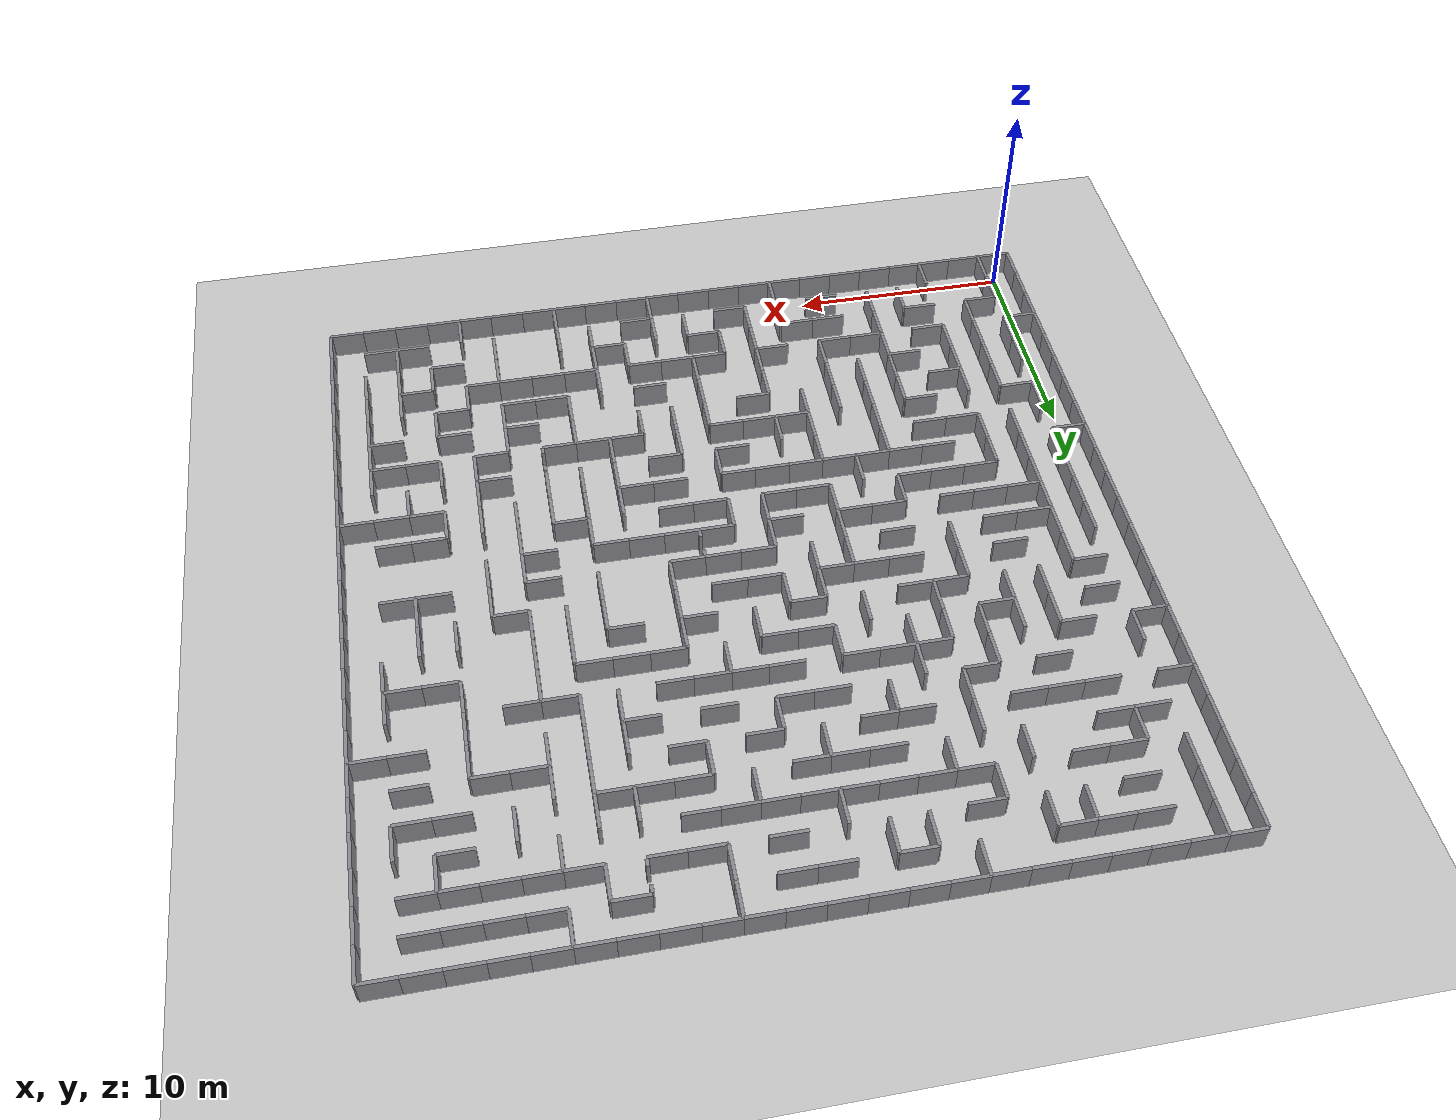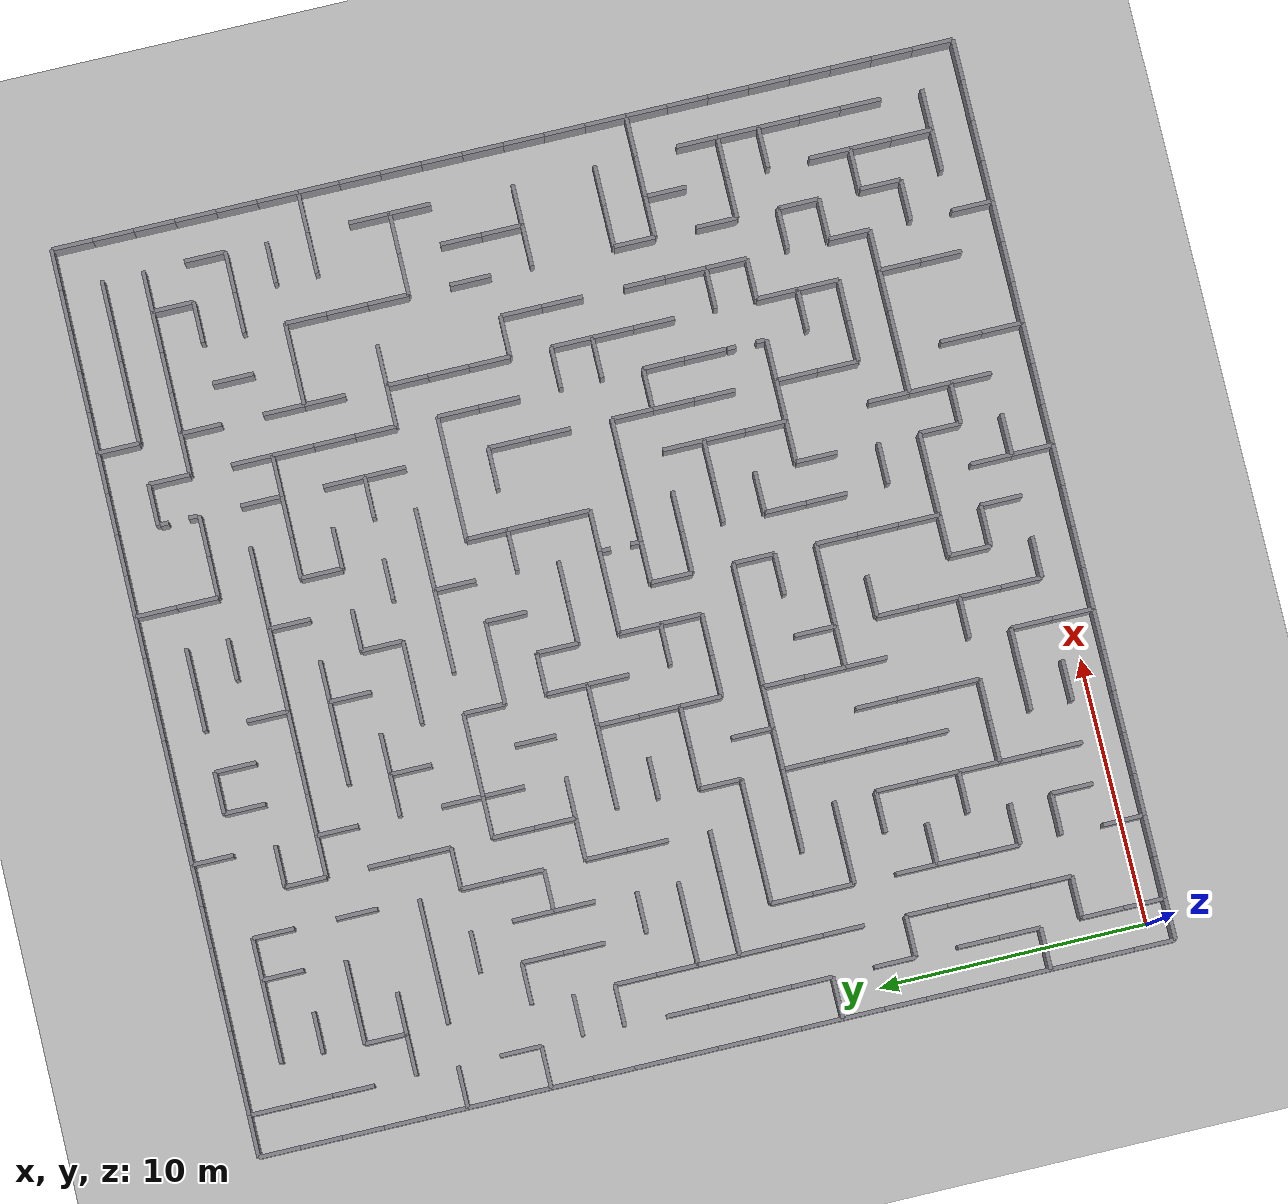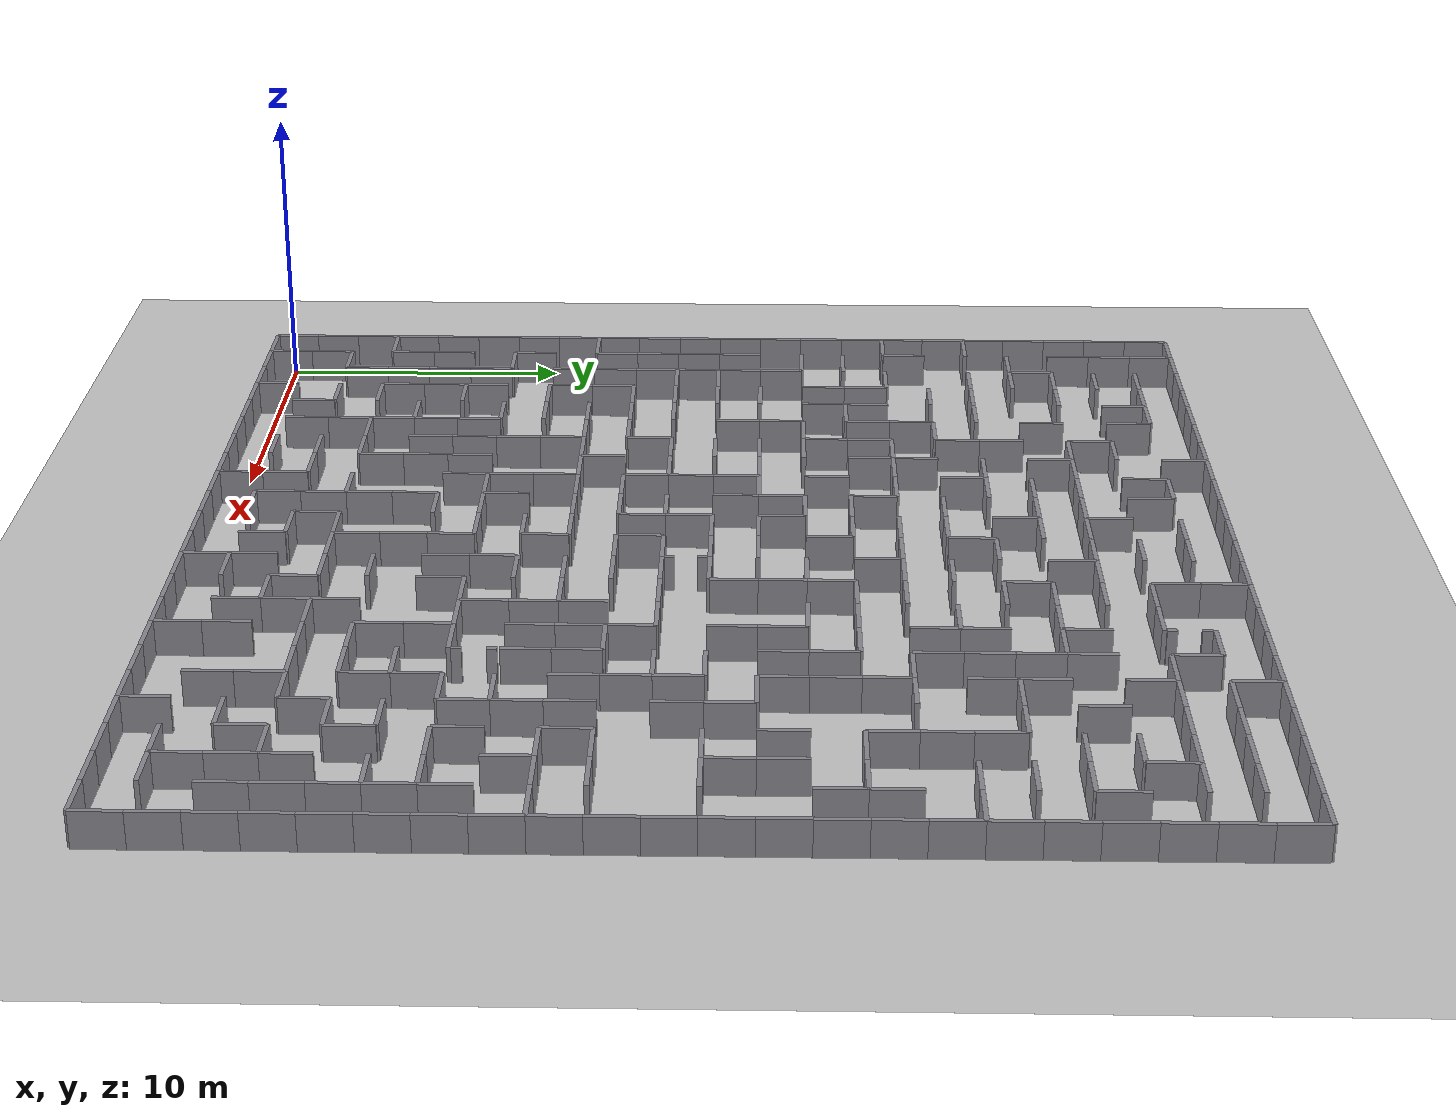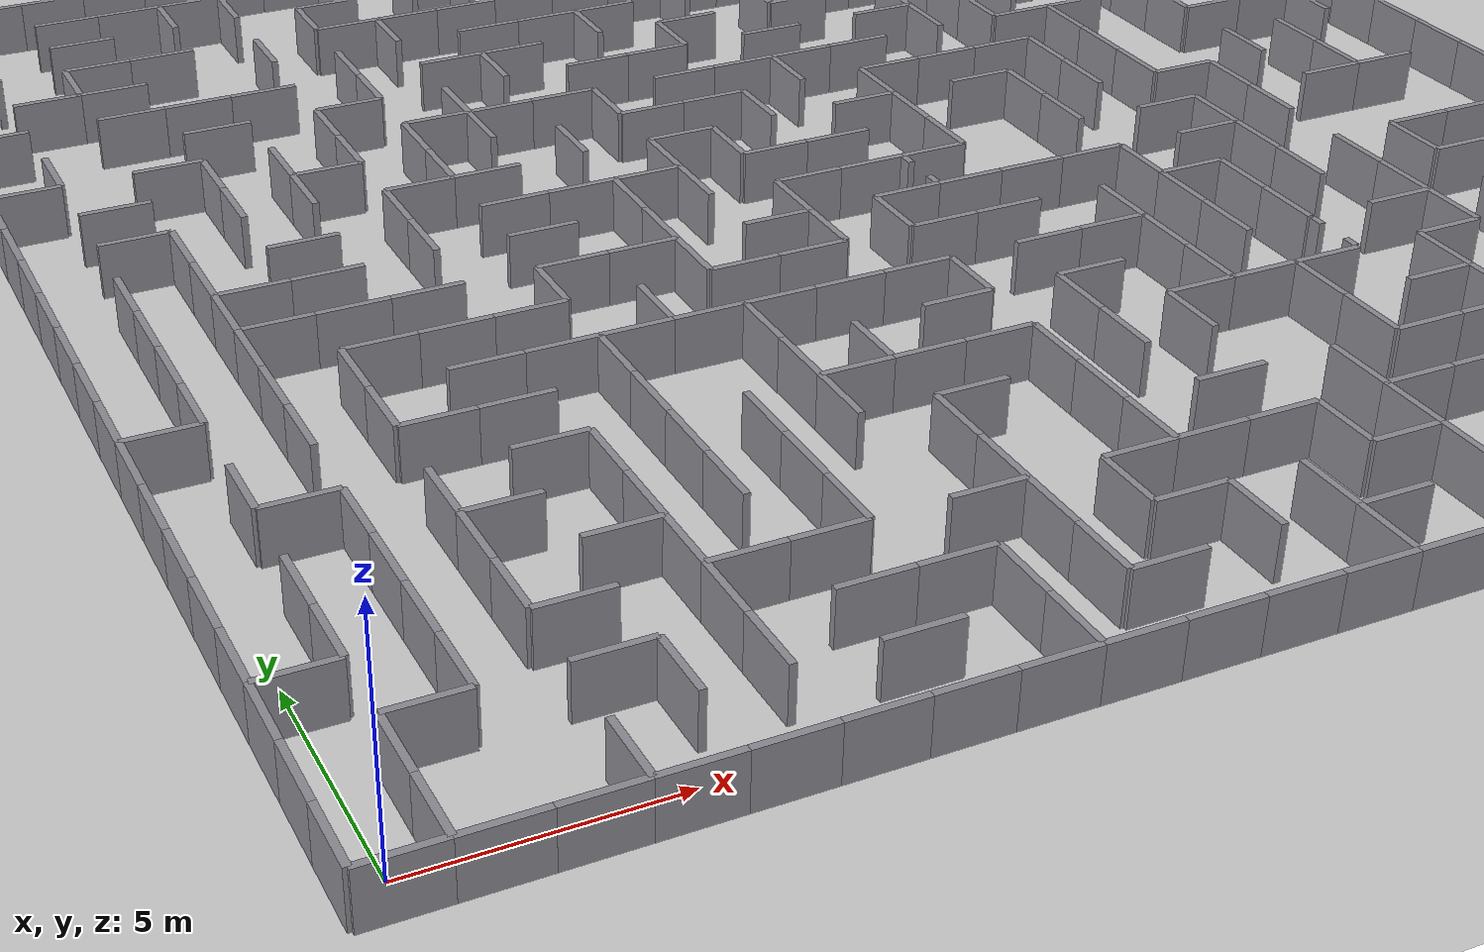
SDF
<sdf version="1.10">
 <world name="sar_maze_generated">
  <physics name="1ms" type="ignored">
   <max_step_size>0.001</max_step_size>
   <real_time_factor>1</real_time_factor>
   <real_time_update_rate>1000</real_time_update_rate>
  </physics>
  <plugin name="gz::sim::systems::Physics" filename="gz-sim-physics-system"/>
  <plugin name="gz::sim::systems::UserCommands" filename="gz-sim-user-commands-system"/>
  <plugin name="gz::sim::systems::SceneBroadcaster" filename="gz-sim-scene-broadcaster-system"/>
  <plugin name="gz::sim::systems::Contact" filename="gz-sim-contact-system"/>
  <plugin filename="gz-sim-imu-system" name="gz::sim::systems::Imu"/>
  <plugin filename="gz-sim-imu-system" name="gz::sim::systems::Imu"/>
  <plugin filename="gz-sim-sensors-system" name="gz::sim::systems::Sensors">
   <render_engine>ogre2</render_engine>
  </plugin>
  <gravity>0 0 -9.8</gravity>
  <magnetic_field>5.5645e-06 2.28758e-05 -4.23884e-05</magnetic_field>
  <atmosphere type="adiabatic"/>
  <scene><ambient>0.4 0.4 0.4 1</ambient><background>0.7 0.7 0.7 1</background><shadows>true</shadows></scene>
  <model name="ground_plane">
   <static>true</static>
   <link name="link">
    <collision name="collision">
     <geometry><plane><normal>0 0 1</normal><size>51.1 51.1</size></plane></geometry>
    </collision>
    <visual name="visual">
     <geometry><plane><normal>0 0 1</normal><size>51.1 51.1</size></plane></geometry>
     <material><ambient>0.8 0.8 0.8 1</ambient><diffuse>0.8 0.8 0.8 1</diffuse></material>
    </visual>
    <pose>16.27 16.27 0 0 0 0</pose>
    <inertial>
     <mass>1</mass>
     <inertia><ixx>1</ixx><ixy>0</ixy><ixz>0</ixz><iyy>1</iyy><iyz>0</iyz><izz>1</izz></inertia>
    </inertial>
   </link>
  </model>
  <light name="sun" type="directional">
   <pose>0 0 20 0 0 0</pose>
   <intensity>1</intensity>
   <direction>-0.5 0.1 -0.9</direction>
   <diffuse>0.8 0.8 0.8 1</diffuse>
   <specular>0.2 0.2 0.2 1</specular>
   <attenuation>
    <range>1000</range>
    <linear>0.01</linear>
    <constant>0.9</constant>
    <quadratic>0.001</quadratic>
   </attenuation>
   <spot><inner_angle>0</inner_angle><outer_angle>0</outer_angle><falloff>0</falloff></spot>
  </light>
  <model name="maze_structure">
   <static>true</static>
   <link name="wall_boundary_h_1">
    <static>true</static>
    <pose>0.0000 -0.7750 0.6000 0 0 0</pose>
    <collision name="wall_boundary_h_1_collision">
     <geometry><box><size>1.5500 0.1500 1.2000</size></box></geometry>
    </collision>
    <visual name="wall_boundary_h_1_visual">
     <geometry><box><size>1.5500 0.1500 1.2000</size></box></geometry>
     <material><ambient>0.55 0.55 0.58 1</ambient><diffuse>0.55 0.55 0.58 1</diffuse></material>
    </visual>
   </link>
   <link name="wall_v_2">
    <static>true</static>
    <pose>0.7750 0.0000 0.6000 0 0 0</pose>
    <collision name="wall_v_2_collision">
     <geometry><box><size>0.1500 1.5500 1.2000</size></box></geometry>
    </collision>
    <visual name="wall_v_2_visual">
     <geometry><box><size>0.1500 1.5500 1.2000</size></box></geometry>
     <material><ambient>0.55 0.55 0.58 1</ambient><diffuse>0.55 0.55 0.58 1</diffuse></material>
    </visual>
   </link>
   <link name="wall_boundary_v_3">
    <static>true</static>
    <pose>-0.7750 0.0000 0.6000 0 0 0</pose>
    <collision name="wall_boundary_v_3_collision">
     <geometry><box><size>0.1500 1.5500 1.2000</size></box></geometry>
    </collision>
    <visual name="wall_boundary_v_3_visual">
     <geometry><box><size>0.1500 1.5500 1.2000</size></box></geometry>
     <material><ambient>0.55 0.55 0.58 1</ambient><diffuse>0.55 0.55 0.58 1</diffuse></material>
    </visual>
   </link>
   <link name="wall_boundary_h_4">
    <static>true</static>
    <pose>1.5500 -0.7750 0.6000 0 0 0</pose>
    <collision name="wall_boundary_h_4_collision">
     <geometry><box><size>1.5500 0.1500 1.2000</size></box></geometry>
    </collision>
    <visual name="wall_boundary_h_4_visual">
     <geometry><box><size>1.5500 0.1500 1.2000</size></box></geometry>
     <material><ambient>0.55 0.55 0.58 1</ambient><diffuse>0.55 0.55 0.58 1</diffuse></material>
    </visual>
   </link>
   <link name="wall_boundary_h_5">
    <static>true</static>
    <pose>3.1000 -0.7750 0.6000 0 0 0</pose>
    <collision name="wall_boundary_h_5_collision">
     <geometry><box><size>1.5500 0.1500 1.2000</size></box></geometry>
    </collision>
    <visual name="wall_boundary_h_5_visual">
     <geometry><box><size>1.5500 0.1500 1.2000</size></box></geometry>
     <material><ambient>0.55 0.55 0.58 1</ambient><diffuse>0.55 0.55 0.58 1</diffuse></material>
    </visual>
   </link>
   <link name="wall_v_6">
    <static>true</static>
    <pose>3.8750 0.0000 0.6000 0 0 0</pose>
    <collision name="wall_v_6_collision">
     <geometry><box><size>0.1500 1.5500 1.2000</size></box></geometry>
    </collision>
    <visual name="wall_v_6_visual">
     <geometry><box><size>0.1500 1.5500 1.2000</size></box></geometry>
     <material><ambient>0.55 0.55 0.58 1</ambient><diffuse>0.55 0.55 0.58 1</diffuse></material>
    </visual>
   </link>
   <link name="wall_boundary_h_7">
    <static>true</static>
    <pose>4.6500 -0.7750 0.6000 0 0 0</pose>
    <collision name="wall_boundary_h_7_collision">
     <geometry><box><size>1.5500 0.1500 1.2000</size></box></geometry>
    </collision>
    <visual name="wall_boundary_h_7_visual">
     <geometry><box><size>1.5500 0.1500 1.2000</size></box></geometry>
     <material><ambient>0.55 0.55 0.58 1</ambient><diffuse>0.55 0.55 0.58 1</diffuse></material>
    </visual>
   </link>
   <link name="wall_boundary_h_8">
    <static>true</static>
    <pose>6.2000 -0.7750 0.6000 0 0 0</pose>
    <collision name="wall_boundary_h_8_collision">
     <geometry><box><size>1.5500 0.1500 1.2000</size></box></geometry>
    </collision>
    <visual name="wall_boundary_h_8_visual">
     <geometry><box><size>1.5500 0.1500 1.2000</size></box></geometry>
     <material><ambient>0.55 0.55 0.58 1</ambient><diffuse>0.55 0.55 0.58 1</diffuse></material>
    </visual>
   </link>
   <link name="wall_boundary_h_9">
    <static>true</static>
    <pose>7.7500 -0.7750 0.6000 0 0 0</pose>
    <collision name="wall_boundary_h_9_collision">
     <geometry><box><size>1.5500 0.1500 1.2000</size></box></geometry>
    </collision>
    <visual name="wall_boundary_h_9_visual">
     <geometry><box><size>1.5500 0.1500 1.2000</size></box></geometry>
     <material><ambient>0.55 0.55 0.58 1</ambient><diffuse>0.55 0.55 0.58 1</diffuse></material>
    </visual>
   </link>
   <link name="wall_h_10">
    <static>true</static>
    <pose>9.3000 0.7750 0.6000 0 0 0</pose>
    <collision name="wall_h_10_collision">
     <geometry><box><size>1.5500 0.1500 1.2000</size></box></geometry>
    </collision>
    <visual name="wall_h_10_visual">
     <geometry><box><size>1.5500 0.1500 1.2000</size></box></geometry>
     <material><ambient>0.55 0.55 0.58 1</ambient><diffuse>0.55 0.55 0.58 1</diffuse></material>
    </visual>
   </link>
   <link name="wall_boundary_h_11">
    <static>true</static>
    <pose>9.3000 -0.7750 0.6000 0 0 0</pose>
    <collision name="wall_boundary_h_11_collision">
     <geometry><box><size>1.5500 0.1500 1.2000</size></box></geometry>
    </collision>
    <visual name="wall_boundary_h_11_visual">
     <geometry><box><size>1.5500 0.1500 1.2000</size></box></geometry>
     <material><ambient>0.55 0.55 0.58 1</ambient><diffuse>0.55 0.55 0.58 1</diffuse></material>
    </visual>
   </link>
   <link name="wall_boundary_h_12">
    <static>true</static>
    <pose>10.8500 -0.7750 0.6000 0 0 0</pose>
    <collision name="wall_boundary_h_12_collision">
     <geometry><box><size>1.5500 0.1500 1.2000</size></box></geometry>
    </collision>
    <visual name="wall_boundary_h_12_visual">
     <geometry><box><size>1.5500 0.1500 1.2000</size></box></geometry>
     <material><ambient>0.55 0.55 0.58 1</ambient><diffuse>0.55 0.55 0.58 1</diffuse></material>
    </visual>
   </link>
   <link name="wall_v_13">
    <static>true</static>
    <pose>11.6250 0.0000 0.6000 0 0 0</pose>
    <collision name="wall_v_13_collision">
     <geometry><box><size>0.1500 1.5500 1.2000</size></box></geometry>
    </collision>
    <visual name="wall_v_13_visual">
     <geometry><box><size>0.1500 1.5500 1.2000</size></box></geometry>
     <material><ambient>0.55 0.55 0.58 1</ambient><diffuse>0.55 0.55 0.58 1</diffuse></material>
    </visual>
   </link>
   <link name="wall_boundary_h_14">
    <static>true</static>
    <pose>12.4000 -0.7750 0.6000 0 0 0</pose>
    <collision name="wall_boundary_h_14_collision">
     <geometry><box><size>1.5500 0.1500 1.2000</size></box></geometry>
    </collision>
    <visual name="wall_boundary_h_14_visual">
     <geometry><box><size>1.5500 0.1500 1.2000</size></box></geometry>
     <material><ambient>0.55 0.55 0.58 1</ambient><diffuse>0.55 0.55 0.58 1</diffuse></material>
    </visual>
   </link>
   <link name="wall_h_15">
    <static>true</static>
    <pose>13.9500 0.7750 0.6000 0 0 0</pose>
    <collision name="wall_h_15_collision">
     <geometry><box><size>1.5500 0.1500 1.2000</size></box></geometry>
    </collision>
    <visual name="wall_h_15_visual">
     <geometry><box><size>1.5500 0.1500 1.2000</size></box></geometry>
     <material><ambient>0.55 0.55 0.58 1</ambient><diffuse>0.55 0.55 0.58 1</diffuse></material>
    </visual>
   </link>
   <link name="wall_boundary_h_16">
    <static>true</static>
    <pose>13.9500 -0.7750 0.6000 0 0 0</pose>
    <collision name="wall_boundary_h_16_collision">
     <geometry><box><size>1.5500 0.1500 1.2000</size></box></geometry>
    </collision>
    <visual name="wall_boundary_h_16_visual">
     <geometry><box><size>1.5500 0.1500 1.2000</size></box></geometry>
     <material><ambient>0.55 0.55 0.58 1</ambient><diffuse>0.55 0.55 0.58 1</diffuse></material>
    </visual>
   </link>
   <link name="wall_boundary_h_17">
    <static>true</static>
    <pose>15.5000 -0.7750 0.6000 0 0 0</pose>
    <collision name="wall_boundary_h_17_collision">
     <geometry><box><size>1.5500 0.1500 1.2000</size></box></geometry>
    </collision>
    <visual name="wall_boundary_h_17_visual">
     <geometry><box><size>1.5500 0.1500 1.2000</size></box></geometry>
     <material><ambient>0.55 0.55 0.58 1</ambient><diffuse>0.55 0.55 0.58 1</diffuse></material>
    </visual>
   </link>
   <link name="wall_boundary_h_18">
    <static>true</static>
    <pose>17.0500 -0.7750 0.6000 0 0 0</pose>
    <collision name="wall_boundary_h_18_collision">
     <geometry><box><size>1.5500 0.1500 1.2000</size></box></geometry>
    </collision>
    <visual name="wall_boundary_h_18_visual">
     <geometry><box><size>1.5500 0.1500 1.2000</size></box></geometry>
     <material><ambient>0.55 0.55 0.58 1</ambient><diffuse>0.55 0.55 0.58 1</diffuse></material>
    </visual>
   </link>
   <link name="wall_v_19">
    <static>true</static>
    <pose>17.8250 0.0000 0.6000 0 0 0</pose>
    <collision name="wall_v_19_collision">
     <geometry><box><size>0.1500 1.5500 1.2000</size></box></geometry>
    </collision>
    <visual name="wall_v_19_visual">
     <geometry><box><size>0.1500 1.5500 1.2000</size></box></geometry>
     <material><ambient>0.55 0.55 0.58 1</ambient><diffuse>0.55 0.55 0.58 1</diffuse></material>
    </visual>
   </link>
   <link name="wall_h_20">
    <static>true</static>
    <pose>18.6000 0.7750 0.6000 0 0 0</pose>
    <collision name="wall_h_20_collision">
     <geometry><box><size>1.5500 0.1500 1.2000</size></box></geometry>
    </collision>
    <visual name="wall_h_20_visual">
     <geometry><box><size>1.5500 0.1500 1.2000</size></box></geometry>
     <material><ambient>0.55 0.55 0.58 1</ambient><diffuse>0.55 0.55 0.58 1</diffuse></material>
    </visual>
   </link>
   <link name="wall_boundary_h_21">
    <static>true</static>
    <pose>18.6000 -0.7750 0.6000 0 0 0</pose>
    <collision name="wall_boundary_h_21_collision">
     <geometry><box><size>1.5500 0.1500 1.2000</size></box></geometry>
    </collision>
    <visual name="wall_boundary_h_21_visual">
     <geometry><box><size>1.5500 0.1500 1.2000</size></box></geometry>
     <material><ambient>0.55 0.55 0.58 1</ambient><diffuse>0.55 0.55 0.58 1</diffuse></material>
    </visual>
   </link>
   <link name="wall_boundary_h_22">
    <static>true</static>
    <pose>20.1500 -0.7750 0.6000 0 0 0</pose>
    <collision name="wall_boundary_h_22_collision">
     <geometry><box><size>1.5500 0.1500 1.2000</size></box></geometry>
    </collision>
    <visual name="wall_boundary_h_22_visual">
     <geometry><box><size>1.5500 0.1500 1.2000</size></box></geometry>
     <material><ambient>0.55 0.55 0.58 1</ambient><diffuse>0.55 0.55 0.58 1</diffuse></material>
    </visual>
   </link>
   <link name="wall_boundary_h_23">
    <static>true</static>
    <pose>21.7000 -0.7750 0.6000 0 0 0</pose>
    <collision name="wall_boundary_h_23_collision">
     <geometry><box><size>1.5500 0.1500 1.2000</size></box></geometry>
    </collision>
    <visual name="wall_boundary_h_23_visual">
     <geometry><box><size>1.5500 0.1500 1.2000</size></box></geometry>
     <material><ambient>0.55 0.55 0.58 1</ambient><diffuse>0.55 0.55 0.58 1</diffuse></material>
    </visual>
   </link>
   <link name="wall_v_24">
    <static>true</static>
    <pose>22.4750 0.0000 0.6000 0 0 0</pose>
    <collision name="wall_v_24_collision">
     <geometry><box><size>0.1500 1.5500 1.2000</size></box></geometry>
    </collision>
    <visual name="wall_v_24_visual">
     <geometry><box><size>0.1500 1.5500 1.2000</size></box></geometry>
     <material><ambient>0.55 0.55 0.58 1</ambient><diffuse>0.55 0.55 0.58 1</diffuse></material>
    </visual>
   </link>
   <link name="wall_boundary_h_25">
    <static>true</static>
    <pose>23.2500 -0.7750 0.6000 0 0 0</pose>
    <collision name="wall_boundary_h_25_collision">
     <geometry><box><size>1.5500 0.1500 1.2000</size></box></geometry>
    </collision>
    <visual name="wall_boundary_h_25_visual">
     <geometry><box><size>1.5500 0.1500 1.2000</size></box></geometry>
     <material><ambient>0.55 0.55 0.58 1</ambient><diffuse>0.55 0.55 0.58 1</diffuse></material>
    </visual>
   </link>
   <link name="wall_boundary_h_26">
    <static>true</static>
    <pose>24.8000 -0.7750 0.6000 0 0 0</pose>
    <collision name="wall_boundary_h_26_collision">
     <geometry><box><size>1.5500 0.1500 1.2000</size></box></geometry>
    </collision>
    <visual name="wall_boundary_h_26_visual">
     <geometry><box><size>1.5500 0.1500 1.2000</size></box></geometry>
     <material><ambient>0.55 0.55 0.58 1</ambient><diffuse>0.55 0.55 0.58 1</diffuse></material>
    </visual>
   </link>
   <link name="wall_boundary_h_27">
    <static>true</static>
    <pose>26.3500 -0.7750 0.6000 0 0 0</pose>
    <collision name="wall_boundary_h_27_collision">
     <geometry><box><size>1.5500 0.1500 1.2000</size></box></geometry>
    </collision>
    <visual name="wall_boundary_h_27_visual">
     <geometry><box><size>1.5500 0.1500 1.2000</size></box></geometry>
     <material><ambient>0.55 0.55 0.58 1</ambient><diffuse>0.55 0.55 0.58 1</diffuse></material>
    </visual>
   </link>
   <link name="wall_v_28">
    <static>true</static>
    <pose>27.1250 0.0000 0.6000 0 0 0</pose>
    <collision name="wall_v_28_collision">
     <geometry><box><size>0.1500 1.5500 1.2000</size></box></geometry>
    </collision>
    <visual name="wall_v_28_visual">
     <geometry><box><size>0.1500 1.5500 1.2000</size></box></geometry>
     <material><ambient>0.55 0.55 0.58 1</ambient><diffuse>0.55 0.55 0.58 1</diffuse></material>
    </visual>
   </link>
   <link name="wall_boundary_h_29">
    <static>true</static>
    <pose>27.9000 -0.7750 0.6000 0 0 0</pose>
    <collision name="wall_boundary_h_29_collision">
     <geometry><box><size>1.5500 0.1500 1.2000</size></box></geometry>
    </collision>
    <visual name="wall_boundary_h_29_visual">
     <geometry><box><size>1.5500 0.1500 1.2000</size></box></geometry>
     <material><ambient>0.55 0.55 0.58 1</ambient><diffuse>0.55 0.55 0.58 1</diffuse></material>
    </visual>
   </link>
   <link name="wall_h_30">
    <static>true</static>
    <pose>29.4500 0.7750 0.6000 0 0 0</pose>
    <collision name="wall_h_30_collision">
     <geometry><box><size>1.5500 0.1500 1.2000</size></box></geometry>
    </collision>
    <visual name="wall_h_30_visual">
     <geometry><box><size>1.5500 0.1500 1.2000</size></box></geometry>
     <material><ambient>0.55 0.55 0.58 1</ambient><diffuse>0.55 0.55 0.58 1</diffuse></material>
    </visual>
   </link>
   <link name="wall_boundary_h_31">
    <static>true</static>
    <pose>29.4500 -0.7750 0.6000 0 0 0</pose>
    <collision name="wall_boundary_h_31_collision">
     <geometry><box><size>1.5500 0.1500 1.2000</size></box></geometry>
    </collision>
    <visual name="wall_boundary_h_31_visual">
     <geometry><box><size>1.5500 0.1500 1.2000</size></box></geometry>
     <material><ambient>0.55 0.55 0.58 1</ambient><diffuse>0.55 0.55 0.58 1</diffuse></material>
    </visual>
   </link>
   <link name="wall_h_32">
    <static>true</static>
    <pose>31.0000 0.7750 0.6000 0 0 0</pose>
    <collision name="wall_h_32_collision">
     <geometry><box><size>1.5500 0.1500 1.2000</size></box></geometry>
    </collision>
    <visual name="wall_h_32_visual">
     <geometry><box><size>1.5500 0.1500 1.2000</size></box></geometry>
     <material><ambient>0.55 0.55 0.58 1</ambient><diffuse>0.55 0.55 0.58 1</diffuse></material>
    </visual>
   </link>
   <link name="wall_boundary_h_33">
    <static>true</static>
    <pose>31.0000 -0.7750 0.6000 0 0 0</pose>
    <collision name="wall_boundary_h_33_collision">
     <geometry><box><size>1.5500 0.1500 1.2000</size></box></geometry>
    </collision>
    <visual name="wall_boundary_h_33_visual">
     <geometry><box><size>1.5500 0.1500 1.2000</size></box></geometry>
     <material><ambient>0.55 0.55 0.58 1</ambient><diffuse>0.55 0.55 0.58 1</diffuse></material>
    </visual>
   </link>
   <link name="wall_boundary_h_34">
    <static>true</static>
    <pose>32.5500 -0.7750 0.6000 0 0 0</pose>
    <collision name="wall_boundary_h_34_collision">
     <geometry><box><size>1.5500 0.1500 1.2000</size></box></geometry>
    </collision>
    <visual name="wall_boundary_h_34_visual">
     <geometry><box><size>1.5500 0.1500 1.2000</size></box></geometry>
     <material><ambient>0.55 0.55 0.58 1</ambient><diffuse>0.55 0.55 0.58 1</diffuse></material>
    </visual>
   </link>
   <link name="wall_boundary_v_35">
    <static>true</static>
    <pose>33.3250 0.0000 0.6000 0 0 0</pose>
    <collision name="wall_boundary_v_35_collision">
     <geometry><box><size>0.1500 1.5500 1.2000</size></box></geometry>
    </collision>
    <visual name="wall_boundary_v_35_visual">
     <geometry><box><size>0.1500 1.5500 1.2000</size></box></geometry>
     <material><ambient>0.55 0.55 0.58 1</ambient><diffuse>0.55 0.55 0.58 1</diffuse></material>
    </visual>
   </link>
   <link name="wall_v_36">
    <static>true</static>
    <pose>0.7750 1.5500 0.6000 0 0 0</pose>
    <collision name="wall_v_36_collision">
     <geometry><box><size>0.1500 1.5500 1.2000</size></box></geometry>
    </collision>
    <visual name="wall_v_36_visual">
     <geometry><box><size>0.1500 1.5500 1.2000</size></box></geometry>
     <material><ambient>0.55 0.55 0.58 1</ambient><diffuse>0.55 0.55 0.58 1</diffuse></material>
    </visual>
   </link>
   <link name="wall_boundary_v_37">
    <static>true</static>
    <pose>-0.7750 1.5500 0.6000 0 0 0</pose>
    <collision name="wall_boundary_v_37_collision">
     <geometry><box><size>0.1500 1.5500 1.2000</size></box></geometry>
    </collision>
    <visual name="wall_boundary_v_37_visual">
     <geometry><box><size>0.1500 1.5500 1.2000</size></box></geometry>
     <material><ambient>0.55 0.55 0.58 1</ambient><diffuse>0.55 0.55 0.58 1</diffuse></material>
    </visual>
   </link>
   <link name="wall_h_38">
    <static>true</static>
    <pose>1.5500 2.3250 0.6000 0 0 0</pose>
    <collision name="wall_h_38_collision">
     <geometry><box><size>1.5500 0.1500 1.2000</size></box></geometry>
    </collision>
    <visual name="wall_h_38_visual">
     <geometry><box><size>1.5500 0.1500 1.2000</size></box></geometry>
     <material><ambient>0.55 0.55 0.58 1</ambient><diffuse>0.55 0.55 0.58 1</diffuse></material>
    </visual>
   </link>
   <link name="wall_h_39">
    <static>true</static>
    <pose>4.6500 2.3250 0.6000 0 0 0</pose>
    <collision name="wall_h_39_collision">
     <geometry><box><size>1.5500 0.1500 1.2000</size></box></geometry>
    </collision>
    <visual name="wall_h_39_visual">
     <geometry><box><size>1.5500 0.1500 1.2000</size></box></geometry>
     <material><ambient>0.55 0.55 0.58 1</ambient><diffuse>0.55 0.55 0.58 1</diffuse></material>
    </visual>
   </link>
   <link name="wall_v_40">
    <static>true</static>
    <pose>5.4250 1.5500 0.6000 0 0 0</pose>
    <collision name="wall_v_40_collision">
     <geometry><box><size>0.1500 1.5500 1.2000</size></box></geometry>
    </collision>
    <visual name="wall_v_40_visual">
     <geometry><box><size>0.1500 1.5500 1.2000</size></box></geometry>
     <material><ambient>0.55 0.55 0.58 1</ambient><diffuse>0.55 0.55 0.58 1</diffuse></material>
    </visual>
   </link>
   <link name="wall_v_41">
    <static>true</static>
    <pose>6.9750 1.5500 0.6000 0 0 0</pose>
    <collision name="wall_v_41_collision">
     <geometry><box><size>0.1500 1.5500 1.2000</size></box></geometry>
    </collision>
    <visual name="wall_v_41_visual">
     <geometry><box><size>0.1500 1.5500 1.2000</size></box></geometry>
     <material><ambient>0.55 0.55 0.58 1</ambient><diffuse>0.55 0.55 0.58 1</diffuse></material>
    </visual>
   </link>
   <link name="wall_h_42">
    <static>true</static>
    <pose>9.3000 2.3250 0.6000 0 0 0</pose>
    <collision name="wall_h_42_collision">
     <geometry><box><size>1.5500 0.1500 1.2000</size></box></geometry>
    </collision>
    <visual name="wall_h_42_visual">
     <geometry><box><size>1.5500 0.1500 1.2000</size></box></geometry>
     <material><ambient>0.55 0.55 0.58 1</ambient><diffuse>0.55 0.55 0.58 1</diffuse></material>
    </visual>
   </link>
   <link name="wall_h_43">
    <static>true</static>
    <pose>10.8500 2.3250 0.6000 0 0 0</pose>
    <collision name="wall_h_43_collision">
     <geometry><box><size>1.5500 0.1500 1.2000</size></box></geometry>
    </collision>
    <visual name="wall_h_43_visual">
     <geometry><box><size>1.5500 0.1500 1.2000</size></box></geometry>
     <material><ambient>0.55 0.55 0.58 1</ambient><diffuse>0.55 0.55 0.58 1</diffuse></material>
    </visual>
   </link>
   <link name="wall_v_44">
    <static>true</static>
    <pose>11.6250 1.5500 0.6000 0 0 0</pose>
    <collision name="wall_v_44_collision">
     <geometry><box><size>0.1500 1.5500 1.2000</size></box></geometry>
    </collision>
    <visual name="wall_v_44_visual">
     <geometry><box><size>0.1500 1.5500 1.2000</size></box></geometry>
     <material><ambient>0.55 0.55 0.58 1</ambient><diffuse>0.55 0.55 0.58 1</diffuse></material>
    </visual>
   </link>
   <link name="wall_v_45">
    <static>true</static>
    <pose>13.1750 1.5500 0.6000 0 0 0</pose>
    <collision name="wall_v_45_collision">
     <geometry><box><size>0.1500 1.5500 1.2000</size></box></geometry>
    </collision>
    <visual name="wall_v_45_visual">
     <geometry><box><size>0.1500 1.5500 1.2000</size></box></geometry>
     <material><ambient>0.55 0.55 0.58 1</ambient><diffuse>0.55 0.55 0.58 1</diffuse></material>
    </visual>
   </link>
   <link name="wall_h_46">
    <static>true</static>
    <pose>15.5000 2.3250 0.6000 0 0 0</pose>
    <collision name="wall_h_46_collision">
     <geometry><box><size>1.5500 0.1500 1.2000</size></box></geometry>
    </collision>
    <visual name="wall_h_46_visual">
     <geometry><box><size>1.5500 0.1500 1.2000</size></box></geometry>
     <material><ambient>0.55 0.55 0.58 1</ambient><diffuse>0.55 0.55 0.58 1</diffuse></material>
    </visual>
   </link>
   <link name="wall_v_47">
    <static>true</static>
    <pose>16.2750 1.5500 0.6000 0 0 0</pose>
    <collision name="wall_v_47_collision">
     <geometry><box><size>0.1500 1.5500 1.2000</size></box></geometry>
    </collision>
    <visual name="wall_v_47_visual">
     <geometry><box><size>0.1500 1.5500 1.2000</size></box></geometry>
     <material><ambient>0.55 0.55 0.58 1</ambient><diffuse>0.55 0.55 0.58 1</diffuse></material>
    </visual>
   </link>
   <link name="wall_v_48">
    <static>true</static>
    <pose>17.8250 1.5500 0.6000 0 0 0</pose>
    <collision name="wall_v_48_collision">
     <geometry><box><size>0.1500 1.5500 1.2000</size></box></geometry>
    </collision>
    <visual name="wall_v_48_visual">
     <geometry><box><size>0.1500 1.5500 1.2000</size></box></geometry>
     <material><ambient>0.55 0.55 0.58 1</ambient><diffuse>0.55 0.55 0.58 1</diffuse></material>
    </visual>
   </link>
   <link name="wall_h_49">
    <static>true</static>
    <pose>20.1500 2.3250 0.6000 0 0 0</pose>
    <collision name="wall_h_49_collision">
     <geometry><box><size>1.5500 0.1500 1.2000</size></box></geometry>
    </collision>
    <visual name="wall_h_49_visual">
     <geometry><box><size>1.5500 0.1500 1.2000</size></box></geometry>
     <material><ambient>0.55 0.55 0.58 1</ambient><diffuse>0.55 0.55 0.58 1</diffuse></material>
    </visual>
   </link>
   <link name="wall_v_50">
    <static>true</static>
    <pose>20.9250 1.5500 0.6000 0 0 0</pose>
    <collision name="wall_v_50_collision">
     <geometry><box><size>0.1500 1.5500 1.2000</size></box></geometry>
    </collision>
    <visual name="wall_v_50_visual">
     <geometry><box><size>0.1500 1.5500 1.2000</size></box></geometry>
     <material><ambient>0.55 0.55 0.58 1</ambient><diffuse>0.55 0.55 0.58 1</diffuse></material>
    </visual>
   </link>
   <link name="wall_v_51">
    <static>true</static>
    <pose>22.4750 1.5500 0.6000 0 0 0</pose>
    <collision name="wall_v_51_collision">
     <geometry><box><size>0.1500 1.5500 1.2000</size></box></geometry>
    </collision>
    <visual name="wall_v_51_visual">
     <geometry><box><size>0.1500 1.5500 1.2000</size></box></geometry>
     <material><ambient>0.55 0.55 0.58 1</ambient><diffuse>0.55 0.55 0.58 1</diffuse></material>
    </visual>
   </link>
   <link name="wall_v_52">
    <static>true</static>
    <pose>25.5750 1.5500 0.6000 0 0 0</pose>
    <collision name="wall_v_52_collision">
     <geometry><box><size>0.1500 1.5500 1.2000</size></box></geometry>
    </collision>
    <visual name="wall_v_52_visual">
     <geometry><box><size>0.1500 1.5500 1.2000</size></box></geometry>
     <material><ambient>0.55 0.55 0.58 1</ambient><diffuse>0.55 0.55 0.58 1</diffuse></material>
    </visual>
   </link>
   <link name="wall_h_53">
    <static>true</static>
    <pose>27.9000 2.3250 0.6000 0 0 0</pose>
    <collision name="wall_h_53_collision">
     <geometry><box><size>1.5500 0.1500 1.2000</size></box></geometry>
    </collision>
    <visual name="wall_h_53_visual">
     <geometry><box><size>1.5500 0.1500 1.2000</size></box></geometry>
     <material><ambient>0.55 0.55 0.58 1</ambient><diffuse>0.55 0.55 0.58 1</diffuse></material>
    </visual>
   </link>
   <link name="wall_v_54">
    <static>true</static>
    <pose>30.2250 1.5500 0.6000 0 0 0</pose>
    <collision name="wall_v_54_collision">
     <geometry><box><size>0.1500 1.5500 1.2000</size></box></geometry>
    </collision>
    <visual name="wall_v_54_visual">
     <geometry><box><size>0.1500 1.5500 1.2000</size></box></geometry>
     <material><ambient>0.55 0.55 0.58 1</ambient><diffuse>0.55 0.55 0.58 1</diffuse></material>
    </visual>
   </link>
   <link name="wall_boundary_v_55">
    <static>true</static>
    <pose>33.3250 1.5500 0.6000 0 0 0</pose>
    <collision name="wall_boundary_v_55_collision">
     <geometry><box><size>0.1500 1.5500 1.2000</size></box></geometry>
    </collision>
    <visual name="wall_boundary_v_55_visual">
     <geometry><box><size>0.1500 1.5500 1.2000</size></box></geometry>
     <material><ambient>0.55 0.55 0.58 1</ambient><diffuse>0.55 0.55 0.58 1</diffuse></material>
    </visual>
   </link>
   <link name="wall_h_56">
    <static>true</static>
    <pose>0.0000 3.8750 0.6000 0 0 0</pose>
    <collision name="wall_h_56_collision">
     <geometry><box><size>1.5500 0.1500 1.2000</size></box></geometry>
    </collision>
    <visual name="wall_h_56_visual">
     <geometry><box><size>1.5500 0.1500 1.2000</size></box></geometry>
     <material><ambient>0.55 0.55 0.58 1</ambient><diffuse>0.55 0.55 0.58 1</diffuse></material>
    </visual>
   </link>
   <link name="wall_boundary_v_57">
    <static>true</static>
    <pose>-0.7750 3.1000 0.6000 0 0 0</pose>
    <collision name="wall_boundary_v_57_collision">
     <geometry><box><size>0.1500 1.5500 1.2000</size></box></geometry>
    </collision>
    <visual name="wall_boundary_v_57_visual">
     <geometry><box><size>0.1500 1.5500 1.2000</size></box></geometry>
     <material><ambient>0.55 0.55 0.58 1</ambient><diffuse>0.55 0.55 0.58 1</diffuse></material>
    </visual>
   </link>
   <link name="wall_v_58">
    <static>true</static>
    <pose>2.3250 3.1000 0.6000 0 0 0</pose>
    <collision name="wall_v_58_collision">
     <geometry><box><size>0.1500 1.5500 1.2000</size></box></geometry>
    </collision>
    <visual name="wall_v_58_visual">
     <geometry><box><size>0.1500 1.5500 1.2000</size></box></geometry>
     <material><ambient>0.55 0.55 0.58 1</ambient><diffuse>0.55 0.55 0.58 1</diffuse></material>
    </visual>
   </link>
   <link name="wall_h_59">
    <static>true</static>
    <pose>4.6500 3.8750 0.6000 0 0 0</pose>
    <collision name="wall_h_59_collision">
     <geometry><box><size>1.5500 0.1500 1.2000</size></box></geometry>
    </collision>
    <visual name="wall_h_59_visual">
     <geometry><box><size>1.5500 0.1500 1.2000</size></box></geometry>
     <material><ambient>0.55 0.55 0.58 1</ambient><diffuse>0.55 0.55 0.58 1</diffuse></material>
    </visual>
   </link>
   <link name="wall_v_60">
    <static>true</static>
    <pose>6.9750 3.1000 0.6000 0 0 0</pose>
    <collision name="wall_v_60_collision">
     <geometry><box><size>0.1500 1.5500 1.2000</size></box></geometry>
    </collision>
    <visual name="wall_v_60_visual">
     <geometry><box><size>0.1500 1.5500 1.2000</size></box></geometry>
     <material><ambient>0.55 0.55 0.58 1</ambient><diffuse>0.55 0.55 0.58 1</diffuse></material>
    </visual>
   </link>
   <link name="wall_h_61">
    <static>true</static>
    <pose>7.7500 3.8750 0.6000 0 0 0</pose>
    <collision name="wall_h_61_collision">
     <geometry><box><size>1.5500 0.1500 1.2000</size></box></geometry>
    </collision>
    <visual name="wall_h_61_visual">
     <geometry><box><size>1.5500 0.1500 1.2000</size></box></geometry>
     <material><ambient>0.55 0.55 0.58 1</ambient><diffuse>0.55 0.55 0.58 1</diffuse></material>
    </visual>
   </link>
   <link name="wall_h_62">
    <static>true</static>
    <pose>9.3000 3.8750 0.6000 0 0 0</pose>
    <collision name="wall_h_62_collision">
     <geometry><box><size>1.5500 0.1500 1.2000</size></box></geometry>
    </collision>
    <visual name="wall_h_62_visual">
     <geometry><box><size>1.5500 0.1500 1.2000</size></box></geometry>
     <material><ambient>0.55 0.55 0.58 1</ambient><diffuse>0.55 0.55 0.58 1</diffuse></material>
    </visual>
   </link>
   <link name="wall_h_63">
    <static>true</static>
    <pose>12.4000 3.8750 0.6000 0 0 0</pose>
    <collision name="wall_h_63_collision">
     <geometry><box><size>1.5500 0.1500 1.2000</size></box></geometry>
    </collision>
    <visual name="wall_h_63_visual">
     <geometry><box><size>1.5500 0.1500 1.2000</size></box></geometry>
     <material><ambient>0.55 0.55 0.58 1</ambient><diffuse>0.55 0.55 0.58 1</diffuse></material>
    </visual>
   </link>
   <link name="wall_v_64">
    <static>true</static>
    <pose>13.1750 3.1000 0.6000 0 0 0</pose>
    <collision name="wall_v_64_collision">
     <geometry><box><size>0.1500 1.5500 1.2000</size></box></geometry>
    </collision>
    <visual name="wall_v_64_visual">
     <geometry><box><size>0.1500 1.5500 1.2000</size></box></geometry>
     <material><ambient>0.55 0.55 0.58 1</ambient><diffuse>0.55 0.55 0.58 1</diffuse></material>
    </visual>
   </link>
   <link name="wall_v_65">
    <static>true</static>
    <pose>14.7250 3.1000 0.6000 0 0 0</pose>
    <collision name="wall_v_65_collision">
     <geometry><box><size>0.1500 1.5500 1.2000</size></box></geometry>
    </collision>
    <visual name="wall_v_65_visual">
     <geometry><box><size>0.1500 1.5500 1.2000</size></box></geometry>
     <material><ambient>0.55 0.55 0.58 1</ambient><diffuse>0.55 0.55 0.58 1</diffuse></material>
    </visual>
   </link>
   <link name="wall_h_66">
    <static>true</static>
    <pose>15.5000 3.8750 0.6000 0 0 0</pose>
    <collision name="wall_h_66_collision">
     <geometry><box><size>1.5500 0.1500 1.2000</size></box></geometry>
    </collision>
    <visual name="wall_h_66_visual">
     <geometry><box><size>1.5500 0.1500 1.2000</size></box></geometry>
     <material><ambient>0.55 0.55 0.58 1</ambient><diffuse>0.55 0.55 0.58 1</diffuse></material>
    </visual>
   </link>
   <link name="wall_h_67">
    <static>true</static>
    <pose>17.0500 3.8750 0.6000 0 0 0</pose>
    <collision name="wall_h_67_collision">
     <geometry><box><size>1.5500 0.1500 1.2000</size></box></geometry>
    </collision>
    <visual name="wall_h_67_visual">
     <geometry><box><size>1.5500 0.1500 1.2000</size></box></geometry>
     <material><ambient>0.55 0.55 0.58 1</ambient><diffuse>0.55 0.55 0.58 1</diffuse></material>
    </visual>
   </link>
   <link name="wall_h_68">
    <static>true</static>
    <pose>18.6000 3.8750 0.6000 0 0 0</pose>
    <collision name="wall_h_68_collision">
     <geometry><box><size>1.5500 0.1500 1.2000</size></box></geometry>
    </collision>
    <visual name="wall_h_68_visual">
     <geometry><box><size>1.5500 0.1500 1.2000</size></box></geometry>
     <material><ambient>0.55 0.55 0.58 1</ambient><diffuse>0.55 0.55 0.58 1</diffuse></material>
    </visual>
   </link>
   <link name="wall_v_69">
    <static>true</static>
    <pose>19.3750 3.1000 0.6000 0 0 0</pose>
    <collision name="wall_v_69_collision">
     <geometry><box><size>0.1500 1.5500 1.2000</size></box></geometry>
    </collision>
    <visual name="wall_v_69_visual">
     <geometry><box><size>0.1500 1.5500 1.2000</size></box></geometry>
     <material><ambient>0.55 0.55 0.58 1</ambient><diffuse>0.55 0.55 0.58 1</diffuse></material>
    </visual>
   </link>
   <link name="wall_v_70">
    <static>true</static>
    <pose>20.9250 3.1000 0.6000 0 0 0</pose>
    <collision name="wall_v_70_collision">
     <geometry><box><size>0.1500 1.5500 1.2000</size></box></geometry>
    </collision>
    <visual name="wall_v_70_visual">
     <geometry><box><size>0.1500 1.5500 1.2000</size></box></geometry>
     <material><ambient>0.55 0.55 0.58 1</ambient><diffuse>0.55 0.55 0.58 1</diffuse></material>
    </visual>
   </link>
   <link name="wall_h_71">
    <static>true</static>
    <pose>21.7000 3.8750 0.6000 0 0 0</pose>
    <collision name="wall_h_71_collision">
     <geometry><box><size>1.5500 0.1500 1.2000</size></box></geometry>
    </collision>
    <visual name="wall_h_71_visual">
     <geometry><box><size>1.5500 0.1500 1.2000</size></box></geometry>
     <material><ambient>0.55 0.55 0.58 1</ambient><diffuse>0.55 0.55 0.58 1</diffuse></material>
    </visual>
   </link>
   <link name="wall_h_72">
    <static>true</static>
    <pose>23.2500 3.8750 0.6000 0 0 0</pose>
    <collision name="wall_h_72_collision">
     <geometry><box><size>1.5500 0.1500 1.2000</size></box></geometry>
    </collision>
    <visual name="wall_h_72_visual">
     <geometry><box><size>1.5500 0.1500 1.2000</size></box></geometry>
     <material><ambient>0.55 0.55 0.58 1</ambient><diffuse>0.55 0.55 0.58 1</diffuse></material>
    </visual>
   </link>
   <link name="wall_h_73">
    <static>true</static>
    <pose>24.8000 3.8750 0.6000 0 0 0</pose>
    <collision name="wall_h_73_collision">
     <geometry><box><size>1.5500 0.1500 1.2000</size></box></geometry>
    </collision>
    <visual name="wall_h_73_visual">
     <geometry><box><size>1.5500 0.1500 1.2000</size></box></geometry>
     <material><ambient>0.55 0.55 0.58 1</ambient><diffuse>0.55 0.55 0.58 1</diffuse></material>
    </visual>
   </link>
   <link name="wall_v_74">
    <static>true</static>
    <pose>25.5750 3.1000 0.6000 0 0 0</pose>
    <collision name="wall_v_74_collision">
     <geometry><box><size>0.1500 1.5500 1.2000</size></box></geometry>
    </collision>
    <visual name="wall_v_74_visual">
     <geometry><box><size>0.1500 1.5500 1.2000</size></box></geometry>
     <material><ambient>0.55 0.55 0.58 1</ambient><diffuse>0.55 0.55 0.58 1</diffuse></material>
    </visual>
   </link>
   <link name="wall_h_75">
    <static>true</static>
    <pose>26.3500 3.8750 0.6000 0 0 0</pose>
    <collision name="wall_h_75_collision">
     <geometry><box><size>1.5500 0.1500 1.2000</size></box></geometry>
    </collision>
    <visual name="wall_h_75_visual">
     <geometry><box><size>1.5500 0.1500 1.2000</size></box></geometry>
     <material><ambient>0.55 0.55 0.58 1</ambient><diffuse>0.55 0.55 0.58 1</diffuse></material>
    </visual>
   </link>
   <link name="wall_v_76">
    <static>true</static>
    <pose>28.6750 3.1000 0.6000 0 0 0</pose>
    <collision name="wall_v_76_collision">
     <geometry><box><size>0.1500 1.5500 1.2000</size></box></geometry>
    </collision>
    <visual name="wall_v_76_visual">
     <geometry><box><size>0.1500 1.5500 1.2000</size></box></geometry>
     <material><ambient>0.55 0.55 0.58 1</ambient><diffuse>0.55 0.55 0.58 1</diffuse></material>
    </visual>
   </link>
   <link name="wall_h_77">
    <static>true</static>
    <pose>29.4500 3.8750 0.6000 0 0 0</pose>
    <collision name="wall_h_77_collision">
     <geometry><box><size>1.5500 0.1500 1.2000</size></box></geometry>
    </collision>
    <visual name="wall_h_77_visual">
     <geometry><box><size>1.5500 0.1500 1.2000</size></box></geometry>
     <material><ambient>0.55 0.55 0.58 1</ambient><diffuse>0.55 0.55 0.58 1</diffuse></material>
    </visual>
   </link>
   <link name="wall_v_78">
    <static>true</static>
    <pose>30.2250 3.1000 0.6000 0 0 0</pose>
    <collision name="wall_v_78_collision">
     <geometry><box><size>0.1500 1.5500 1.2000</size></box></geometry>
    </collision>
    <visual name="wall_v_78_visual">
     <geometry><box><size>0.1500 1.5500 1.2000</size></box></geometry>
     <material><ambient>0.55 0.55 0.58 1</ambient><diffuse>0.55 0.55 0.58 1</diffuse></material>
    </visual>
   </link>
   <link name="wall_v_79">
    <static>true</static>
    <pose>31.7750 3.1000 0.6000 0 0 0</pose>
    <collision name="wall_v_79_collision">
     <geometry><box><size>0.1500 1.5500 1.2000</size></box></geometry>
    </collision>
    <visual name="wall_v_79_visual">
     <geometry><box><size>0.1500 1.5500 1.2000</size></box></geometry>
     <material><ambient>0.55 0.55 0.58 1</ambient><diffuse>0.55 0.55 0.58 1</diffuse></material>
    </visual>
   </link>
   <link name="wall_boundary_v_80">
    <static>true</static>
    <pose>33.3250 3.1000 0.6000 0 0 0</pose>
    <collision name="wall_boundary_v_80_collision">
     <geometry><box><size>0.1500 1.5500 1.2000</size></box></geometry>
    </collision>
    <visual name="wall_boundary_v_80_visual">
     <geometry><box><size>0.1500 1.5500 1.2000</size></box></geometry>
     <material><ambient>0.55 0.55 0.58 1</ambient><diffuse>0.55 0.55 0.58 1</diffuse></material>
    </visual>
   </link>
   <link name="wall_v_81">
    <static>true</static>
    <pose>0.7750 4.6500 0.6000 0 0 0</pose>
    <collision name="wall_v_81_collision">
     <geometry><box><size>0.1500 1.5500 1.2000</size></box></geometry>
    </collision>
    <visual name="wall_v_81_visual">
     <geometry><box><size>0.1500 1.5500 1.2000</size></box></geometry>
     <material><ambient>0.55 0.55 0.58 1</ambient><diffuse>0.55 0.55 0.58 1</diffuse></material>
    </visual>
   </link>
   <link name="wall_boundary_v_82">
    <static>true</static>
    <pose>-0.7750 4.6500 0.6000 0 0 0</pose>
    <collision name="wall_boundary_v_82_collision">
     <geometry><box><size>0.1500 1.5500 1.2000</size></box></geometry>
    </collision>
    <visual name="wall_boundary_v_82_visual">
     <geometry><box><size>0.1500 1.5500 1.2000</size></box></geometry>
     <material><ambient>0.55 0.55 0.58 1</ambient><diffuse>0.55 0.55 0.58 1</diffuse></material>
    </visual>
   </link>
   <link name="wall_v_83">
    <static>true</static>
    <pose>2.3250 4.6500 0.6000 0 0 0</pose>
    <collision name="wall_v_83_collision">
     <geometry><box><size>0.1500 1.5500 1.2000</size></box></geometry>
    </collision>
    <visual name="wall_v_83_visual">
     <geometry><box><size>0.1500 1.5500 1.2000</size></box></geometry>
     <material><ambient>0.55 0.55 0.58 1</ambient><diffuse>0.55 0.55 0.58 1</diffuse></material>
    </visual>
   </link>
   <link name="wall_v_84">
    <static>true</static>
    <pose>3.8750 4.6500 0.6000 0 0 0</pose>
    <collision name="wall_v_84_collision">
     <geometry><box><size>0.1500 1.5500 1.2000</size></box></geometry>
    </collision>
    <visual name="wall_v_84_visual">
     <geometry><box><size>0.1500 1.5500 1.2000</size></box></geometry>
     <material><ambient>0.55 0.55 0.58 1</ambient><diffuse>0.55 0.55 0.58 1</diffuse></material>
    </visual>
   </link>
   <link name="wall_h_85">
    <static>true</static>
    <pose>6.2000 5.4250 0.6000 0 0 0</pose>
    <collision name="wall_h_85_collision">
     <geometry><box><size>1.5500 0.1500 1.2000</size></box></geometry>
    </collision>
    <visual name="wall_h_85_visual">
     <geometry><box><size>1.5500 0.1500 1.2000</size></box></geometry>
     <material><ambient>0.55 0.55 0.58 1</ambient><diffuse>0.55 0.55 0.58 1</diffuse></material>
    </visual>
   </link>
   <link name="wall_v_86">
    <static>true</static>
    <pose>6.9750 4.6500 0.6000 0 0 0</pose>
    <collision name="wall_v_86_collision">
     <geometry><box><size>0.1500 1.5500 1.2000</size></box></geometry>
    </collision>
    <visual name="wall_v_86_visual">
     <geometry><box><size>0.1500 1.5500 1.2000</size></box></geometry>
     <material><ambient>0.55 0.55 0.58 1</ambient><diffuse>0.55 0.55 0.58 1</diffuse></material>
    </visual>
   </link>
   <link name="wall_v_87">
    <static>true</static>
    <pose>10.0750 4.6500 0.6000 0 0 0</pose>
    <collision name="wall_v_87_collision">
     <geometry><box><size>0.1500 1.5500 1.2000</size></box></geometry>
    </collision>
    <visual name="wall_v_87_visual">
     <geometry><box><size>0.1500 1.5500 1.2000</size></box></geometry>
     <material><ambient>0.55 0.55 0.58 1</ambient><diffuse>0.55 0.55 0.58 1</diffuse></material>
    </visual>
   </link>
   <link name="wall_v_88">
    <static>true</static>
    <pose>13.1750 4.6500 0.6000 0 0 0</pose>
    <collision name="wall_v_88_collision">
     <geometry><box><size>0.1500 1.5500 1.2000</size></box></geometry>
    </collision>
    <visual name="wall_v_88_visual">
     <geometry><box><size>0.1500 1.5500 1.2000</size></box></geometry>
     <material><ambient>0.55 0.55 0.58 1</ambient><diffuse>0.55 0.55 0.58 1</diffuse></material>
    </visual>
   </link>
   <link name="wall_v_89">
    <static>true</static>
    <pose>16.2750 4.6500 0.6000 0 0 0</pose>
    <collision name="wall_v_89_collision">
     <geometry><box><size>0.1500 1.5500 1.2000</size></box></geometry>
    </collision>
    <visual name="wall_v_89_visual">
     <geometry><box><size>0.1500 1.5500 1.2000</size></box></geometry>
     <material><ambient>0.55 0.55 0.58 1</ambient><diffuse>0.55 0.55 0.58 1</diffuse></material>
    </visual>
   </link>
   <link name="wall_h_90">
    <static>true</static>
    <pose>18.6000 5.4250 0.6000 0 0 0</pose>
    <collision name="wall_h_90_collision">
     <geometry><box><size>1.5500 0.1500 1.2000</size></box></geometry>
    </collision>
    <visual name="wall_h_90_visual">
     <geometry><box><size>1.5500 0.1500 1.2000</size></box></geometry>
     <material><ambient>0.55 0.55 0.58 1</ambient><diffuse>0.55 0.55 0.58 1</diffuse></material>
    </visual>
   </link>
   <link name="wall_v_91">
    <static>true</static>
    <pose>20.9250 4.6500 0.6000 0 0 0</pose>
    <collision name="wall_v_91_collision">
     <geometry><box><size>0.1500 1.5500 1.2000</size></box></geometry>
    </collision>
    <visual name="wall_v_91_visual">
     <geometry><box><size>0.1500 1.5500 1.2000</size></box></geometry>
     <material><ambient>0.55 0.55 0.58 1</ambient><diffuse>0.55 0.55 0.58 1</diffuse></material>
    </visual>
   </link>
   <link name="wall_h_92">
    <static>true</static>
    <pose>23.2500 5.4250 0.6000 0 0 0</pose>
    <collision name="wall_h_92_collision">
     <geometry><box><size>1.5500 0.1500 1.2000</size></box></geometry>
    </collision>
    <visual name="wall_h_92_visual">
     <geometry><box><size>1.5500 0.1500 1.2000</size></box></geometry>
     <material><ambient>0.55 0.55 0.58 1</ambient><diffuse>0.55 0.55 0.58 1</diffuse></material>
    </visual>
   </link>
   <link name="wall_h_93">
    <static>true</static>
    <pose>24.8000 5.4250 0.6000 0 0 0</pose>
    <collision name="wall_h_93_collision">
     <geometry><box><size>1.5500 0.1500 1.2000</size></box></geometry>
    </collision>
    <visual name="wall_h_93_visual">
     <geometry><box><size>1.5500 0.1500 1.2000</size></box></geometry>
     <material><ambient>0.55 0.55 0.58 1</ambient><diffuse>0.55 0.55 0.58 1</diffuse></material>
    </visual>
   </link>
   <link name="wall_v_94">
    <static>true</static>
    <pose>27.1250 4.6500 0.6000 0 0 0</pose>
    <collision name="wall_v_94_collision">
     <geometry><box><size>0.1500 1.5500 1.2000</size></box></geometry>
    </collision>
    <visual name="wall_v_94_visual">
     <geometry><box><size>0.1500 1.5500 1.2000</size></box></geometry>
     <material><ambient>0.55 0.55 0.58 1</ambient><diffuse>0.55 0.55 0.58 1</diffuse></material>
    </visual>
   </link>
   <link name="wall_h_95">
    <static>true</static>
    <pose>27.9000 5.4250 0.6000 0 0 0</pose>
    <collision name="wall_h_95_collision">
     <geometry><box><size>1.5500 0.1500 1.2000</size></box></geometry>
    </collision>
    <visual name="wall_h_95_visual">
     <geometry><box><size>1.5500 0.1500 1.2000</size></box></geometry>
     <material><ambient>0.55 0.55 0.58 1</ambient><diffuse>0.55 0.55 0.58 1</diffuse></material>
    </visual>
   </link>
   <link name="wall_v_96">
    <static>true</static>
    <pose>30.2250 4.6500 0.6000 0 0 0</pose>
    <collision name="wall_v_96_collision">
     <geometry><box><size>0.1500 1.5500 1.2000</size></box></geometry>
    </collision>
    <visual name="wall_v_96_visual">
     <geometry><box><size>0.1500 1.5500 1.2000</size></box></geometry>
     <material><ambient>0.55 0.55 0.58 1</ambient><diffuse>0.55 0.55 0.58 1</diffuse></material>
    </visual>
   </link>
   <link name="wall_v_97">
    <static>true</static>
    <pose>31.7750 4.6500 0.6000 0 0 0</pose>
    <collision name="wall_v_97_collision">
     <geometry><box><size>0.1500 1.5500 1.2000</size></box></geometry>
    </collision>
    <visual name="wall_v_97_visual">
     <geometry><box><size>0.1500 1.5500 1.2000</size></box></geometry>
     <material><ambient>0.55 0.55 0.58 1</ambient><diffuse>0.55 0.55 0.58 1</diffuse></material>
    </visual>
   </link>
   <link name="wall_boundary_v_98">
    <static>true</static>
    <pose>33.3250 4.6500 0.6000 0 0 0</pose>
    <collision name="wall_boundary_v_98_collision">
     <geometry><box><size>0.1500 1.5500 1.2000</size></box></geometry>
    </collision>
    <visual name="wall_boundary_v_98_visual">
     <geometry><box><size>0.1500 1.5500 1.2000</size></box></geometry>
     <material><ambient>0.55 0.55 0.58 1</ambient><diffuse>0.55 0.55 0.58 1</diffuse></material>
    </visual>
   </link>
   <link name="wall_v_99">
    <static>true</static>
    <pose>0.7750 6.2000 0.6000 0 0 0</pose>
    <collision name="wall_v_99_collision">
     <geometry><box><size>0.1500 1.5500 1.2000</size></box></geometry>
    </collision>
    <visual name="wall_v_99_visual">
     <geometry><box><size>0.1500 1.5500 1.2000</size></box></geometry>
     <material><ambient>0.55 0.55 0.58 1</ambient><diffuse>0.55 0.55 0.58 1</diffuse></material>
    </visual>
   </link>
   <link name="wall_boundary_v_100">
    <static>true</static>
    <pose>-0.7750 6.2000 0.6000 0 0 0</pose>
    <collision name="wall_boundary_v_100_collision">
     <geometry><box><size>0.1500 1.5500 1.2000</size></box></geometry>
    </collision>
    <visual name="wall_boundary_v_100_visual">
     <geometry><box><size>0.1500 1.5500 1.2000</size></box></geometry>
     <material><ambient>0.55 0.55 0.58 1</ambient><diffuse>0.55 0.55 0.58 1</diffuse></material>
    </visual>
   </link>
   <link name="wall_v_101">
    <static>true</static>
    <pose>2.3250 6.2000 0.6000 0 0 0</pose>
    <collision name="wall_v_101_collision">
     <geometry><box><size>0.1500 1.5500 1.2000</size></box></geometry>
    </collision>
    <visual name="wall_v_101_visual">
     <geometry><box><size>0.1500 1.5500 1.2000</size></box></geometry>
     <material><ambient>0.55 0.55 0.58 1</ambient><diffuse>0.55 0.55 0.58 1</diffuse></material>
    </visual>
   </link>
   <link name="wall_v_102">
    <static>true</static>
    <pose>3.8750 6.2000 0.6000 0 0 0</pose>
    <collision name="wall_v_102_collision">
     <geometry><box><size>0.1500 1.5500 1.2000</size></box></geometry>
    </collision>
    <visual name="wall_v_102_visual">
     <geometry><box><size>0.1500 1.5500 1.2000</size></box></geometry>
     <material><ambient>0.55 0.55 0.58 1</ambient><diffuse>0.55 0.55 0.58 1</diffuse></material>
    </visual>
   </link>
   <link name="wall_h_103">
    <static>true</static>
    <pose>4.6500 6.9750 0.6000 0 0 0</pose>
    <collision name="wall_h_103_collision">
     <geometry><box><size>1.5500 0.1500 1.2000</size></box></geometry>
    </collision>
    <visual name="wall_h_103_visual">
     <geometry><box><size>1.5500 0.1500 1.2000</size></box></geometry>
     <material><ambient>0.55 0.55 0.58 1</ambient><diffuse>0.55 0.55 0.58 1</diffuse></material>
    </visual>
   </link>
   <link name="wall_v_104">
    <static>true</static>
    <pose>6.9750 6.2000 0.6000 0 0 0</pose>
    <collision name="wall_v_104_collision">
     <geometry><box><size>0.1500 1.5500 1.2000</size></box></geometry>
    </collision>
    <visual name="wall_v_104_visual">
     <geometry><box><size>0.1500 1.5500 1.2000</size></box></geometry>
     <material><ambient>0.55 0.55 0.58 1</ambient><diffuse>0.55 0.55 0.58 1</diffuse></material>
    </visual>
   </link>
   <link name="wall_v_105">
    <static>true</static>
    <pose>8.5250 6.2000 0.6000 0 0 0</pose>
    <collision name="wall_v_105_collision">
     <geometry><box><size>0.1500 1.5500 1.2000</size></box></geometry>
    </collision>
    <visual name="wall_v_105_visual">
     <geometry><box><size>0.1500 1.5500 1.2000</size></box></geometry>
     <material><ambient>0.55 0.55 0.58 1</ambient><diffuse>0.55 0.55 0.58 1</diffuse></material>
    </visual>
   </link>
   <link name="wall_v_106">
    <static>true</static>
    <pose>10.0750 6.2000 0.6000 0 0 0</pose>
    <collision name="wall_v_106_collision">
     <geometry><box><size>0.1500 1.5500 1.2000</size></box></geometry>
    </collision>
    <visual name="wall_v_106_visual">
     <geometry><box><size>0.1500 1.5500 1.2000</size></box></geometry>
     <material><ambient>0.55 0.55 0.58 1</ambient><diffuse>0.55 0.55 0.58 1</diffuse></material>
    </visual>
   </link>
   <link name="wall_v_107">
    <static>true</static>
    <pose>13.1750 6.2000 0.6000 0 0 0</pose>
    <collision name="wall_v_107_collision">
     <geometry><box><size>0.1500 1.5500 1.2000</size></box></geometry>
    </collision>
    <visual name="wall_v_107_visual">
     <geometry><box><size>0.1500 1.5500 1.2000</size></box></geometry>
     <material><ambient>0.55 0.55 0.58 1</ambient><diffuse>0.55 0.55 0.58 1</diffuse></material>
    </visual>
   </link>
   <link name="wall_h_108">
    <static>true</static>
    <pose>13.9500 6.9750 0.6000 0 0 0</pose>
    <collision name="wall_h_108_collision">
     <geometry><box><size>1.5500 0.1500 1.2000</size></box></geometry>
    </collision>
    <visual name="wall_h_108_visual">
     <geometry><box><size>1.5500 0.1500 1.2000</size></box></geometry>
     <material><ambient>0.55 0.55 0.58 1</ambient><diffuse>0.55 0.55 0.58 1</diffuse></material>
    </visual>
   </link>
   <link name="wall_v_109">
    <static>true</static>
    <pose>16.2750 6.2000 0.6000 0 0 0</pose>
    <collision name="wall_v_109_collision">
     <geometry><box><size>0.1500 1.5500 1.2000</size></box></geometry>
    </collision>
    <visual name="wall_v_109_visual">
     <geometry><box><size>0.1500 1.5500 1.2000</size></box></geometry>
     <material><ambient>0.55 0.55 0.58 1</ambient><diffuse>0.55 0.55 0.58 1</diffuse></material>
    </visual>
   </link>
   <link name="wall_v_110">
    <static>true</static>
    <pose>22.4750 6.2000 0.6000 0 0 0</pose>
    <collision name="wall_v_110_collision">
     <geometry><box><size>0.1500 1.5500 1.2000</size></box></geometry>
    </collision>
    <visual name="wall_v_110_visual">
     <geometry><box><size>0.1500 1.5500 1.2000</size></box></geometry>
     <material><ambient>0.55 0.55 0.58 1</ambient><diffuse>0.55 0.55 0.58 1</diffuse></material>
    </visual>
   </link>
   <link name="wall_h_111">
    <static>true</static>
    <pose>24.8000 6.9750 0.6000 0 0 0</pose>
    <collision name="wall_h_111_collision">
     <geometry><box><size>1.5500 0.1500 1.2000</size></box></geometry>
    </collision>
    <visual name="wall_h_111_visual">
     <geometry><box><size>1.5500 0.1500 1.2000</size></box></geometry>
     <material><ambient>0.55 0.55 0.58 1</ambient><diffuse>0.55 0.55 0.58 1</diffuse></material>
    </visual>
   </link>
   <link name="wall_v_112">
    <static>true</static>
    <pose>25.5750 6.2000 0.6000 0 0 0</pose>
    <collision name="wall_v_112_collision">
     <geometry><box><size>0.1500 1.5500 1.2000</size></box></geometry>
    </collision>
    <visual name="wall_v_112_visual">
     <geometry><box><size>0.1500 1.5500 1.2000</size></box></geometry>
     <material><ambient>0.55 0.55 0.58 1</ambient><diffuse>0.55 0.55 0.58 1</diffuse></material>
    </visual>
   </link>
   <link name="wall_h_113">
    <static>true</static>
    <pose>27.9000 6.9750 0.6000 0 0 0</pose>
    <collision name="wall_h_113_collision">
     <geometry><box><size>1.5500 0.1500 1.2000</size></box></geometry>
    </collision>
    <visual name="wall_h_113_visual">
     <geometry><box><size>1.5500 0.1500 1.2000</size></box></geometry>
     <material><ambient>0.55 0.55 0.58 1</ambient><diffuse>0.55 0.55 0.58 1</diffuse></material>
    </visual>
   </link>
   <link name="wall_v_114">
    <static>true</static>
    <pose>28.6750 6.2000 0.6000 0 0 0</pose>
    <collision name="wall_v_114_collision">
     <geometry><box><size>0.1500 1.5500 1.2000</size></box></geometry>
    </collision>
    <visual name="wall_v_114_visual">
     <geometry><box><size>0.1500 1.5500 1.2000</size></box></geometry>
     <material><ambient>0.55 0.55 0.58 1</ambient><diffuse>0.55 0.55 0.58 1</diffuse></material>
    </visual>
   </link>
   <link name="wall_h_115">
    <static>true</static>
    <pose>31.0000 6.9750 0.6000 0 0 0</pose>
    <collision name="wall_h_115_collision">
     <geometry><box><size>1.5500 0.1500 1.2000</size></box></geometry>
    </collision>
    <visual name="wall_h_115_visual">
     <geometry><box><size>1.5500 0.1500 1.2000</size></box></geometry>
     <material><ambient>0.55 0.55 0.58 1</ambient><diffuse>0.55 0.55 0.58 1</diffuse></material>
    </visual>
   </link>
   <link name="wall_v_116">
    <static>true</static>
    <pose>31.7750 6.2000 0.6000 0 0 0</pose>
    <collision name="wall_v_116_collision">
     <geometry><box><size>0.1500 1.5500 1.2000</size></box></geometry>
    </collision>
    <visual name="wall_v_116_visual">
     <geometry><box><size>0.1500 1.5500 1.2000</size></box></geometry>
     <material><ambient>0.55 0.55 0.58 1</ambient><diffuse>0.55 0.55 0.58 1</diffuse></material>
    </visual>
   </link>
   <link name="wall_boundary_v_117">
    <static>true</static>
    <pose>33.3250 6.2000 0.6000 0 0 0</pose>
    <collision name="wall_boundary_v_117_collision">
     <geometry><box><size>0.1500 1.5500 1.2000</size></box></geometry>
    </collision>
    <visual name="wall_boundary_v_117_visual">
     <geometry><box><size>0.1500 1.5500 1.2000</size></box></geometry>
     <material><ambient>0.55 0.55 0.58 1</ambient><diffuse>0.55 0.55 0.58 1</diffuse></material>
    </visual>
   </link>
   <link name="wall_boundary_v_118">
    <static>true</static>
    <pose>-0.7750 7.7500 0.6000 0 0 0</pose>
    <collision name="wall_boundary_v_118_collision">
     <geometry><box><size>0.1500 1.5500 1.2000</size></box></geometry>
    </collision>
    <visual name="wall_boundary_v_118_visual">
     <geometry><box><size>0.1500 1.5500 1.2000</size></box></geometry>
     <material><ambient>0.55 0.55 0.58 1</ambient><diffuse>0.55 0.55 0.58 1</diffuse></material>
    </visual>
   </link>
   <link name="wall_h_119">
    <static>true</static>
    <pose>1.5500 8.5250 0.6000 0 0 0</pose>
    <collision name="wall_h_119_collision">
     <geometry><box><size>1.5500 0.1500 1.2000</size></box></geometry>
    </collision>
    <visual name="wall_h_119_visual">
     <geometry><box><size>1.5500 0.1500 1.2000</size></box></geometry>
     <material><ambient>0.55 0.55 0.58 1</ambient><diffuse>0.55 0.55 0.58 1</diffuse></material>
    </visual>
   </link>
   <link name="wall_v_120">
    <static>true</static>
    <pose>2.3250 7.7500 0.6000 0 0 0</pose>
    <collision name="wall_v_120_collision">
     <geometry><box><size>0.1500 1.5500 1.2000</size></box></geometry>
    </collision>
    <visual name="wall_v_120_visual">
     <geometry><box><size>0.1500 1.5500 1.2000</size></box></geometry>
     <material><ambient>0.55 0.55 0.58 1</ambient><diffuse>0.55 0.55 0.58 1</diffuse></material>
    </visual>
   </link>
   <link name="wall_v_121">
    <static>true</static>
    <pose>3.8750 7.7500 0.6000 0 0 0</pose>
    <collision name="wall_v_121_collision">
     <geometry><box><size>0.1500 1.5500 1.2000</size></box></geometry>
    </collision>
    <visual name="wall_v_121_visual">
     <geometry><box><size>0.1500 1.5500 1.2000</size></box></geometry>
     <material><ambient>0.55 0.55 0.58 1</ambient><diffuse>0.55 0.55 0.58 1</diffuse></material>
    </visual>
   </link>
   <link name="wall_h_122">
    <static>true</static>
    <pose>6.2000 8.5250 0.6000 0 0 0</pose>
    <collision name="wall_h_122_collision">
     <geometry><box><size>1.5500 0.1500 1.2000</size></box></geometry>
    </collision>
    <visual name="wall_h_122_visual">
     <geometry><box><size>1.5500 0.1500 1.2000</size></box></geometry>
     <material><ambient>0.55 0.55 0.58 1</ambient><diffuse>0.55 0.55 0.58 1</diffuse></material>
    </visual>
   </link>
   <link name="wall_v_123">
    <static>true</static>
    <pose>6.9750 7.7500 0.6000 0 0 0</pose>
    <collision name="wall_v_123_collision">
     <geometry><box><size>0.1500 1.5500 1.2000</size></box></geometry>
    </collision>
    <visual name="wall_v_123_visual">
     <geometry><box><size>0.1500 1.5500 1.2000</size></box></geometry>
     <material><ambient>0.55 0.55 0.58 1</ambient><diffuse>0.55 0.55 0.58 1</diffuse></material>
    </visual>
   </link>
   <link name="wall_v_124">
    <static>true</static>
    <pose>8.5250 7.7500 0.6000 0 0 0</pose>
    <collision name="wall_v_124_collision">
     <geometry><box><size>0.1500 1.5500 1.2000</size></box></geometry>
    </collision>
    <visual name="wall_v_124_visual">
     <geometry><box><size>0.1500 1.5500 1.2000</size></box></geometry>
     <material><ambient>0.55 0.55 0.58 1</ambient><diffuse>0.55 0.55 0.58 1</diffuse></material>
    </visual>
   </link>
   <link name="wall_v_125">
    <static>true</static>
    <pose>10.0750 7.7500 0.6000 0 0 0</pose>
    <collision name="wall_v_125_collision">
     <geometry><box><size>0.1500 1.5500 1.2000</size></box></geometry>
    </collision>
    <visual name="wall_v_125_visual">
     <geometry><box><size>0.1500 1.5500 1.2000</size></box></geometry>
     <material><ambient>0.55 0.55 0.58 1</ambient><diffuse>0.55 0.55 0.58 1</diffuse></material>
    </visual>
   </link>
   <link name="wall_v_126">
    <static>true</static>
    <pose>11.6250 7.7500 0.6000 0 0 0</pose>
    <collision name="wall_v_126_collision">
     <geometry><box><size>0.1500 1.5500 1.2000</size></box></geometry>
    </collision>
    <visual name="wall_v_126_visual">
     <geometry><box><size>0.1500 1.5500 1.2000</size></box></geometry>
     <material><ambient>0.55 0.55 0.58 1</ambient><diffuse>0.55 0.55 0.58 1</diffuse></material>
    </visual>
   </link>
   <link name="wall_h_127">
    <static>true</static>
    <pose>12.4000 8.5250 0.6000 0 0 0</pose>
    <collision name="wall_h_127_collision">
     <geometry><box><size>1.5500 0.1500 1.2000</size></box></geometry>
    </collision>
    <visual name="wall_h_127_visual">
     <geometry><box><size>1.5500 0.1500 1.2000</size></box></geometry>
     <material><ambient>0.55 0.55 0.58 1</ambient><diffuse>0.55 0.55 0.58 1</diffuse></material>
    </visual>
   </link>
   <link name="wall_h_128">
    <static>true</static>
    <pose>13.9500 8.5250 0.6000 0 0 0</pose>
    <collision name="wall_h_128_collision">
     <geometry><box><size>1.5500 0.1500 1.2000</size></box></geometry>
    </collision>
    <visual name="wall_h_128_visual">
     <geometry><box><size>1.5500 0.1500 1.2000</size></box></geometry>
     <material><ambient>0.55 0.55 0.58 1</ambient><diffuse>0.55 0.55 0.58 1</diffuse></material>
    </visual>
   </link>
   <link name="wall_h_129">
    <static>true</static>
    <pose>15.5000 8.5250 0.6000 0 0 0</pose>
    <collision name="wall_h_129_collision">
     <geometry><box><size>1.5500 0.1500 1.2000</size></box></geometry>
    </collision>
    <visual name="wall_h_129_visual">
     <geometry><box><size>1.5500 0.1500 1.2000</size></box></geometry>
     <material><ambient>0.55 0.55 0.58 1</ambient><diffuse>0.55 0.55 0.58 1</diffuse></material>
    </visual>
   </link>
   <link name="wall_v_130">
    <static>true</static>
    <pose>16.2750 7.7500 0.6000 0 0 0</pose>
    <collision name="wall_v_130_collision">
     <geometry><box><size>0.1500 1.5500 1.2000</size></box></geometry>
    </collision>
    <visual name="wall_v_130_visual">
     <geometry><box><size>0.1500 1.5500 1.2000</size></box></geometry>
     <material><ambient>0.55 0.55 0.58 1</ambient><diffuse>0.55 0.55 0.58 1</diffuse></material>
    </visual>
   </link>
   <link name="wall_v_131">
    <static>true</static>
    <pose>17.8250 7.7500 0.6000 0 0 0</pose>
    <collision name="wall_v_131_collision">
     <geometry><box><size>0.1500 1.5500 1.2000</size></box></geometry>
    </collision>
    <visual name="wall_v_131_visual">
     <geometry><box><size>0.1500 1.5500 1.2000</size></box></geometry>
     <material><ambient>0.55 0.55 0.58 1</ambient><diffuse>0.55 0.55 0.58 1</diffuse></material>
    </visual>
   </link>
   <link name="wall_v_132">
    <static>true</static>
    <pose>19.3750 7.7500 0.6000 0 0 0</pose>
    <collision name="wall_v_132_collision">
     <geometry><box><size>0.1500 1.5500 1.2000</size></box></geometry>
    </collision>
    <visual name="wall_v_132_visual">
     <geometry><box><size>0.1500 1.5500 1.2000</size></box></geometry>
     <material><ambient>0.55 0.55 0.58 1</ambient><diffuse>0.55 0.55 0.58 1</diffuse></material>
    </visual>
   </link>
   <link name="wall_h_133">
    <static>true</static>
    <pose>20.1500 8.5250 0.6000 0 0 0</pose>
    <collision name="wall_h_133_collision">
     <geometry><box><size>1.5500 0.1500 1.2000</size></box></geometry>
    </collision>
    <visual name="wall_h_133_visual">
     <geometry><box><size>1.5500 0.1500 1.2000</size></box></geometry>
     <material><ambient>0.55 0.55 0.58 1</ambient><diffuse>0.55 0.55 0.58 1</diffuse></material>
    </visual>
   </link>
   <link name="wall_h_134">
    <static>true</static>
    <pose>21.7000 8.5250 0.6000 0 0 0</pose>
    <collision name="wall_h_134_collision">
     <geometry><box><size>1.5500 0.1500 1.2000</size></box></geometry>
    </collision>
    <visual name="wall_h_134_visual">
     <geometry><box><size>1.5500 0.1500 1.2000</size></box></geometry>
     <material><ambient>0.55 0.55 0.58 1</ambient><diffuse>0.55 0.55 0.58 1</diffuse></material>
    </visual>
   </link>
   <link name="wall_v_135">
    <static>true</static>
    <pose>22.4750 7.7500 0.6000 0 0 0</pose>
    <collision name="wall_v_135_collision">
     <geometry><box><size>0.1500 1.5500 1.2000</size></box></geometry>
    </collision>
    <visual name="wall_v_135_visual">
     <geometry><box><size>0.1500 1.5500 1.2000</size></box></geometry>
     <material><ambient>0.55 0.55 0.58 1</ambient><diffuse>0.55 0.55 0.58 1</diffuse></material>
    </visual>
   </link>
   <link name="wall_h_136">
    <static>true</static>
    <pose>23.2500 8.5250 0.6000 0 0 0</pose>
    <collision name="wall_h_136_collision">
     <geometry><box><size>1.5500 0.1500 1.2000</size></box></geometry>
    </collision>
    <visual name="wall_h_136_visual">
     <geometry><box><size>1.5500 0.1500 1.2000</size></box></geometry>
     <material><ambient>0.55 0.55 0.58 1</ambient><diffuse>0.55 0.55 0.58 1</diffuse></material>
    </visual>
   </link>
   <link name="wall_v_137">
    <static>true</static>
    <pose>25.5750 7.7500 0.6000 0 0 0</pose>
    <collision name="wall_v_137_collision">
     <geometry><box><size>0.1500 1.5500 1.2000</size></box></geometry>
    </collision>
    <visual name="wall_v_137_visual">
     <geometry><box><size>0.1500 1.5500 1.2000</size></box></geometry>
     <material><ambient>0.55 0.55 0.58 1</ambient><diffuse>0.55 0.55 0.58 1</diffuse></material>
    </visual>
   </link>
   <link name="wall_h_138">
    <static>true</static>
    <pose>26.3500 8.5250 0.6000 0 0 0</pose>
    <collision name="wall_h_138_collision">
     <geometry><box><size>1.5500 0.1500 1.2000</size></box></geometry>
    </collision>
    <visual name="wall_h_138_visual">
     <geometry><box><size>1.5500 0.1500 1.2000</size></box></geometry>
     <material><ambient>0.55 0.55 0.58 1</ambient><diffuse>0.55 0.55 0.58 1</diffuse></material>
    </visual>
   </link>
   <link name="wall_h_139">
    <static>true</static>
    <pose>29.4500 8.5250 0.6000 0 0 0</pose>
    <collision name="wall_h_139_collision">
     <geometry><box><size>1.5500 0.1500 1.2000</size></box></geometry>
    </collision>
    <visual name="wall_h_139_visual">
     <geometry><box><size>1.5500 0.1500 1.2000</size></box></geometry>
     <material><ambient>0.55 0.55 0.58 1</ambient><diffuse>0.55 0.55 0.58 1</diffuse></material>
    </visual>
   </link>
   <link name="wall_h_140">
    <static>true</static>
    <pose>31.0000 8.5250 0.6000 0 0 0</pose>
    <collision name="wall_h_140_collision">
     <geometry><box><size>1.5500 0.1500 1.2000</size></box></geometry>
    </collision>
    <visual name="wall_h_140_visual">
     <geometry><box><size>1.5500 0.1500 1.2000</size></box></geometry>
     <material><ambient>0.55 0.55 0.58 1</ambient><diffuse>0.55 0.55 0.58 1</diffuse></material>
    </visual>
   </link>
   <link name="wall_v_141">
    <static>true</static>
    <pose>31.7750 7.7500 0.6000 0 0 0</pose>
    <collision name="wall_v_141_collision">
     <geometry><box><size>0.1500 1.5500 1.2000</size></box></geometry>
    </collision>
    <visual name="wall_v_141_visual">
     <geometry><box><size>0.1500 1.5500 1.2000</size></box></geometry>
     <material><ambient>0.55 0.55 0.58 1</ambient><diffuse>0.55 0.55 0.58 1</diffuse></material>
    </visual>
   </link>
   <link name="wall_boundary_v_142">
    <static>true</static>
    <pose>33.3250 7.7500 0.6000 0 0 0</pose>
    <collision name="wall_boundary_v_142_collision">
     <geometry><box><size>0.1500 1.5500 1.2000</size></box></geometry>
    </collision>
    <visual name="wall_boundary_v_142_visual">
     <geometry><box><size>0.1500 1.5500 1.2000</size></box></geometry>
     <material><ambient>0.55 0.55 0.58 1</ambient><diffuse>0.55 0.55 0.58 1</diffuse></material>
    </visual>
   </link>
   <link name="wall_v_143">
    <static>true</static>
    <pose>0.7750 9.3000 0.6000 0 0 0</pose>
    <collision name="wall_v_143_collision">
     <geometry><box><size>0.1500 1.5500 1.2000</size></box></geometry>
    </collision>
    <visual name="wall_v_143_visual">
     <geometry><box><size>0.1500 1.5500 1.2000</size></box></geometry>
     <material><ambient>0.55 0.55 0.58 1</ambient><diffuse>0.55 0.55 0.58 1</diffuse></material>
    </visual>
   </link>
   <link name="wall_boundary_v_144">
    <static>true</static>
    <pose>-0.7750 9.3000 0.6000 0 0 0</pose>
    <collision name="wall_boundary_v_144_collision">
     <geometry><box><size>0.1500 1.5500 1.2000</size></box></geometry>
    </collision>
    <visual name="wall_boundary_v_144_visual">
     <geometry><box><size>0.1500 1.5500 1.2000</size></box></geometry>
     <material><ambient>0.55 0.55 0.58 1</ambient><diffuse>0.55 0.55 0.58 1</diffuse></material>
    </visual>
   </link>
   <link name="wall_h_145">
    <static>true</static>
    <pose>4.6500 10.0750 0.6000 0 0 0</pose>
    <collision name="wall_h_145_collision">
     <geometry><box><size>1.5500 0.1500 1.2000</size></box></geometry>
    </collision>
    <visual name="wall_h_145_visual">
     <geometry><box><size>1.5500 0.1500 1.2000</size></box></geometry>
     <material><ambient>0.55 0.55 0.58 1</ambient><diffuse>0.55 0.55 0.58 1</diffuse></material>
    </visual>
   </link>
   <link name="wall_h_146">
    <static>true</static>
    <pose>6.2000 10.0750 0.6000 0 0 0</pose>
    <collision name="wall_h_146_collision">
     <geometry><box><size>1.5500 0.1500 1.2000</size></box></geometry>
    </collision>
    <visual name="wall_h_146_visual">
     <geometry><box><size>1.5500 0.1500 1.2000</size></box></geometry>
     <material><ambient>0.55 0.55 0.58 1</ambient><diffuse>0.55 0.55 0.58 1</diffuse></material>
    </visual>
   </link>
   <link name="wall_v_147">
    <static>true</static>
    <pose>8.5250 9.3000 0.6000 0 0 0</pose>
    <collision name="wall_v_147_collision">
     <geometry><box><size>0.1500 1.5500 1.2000</size></box></geometry>
    </collision>
    <visual name="wall_v_147_visual">
     <geometry><box><size>0.1500 1.5500 1.2000</size></box></geometry>
     <material><ambient>0.55 0.55 0.58 1</ambient><diffuse>0.55 0.55 0.58 1</diffuse></material>
    </visual>
   </link>
   <link name="wall_v_148">
    <static>true</static>
    <pose>11.6250 9.3000 0.6000 0 0 0</pose>
    <collision name="wall_v_148_collision">
     <geometry><box><size>0.1500 1.5500 1.2000</size></box></geometry>
    </collision>
    <visual name="wall_v_148_visual">
     <geometry><box><size>0.1500 1.5500 1.2000</size></box></geometry>
     <material><ambient>0.55 0.55 0.58 1</ambient><diffuse>0.55 0.55 0.58 1</diffuse></material>
    </visual>
   </link>
   <link name="wall_v_149">
    <static>true</static>
    <pose>13.1750 9.3000 0.6000 0 0 0</pose>
    <collision name="wall_v_149_collision">
     <geometry><box><size>0.1500 1.5500 1.2000</size></box></geometry>
    </collision>
    <visual name="wall_v_149_visual">
     <geometry><box><size>0.1500 1.5500 1.2000</size></box></geometry>
     <material><ambient>0.55 0.55 0.58 1</ambient><diffuse>0.55 0.55 0.58 1</diffuse></material>
    </visual>
   </link>
   <link name="wall_h_150">
    <static>true</static>
    <pose>15.5000 10.0750 0.6000 0 0 0</pose>
    <collision name="wall_h_150_collision">
     <geometry><box><size>1.5500 0.1500 1.2000</size></box></geometry>
    </collision>
    <visual name="wall_h_150_visual">
     <geometry><box><size>1.5500 0.1500 1.2000</size></box></geometry>
     <material><ambient>0.55 0.55 0.58 1</ambient><diffuse>0.55 0.55 0.58 1</diffuse></material>
    </visual>
   </link>
   <link name="wall_v_151">
    <static>true</static>
    <pose>17.8250 9.3000 0.6000 0 0 0</pose>
    <collision name="wall_v_151_collision">
     <geometry><box><size>0.1500 1.5500 1.2000</size></box></geometry>
    </collision>
    <visual name="wall_v_151_visual">
     <geometry><box><size>0.1500 1.5500 1.2000</size></box></geometry>
     <material><ambient>0.55 0.55 0.58 1</ambient><diffuse>0.55 0.55 0.58 1</diffuse></material>
    </visual>
   </link>
   <link name="wall_h_152">
    <static>true</static>
    <pose>18.6000 10.0750 0.6000 0 0 0</pose>
    <collision name="wall_h_152_collision">
     <geometry><box><size>1.5500 0.1500 1.2000</size></box></geometry>
    </collision>
    <visual name="wall_h_152_visual">
     <geometry><box><size>1.5500 0.1500 1.2000</size></box></geometry>
     <material><ambient>0.55 0.55 0.58 1</ambient><diffuse>0.55 0.55 0.58 1</diffuse></material>
    </visual>
   </link>
   <link name="wall_v_153">
    <static>true</static>
    <pose>20.9250 9.3000 0.6000 0 0 0</pose>
    <collision name="wall_v_153_collision">
     <geometry><box><size>0.1500 1.5500 1.2000</size></box></geometry>
    </collision>
    <visual name="wall_v_153_visual">
     <geometry><box><size>0.1500 1.5500 1.2000</size></box></geometry>
     <material><ambient>0.55 0.55 0.58 1</ambient><diffuse>0.55 0.55 0.58 1</diffuse></material>
    </visual>
   </link>
   <link name="pinch_stub_154">
    <static>true</static>
    <pose>24.0250 8.7625 0.6000 0 0 0</pose>
    <collision name="pinch_stub_154_collision">
     <geometry><box><size>0.1500 0.3250 1.2000</size></box></geometry>
    </collision>
    <visual name="pinch_stub_154_visual">
     <geometry><box><size>0.1500 0.3250 1.2000</size></box></geometry>
     <material><ambient>0.55 0.55 0.58 1</ambient><diffuse>0.55 0.55 0.58 1</diffuse></material>
    </visual>
   </link>
   <link name="pinch_stub_155">
    <static>true</static>
    <pose>24.0250 9.8375 0.6000 0 0 0</pose>
    <collision name="pinch_stub_155_collision">
     <geometry><box><size>0.1500 0.3250 1.2000</size></box></geometry>
    </collision>
    <visual name="pinch_stub_155_visual">
     <geometry><box><size>0.1500 0.3250 1.2000</size></box></geometry>
     <material><ambient>0.55 0.55 0.58 1</ambient><diffuse>0.55 0.55 0.58 1</diffuse></material>
    </visual>
   </link>
   <link name="wall_h_156">
    <static>true</static>
    <pose>26.3500 10.0750 0.6000 0 0 0</pose>
    <collision name="wall_h_156_collision">
     <geometry><box><size>1.5500 0.1500 1.2000</size></box></geometry>
    </collision>
    <visual name="wall_h_156_visual">
     <geometry><box><size>1.5500 0.1500 1.2000</size></box></geometry>
     <material><ambient>0.55 0.55 0.58 1</ambient><diffuse>0.55 0.55 0.58 1</diffuse></material>
    </visual>
   </link>
   <link name="wall_v_157">
    <static>true</static>
    <pose>27.1250 9.3000 0.6000 0 0 0</pose>
    <collision name="wall_v_157_collision">
     <geometry><box><size>0.1500 1.5500 1.2000</size></box></geometry>
    </collision>
    <visual name="wall_v_157_visual">
     <geometry><box><size>0.1500 1.5500 1.2000</size></box></geometry>
     <material><ambient>0.55 0.55 0.58 1</ambient><diffuse>0.55 0.55 0.58 1</diffuse></material>
    </visual>
   </link>
   <link name="wall_v_158">
    <static>true</static>
    <pose>28.6750 9.3000 0.6000 0 0 0</pose>
    <collision name="wall_v_158_collision">
     <geometry><box><size>0.1500 1.5500 1.2000</size></box></geometry>
    </collision>
    <visual name="wall_v_158_visual">
     <geometry><box><size>0.1500 1.5500 1.2000</size></box></geometry>
     <material><ambient>0.55 0.55 0.58 1</ambient><diffuse>0.55 0.55 0.58 1</diffuse></material>
    </visual>
   </link>
   <link name="wall_v_159">
    <static>true</static>
    <pose>31.7750 9.3000 0.6000 0 0 0</pose>
    <collision name="wall_v_159_collision">
     <geometry><box><size>0.1500 1.5500 1.2000</size></box></geometry>
    </collision>
    <visual name="wall_v_159_visual">
     <geometry><box><size>0.1500 1.5500 1.2000</size></box></geometry>
     <material><ambient>0.55 0.55 0.58 1</ambient><diffuse>0.55 0.55 0.58 1</diffuse></material>
    </visual>
   </link>
   <link name="wall_boundary_v_160">
    <static>true</static>
    <pose>33.3250 9.3000 0.6000 0 0 0</pose>
    <collision name="wall_boundary_v_160_collision">
     <geometry><box><size>0.1500 1.5500 1.2000</size></box></geometry>
    </collision>
    <visual name="wall_boundary_v_160_visual">
     <geometry><box><size>0.1500 1.5500 1.2000</size></box></geometry>
     <material><ambient>0.55 0.55 0.58 1</ambient><diffuse>0.55 0.55 0.58 1</diffuse></material>
    </visual>
   </link>
   <link name="wall_h_161">
    <static>true</static>
    <pose>0.0000 11.6250 0.6000 0 0 0</pose>
    <collision name="wall_h_161_collision">
     <geometry><box><size>1.5500 0.1500 1.2000</size></box></geometry>
    </collision>
    <visual name="wall_h_161_visual">
     <geometry><box><size>1.5500 0.1500 1.2000</size></box></geometry>
     <material><ambient>0.55 0.55 0.58 1</ambient><diffuse>0.55 0.55 0.58 1</diffuse></material>
    </visual>
   </link>
   <link name="wall_boundary_v_162">
    <static>true</static>
    <pose>-0.7750 10.8500 0.6000 0 0 0</pose>
    <collision name="wall_boundary_v_162_collision">
     <geometry><box><size>0.1500 1.5500 1.2000</size></box></geometry>
    </collision>
    <visual name="wall_boundary_v_162_visual">
     <geometry><box><size>0.1500 1.5500 1.2000</size></box></geometry>
     <material><ambient>0.55 0.55 0.58 1</ambient><diffuse>0.55 0.55 0.58 1</diffuse></material>
    </visual>
   </link>
   <link name="wall_v_163">
    <static>true</static>
    <pose>2.3250 10.8500 0.6000 0 0 0</pose>
    <collision name="wall_v_163_collision">
     <geometry><box><size>0.1500 1.5500 1.2000</size></box></geometry>
    </collision>
    <visual name="wall_v_163_visual">
     <geometry><box><size>0.1500 1.5500 1.2000</size></box></geometry>
     <material><ambient>0.55 0.55 0.58 1</ambient><diffuse>0.55 0.55 0.58 1</diffuse></material>
    </visual>
   </link>
   <link name="wall_v_164">
    <static>true</static>
    <pose>3.8750 10.8500 0.6000 0 0 0</pose>
    <collision name="wall_v_164_collision">
     <geometry><box><size>0.1500 1.5500 1.2000</size></box></geometry>
    </collision>
    <visual name="wall_v_164_visual">
     <geometry><box><size>0.1500 1.5500 1.2000</size></box></geometry>
     <material><ambient>0.55 0.55 0.58 1</ambient><diffuse>0.55 0.55 0.58 1</diffuse></material>
    </visual>
   </link>
   <link name="wall_h_165">
    <static>true</static>
    <pose>6.2000 11.6250 0.6000 0 0 0</pose>
    <collision name="wall_h_165_collision">
     <geometry><box><size>1.5500 0.1500 1.2000</size></box></geometry>
    </collision>
    <visual name="wall_h_165_visual">
     <geometry><box><size>1.5500 0.1500 1.2000</size></box></geometry>
     <material><ambient>0.55 0.55 0.58 1</ambient><diffuse>0.55 0.55 0.58 1</diffuse></material>
    </visual>
   </link>
   <link name="wall_h_166">
    <static>true</static>
    <pose>7.7500 11.6250 0.6000 0 0 0</pose>
    <collision name="wall_h_166_collision">
     <geometry><box><size>1.5500 0.1500 1.2000</size></box></geometry>
    </collision>
    <visual name="wall_h_166_visual">
     <geometry><box><size>1.5500 0.1500 1.2000</size></box></geometry>
     <material><ambient>0.55 0.55 0.58 1</ambient><diffuse>0.55 0.55 0.58 1</diffuse></material>
    </visual>
   </link>
   <link name="wall_v_167">
    <static>true</static>
    <pose>8.5250 10.8500 0.6000 0 0 0</pose>
    <collision name="wall_v_167_collision">
     <geometry><box><size>0.1500 1.5500 1.2000</size></box></geometry>
    </collision>
    <visual name="wall_v_167_visual">
     <geometry><box><size>0.1500 1.5500 1.2000</size></box></geometry>
     <material><ambient>0.55 0.55 0.58 1</ambient><diffuse>0.55 0.55 0.58 1</diffuse></material>
    </visual>
   </link>
   <link name="wall_h_168">
    <static>true</static>
    <pose>9.3000 11.6250 0.6000 0 0 0</pose>
    <collision name="wall_h_168_collision">
     <geometry><box><size>1.5500 0.1500 1.2000</size></box></geometry>
    </collision>
    <visual name="wall_h_168_visual">
     <geometry><box><size>1.5500 0.1500 1.2000</size></box></geometry>
     <material><ambient>0.55 0.55 0.58 1</ambient><diffuse>0.55 0.55 0.58 1</diffuse></material>
    </visual>
   </link>
   <link name="wall_h_169">
    <static>true</static>
    <pose>10.8500 11.6250 0.6000 0 0 0</pose>
    <collision name="wall_h_169_collision">
     <geometry><box><size>1.5500 0.1500 1.2000</size></box></geometry>
    </collision>
    <visual name="wall_h_169_visual">
     <geometry><box><size>1.5500 0.1500 1.2000</size></box></geometry>
     <material><ambient>0.55 0.55 0.58 1</ambient><diffuse>0.55 0.55 0.58 1</diffuse></material>
    </visual>
   </link>
   <link name="wall_v_170">
    <static>true</static>
    <pose>11.6250 10.8500 0.6000 0 0 0</pose>
    <collision name="wall_v_170_collision">
     <geometry><box><size>0.1500 1.5500 1.2000</size></box></geometry>
    </collision>
    <visual name="wall_v_170_visual">
     <geometry><box><size>0.1500 1.5500 1.2000</size></box></geometry>
     <material><ambient>0.55 0.55 0.58 1</ambient><diffuse>0.55 0.55 0.58 1</diffuse></material>
    </visual>
   </link>
   <link name="wall_h_171">
    <static>true</static>
    <pose>12.4000 11.6250 0.6000 0 0 0</pose>
    <collision name="wall_h_171_collision">
     <geometry><box><size>1.5500 0.1500 1.2000</size></box></geometry>
    </collision>
    <visual name="wall_h_171_visual">
     <geometry><box><size>1.5500 0.1500 1.2000</size></box></geometry>
     <material><ambient>0.55 0.55 0.58 1</ambient><diffuse>0.55 0.55 0.58 1</diffuse></material>
    </visual>
   </link>
   <link name="wall_h_172">
    <static>true</static>
    <pose>13.9500 11.6250 0.6000 0 0 0</pose>
    <collision name="wall_h_172_collision">
     <geometry><box><size>1.5500 0.1500 1.2000</size></box></geometry>
    </collision>
    <visual name="wall_h_172_visual">
     <geometry><box><size>1.5500 0.1500 1.2000</size></box></geometry>
     <material><ambient>0.55 0.55 0.58 1</ambient><diffuse>0.55 0.55 0.58 1</diffuse></material>
    </visual>
   </link>
   <link name="wall_h_173">
    <static>true</static>
    <pose>15.5000 11.6250 0.6000 0 0 0</pose>
    <collision name="wall_h_173_collision">
     <geometry><box><size>1.5500 0.1500 1.2000</size></box></geometry>
    </collision>
    <visual name="wall_h_173_visual">
     <geometry><box><size>1.5500 0.1500 1.2000</size></box></geometry>
     <material><ambient>0.55 0.55 0.58 1</ambient><diffuse>0.55 0.55 0.58 1</diffuse></material>
    </visual>
   </link>
   <link name="wall_v_174">
    <static>true</static>
    <pose>16.2750 10.8500 0.6000 0 0 0</pose>
    <collision name="wall_v_174_collision">
     <geometry><box><size>0.1500 1.5500 1.2000</size></box></geometry>
    </collision>
    <visual name="wall_v_174_visual">
     <geometry><box><size>0.1500 1.5500 1.2000</size></box></geometry>
     <material><ambient>0.55 0.55 0.58 1</ambient><diffuse>0.55 0.55 0.58 1</diffuse></material>
    </visual>
   </link>
   <link name="wall_h_175">
    <static>true</static>
    <pose>18.6000 11.6250 0.6000 0 0 0</pose>
    <collision name="wall_h_175_collision">
     <geometry><box><size>1.5500 0.1500 1.2000</size></box></geometry>
    </collision>
    <visual name="wall_h_175_visual">
     <geometry><box><size>1.5500 0.1500 1.2000</size></box></geometry>
     <material><ambient>0.55 0.55 0.58 1</ambient><diffuse>0.55 0.55 0.58 1</diffuse></material>
    </visual>
   </link>
   <link name="wall_h_176">
    <static>true</static>
    <pose>20.1500 11.6250 0.6000 0 0 0</pose>
    <collision name="wall_h_176_collision">
     <geometry><box><size>1.5500 0.1500 1.2000</size></box></geometry>
    </collision>
    <visual name="wall_h_176_visual">
     <geometry><box><size>1.5500 0.1500 1.2000</size></box></geometry>
     <material><ambient>0.55 0.55 0.58 1</ambient><diffuse>0.55 0.55 0.58 1</diffuse></material>
    </visual>
   </link>
   <link name="wall_v_177">
    <static>true</static>
    <pose>20.9250 10.8500 0.6000 0 0 0</pose>
    <collision name="wall_v_177_collision">
     <geometry><box><size>0.1500 1.5500 1.2000</size></box></geometry>
    </collision>
    <visual name="wall_v_177_visual">
     <geometry><box><size>0.1500 1.5500 1.2000</size></box></geometry>
     <material><ambient>0.55 0.55 0.58 1</ambient><diffuse>0.55 0.55 0.58 1</diffuse></material>
    </visual>
   </link>
   <link name="wall_v_178">
    <static>true</static>
    <pose>22.4750 10.8500 0.6000 0 0 0</pose>
    <collision name="wall_v_178_collision">
     <geometry><box><size>0.1500 1.5500 1.2000</size></box></geometry>
    </collision>
    <visual name="wall_v_178_visual">
     <geometry><box><size>0.1500 1.5500 1.2000</size></box></geometry>
     <material><ambient>0.55 0.55 0.58 1</ambient><diffuse>0.55 0.55 0.58 1</diffuse></material>
    </visual>
   </link>
   <link name="wall_v_179">
    <static>true</static>
    <pose>24.0250 10.8500 0.6000 0 0 0</pose>
    <collision name="wall_v_179_collision">
     <geometry><box><size>0.1500 1.5500 1.2000</size></box></geometry>
    </collision>
    <visual name="wall_v_179_visual">
     <geometry><box><size>0.1500 1.5500 1.2000</size></box></geometry>
     <material><ambient>0.55 0.55 0.58 1</ambient><diffuse>0.55 0.55 0.58 1</diffuse></material>
    </visual>
   </link>
   <link name="wall_v_180">
    <static>true</static>
    <pose>27.1250 10.8500 0.6000 0 0 0</pose>
    <collision name="wall_v_180_collision">
     <geometry><box><size>0.1500 1.5500 1.2000</size></box></geometry>
    </collision>
    <visual name="wall_v_180_visual">
     <geometry><box><size>0.1500 1.5500 1.2000</size></box></geometry>
     <material><ambient>0.55 0.55 0.58 1</ambient><diffuse>0.55 0.55 0.58 1</diffuse></material>
    </visual>
   </link>
   <link name="wall_h_181">
    <static>true</static>
    <pose>29.4500 11.6250 0.6000 0 0 0</pose>
    <collision name="wall_h_181_collision">
     <geometry><box><size>1.5500 0.1500 1.2000</size></box></geometry>
    </collision>
    <visual name="wall_h_181_visual">
     <geometry><box><size>1.5500 0.1500 1.2000</size></box></geometry>
     <material><ambient>0.55 0.55 0.58 1</ambient><diffuse>0.55 0.55 0.58 1</diffuse></material>
    </visual>
   </link>
   <link name="wall_v_182">
    <static>true</static>
    <pose>30.2250 10.8500 0.6000 0 0 0</pose>
    <collision name="wall_v_182_collision">
     <geometry><box><size>0.1500 1.5500 1.2000</size></box></geometry>
    </collision>
    <visual name="wall_v_182_visual">
     <geometry><box><size>0.1500 1.5500 1.2000</size></box></geometry>
     <material><ambient>0.55 0.55 0.58 1</ambient><diffuse>0.55 0.55 0.58 1</diffuse></material>
    </visual>
   </link>
   <link name="wall_h_183">
    <static>true</static>
    <pose>31.0000 11.6250 0.6000 0 0 0</pose>
    <collision name="wall_h_183_collision">
     <geometry><box><size>1.5500 0.1500 1.2000</size></box></geometry>
    </collision>
    <visual name="wall_h_183_visual">
     <geometry><box><size>1.5500 0.1500 1.2000</size></box></geometry>
     <material><ambient>0.55 0.55 0.58 1</ambient><diffuse>0.55 0.55 0.58 1</diffuse></material>
    </visual>
   </link>
   <link name="wall_h_184">
    <static>true</static>
    <pose>32.5500 11.6250 0.6000 0 0 0</pose>
    <collision name="wall_h_184_collision">
     <geometry><box><size>1.5500 0.1500 1.2000</size></box></geometry>
    </collision>
    <visual name="wall_h_184_visual">
     <geometry><box><size>1.5500 0.1500 1.2000</size></box></geometry>
     <material><ambient>0.55 0.55 0.58 1</ambient><diffuse>0.55 0.55 0.58 1</diffuse></material>
    </visual>
   </link>
   <link name="wall_boundary_v_185">
    <static>true</static>
    <pose>33.3250 10.8500 0.6000 0 0 0</pose>
    <collision name="wall_boundary_v_185_collision">
     <geometry><box><size>0.1500 1.5500 1.2000</size></box></geometry>
    </collision>
    <visual name="wall_boundary_v_185_visual">
     <geometry><box><size>0.1500 1.5500 1.2000</size></box></geometry>
     <material><ambient>0.55 0.55 0.58 1</ambient><diffuse>0.55 0.55 0.58 1</diffuse></material>
    </visual>
   </link>
   <link name="wall_v_186">
    <static>true</static>
    <pose>0.7750 12.4000 0.6000 0 0 0</pose>
    <collision name="wall_v_186_collision">
     <geometry><box><size>0.1500 1.5500 1.2000</size></box></geometry>
    </collision>
    <visual name="wall_v_186_visual">
     <geometry><box><size>0.1500 1.5500 1.2000</size></box></geometry>
     <material><ambient>0.55 0.55 0.58 1</ambient><diffuse>0.55 0.55 0.58 1</diffuse></material>
    </visual>
   </link>
   <link name="wall_boundary_v_187">
    <static>true</static>
    <pose>-0.7750 12.4000 0.6000 0 0 0</pose>
    <collision name="wall_boundary_v_187_collision">
     <geometry><box><size>0.1500 1.5500 1.2000</size></box></geometry>
    </collision>
    <visual name="wall_boundary_v_187_visual">
     <geometry><box><size>0.1500 1.5500 1.2000</size></box></geometry>
     <material><ambient>0.55 0.55 0.58 1</ambient><diffuse>0.55 0.55 0.58 1</diffuse></material>
    </visual>
   </link>
   <link name="wall_v_188">
    <static>true</static>
    <pose>2.3250 12.4000 0.6000 0 0 0</pose>
    <collision name="wall_v_188_collision">
     <geometry><box><size>0.1500 1.5500 1.2000</size></box></geometry>
    </collision>
    <visual name="wall_v_188_visual">
     <geometry><box><size>0.1500 1.5500 1.2000</size></box></geometry>
     <material><ambient>0.55 0.55 0.58 1</ambient><diffuse>0.55 0.55 0.58 1</diffuse></material>
    </visual>
   </link>
   <link name="wall_v_189">
    <static>true</static>
    <pose>3.8750 12.4000 0.6000 0 0 0</pose>
    <collision name="wall_v_189_collision">
     <geometry><box><size>0.1500 1.5500 1.2000</size></box></geometry>
    </collision>
    <visual name="wall_v_189_visual">
     <geometry><box><size>0.1500 1.5500 1.2000</size></box></geometry>
     <material><ambient>0.55 0.55 0.58 1</ambient><diffuse>0.55 0.55 0.58 1</diffuse></material>
    </visual>
   </link>
   <link name="wall_h_190">
    <static>true</static>
    <pose>4.6500 13.1750 0.6000 0 0 0</pose>
    <collision name="wall_h_190_collision">
     <geometry><box><size>1.5500 0.1500 1.2000</size></box></geometry>
    </collision>
    <visual name="wall_h_190_visual">
     <geometry><box><size>1.5500 0.1500 1.2000</size></box></geometry>
     <material><ambient>0.55 0.55 0.58 1</ambient><diffuse>0.55 0.55 0.58 1</diffuse></material>
    </visual>
   </link>
   <link name="wall_h_191">
    <static>true</static>
    <pose>6.2000 13.1750 0.6000 0 0 0</pose>
    <collision name="wall_h_191_collision">
     <geometry><box><size>1.5500 0.1500 1.2000</size></box></geometry>
    </collision>
    <visual name="wall_h_191_visual">
     <geometry><box><size>1.5500 0.1500 1.2000</size></box></geometry>
     <material><ambient>0.55 0.55 0.58 1</ambient><diffuse>0.55 0.55 0.58 1</diffuse></material>
    </visual>
   </link>
   <link name="wall_h_192">
    <static>true</static>
    <pose>7.7500 13.1750 0.6000 0 0 0</pose>
    <collision name="wall_h_192_collision">
     <geometry><box><size>1.5500 0.1500 1.2000</size></box></geometry>
    </collision>
    <visual name="wall_h_192_visual">
     <geometry><box><size>1.5500 0.1500 1.2000</size></box></geometry>
     <material><ambient>0.55 0.55 0.58 1</ambient><diffuse>0.55 0.55 0.58 1</diffuse></material>
    </visual>
   </link>
   <link name="wall_v_193">
    <static>true</static>
    <pose>10.0750 12.4000 0.6000 0 0 0</pose>
    <collision name="wall_v_193_collision">
     <geometry><box><size>0.1500 1.5500 1.2000</size></box></geometry>
    </collision>
    <visual name="wall_v_193_visual">
     <geometry><box><size>0.1500 1.5500 1.2000</size></box></geometry>
     <material><ambient>0.55 0.55 0.58 1</ambient><diffuse>0.55 0.55 0.58 1</diffuse></material>
    </visual>
   </link>
   <link name="wall_h_194">
    <static>true</static>
    <pose>12.4000 13.1750 0.6000 0 0 0</pose>
    <collision name="wall_h_194_collision">
     <geometry><box><size>1.5500 0.1500 1.2000</size></box></geometry>
    </collision>
    <visual name="wall_h_194_visual">
     <geometry><box><size>1.5500 0.1500 1.2000</size></box></geometry>
     <material><ambient>0.55 0.55 0.58 1</ambient><diffuse>0.55 0.55 0.58 1</diffuse></material>
    </visual>
   </link>
   <link name="wall_h_195">
    <static>true</static>
    <pose>13.9500 13.1750 0.6000 0 0 0</pose>
    <collision name="wall_h_195_collision">
     <geometry><box><size>1.5500 0.1500 1.2000</size></box></geometry>
    </collision>
    <visual name="wall_h_195_visual">
     <geometry><box><size>1.5500 0.1500 1.2000</size></box></geometry>
     <material><ambient>0.55 0.55 0.58 1</ambient><diffuse>0.55 0.55 0.58 1</diffuse></material>
    </visual>
   </link>
   <link name="wall_h_196">
    <static>true</static>
    <pose>17.0500 13.1750 0.6000 0 0 0</pose>
    <collision name="wall_h_196_collision">
     <geometry><box><size>1.5500 0.1500 1.2000</size></box></geometry>
    </collision>
    <visual name="wall_h_196_visual">
     <geometry><box><size>1.5500 0.1500 1.2000</size></box></geometry>
     <material><ambient>0.55 0.55 0.58 1</ambient><diffuse>0.55 0.55 0.58 1</diffuse></material>
    </visual>
   </link>
   <link name="wall_h_197">
    <static>true</static>
    <pose>18.6000 13.1750 0.6000 0 0 0</pose>
    <collision name="wall_h_197_collision">
     <geometry><box><size>1.5500 0.1500 1.2000</size></box></geometry>
    </collision>
    <visual name="wall_h_197_visual">
     <geometry><box><size>1.5500 0.1500 1.2000</size></box></geometry>
     <material><ambient>0.55 0.55 0.58 1</ambient><diffuse>0.55 0.55 0.58 1</diffuse></material>
    </visual>
   </link>
   <link name="wall_v_198">
    <static>true</static>
    <pose>20.9250 12.4000 0.6000 0 0 0</pose>
    <collision name="wall_v_198_collision">
     <geometry><box><size>0.1500 1.5500 1.2000</size></box></geometry>
    </collision>
    <visual name="wall_v_198_visual">
     <geometry><box><size>0.1500 1.5500 1.2000</size></box></geometry>
     <material><ambient>0.55 0.55 0.58 1</ambient><diffuse>0.55 0.55 0.58 1</diffuse></material>
    </visual>
   </link>
   <link name="wall_v_199">
    <static>true</static>
    <pose>22.4750 12.4000 0.6000 0 0 0</pose>
    <collision name="wall_v_199_collision">
     <geometry><box><size>0.1500 1.5500 1.2000</size></box></geometry>
    </collision>
    <visual name="wall_v_199_visual">
     <geometry><box><size>0.1500 1.5500 1.2000</size></box></geometry>
     <material><ambient>0.55 0.55 0.58 1</ambient><diffuse>0.55 0.55 0.58 1</diffuse></material>
    </visual>
   </link>
   <link name="wall_h_200">
    <static>true</static>
    <pose>23.2500 13.1750 0.6000 0 0 0</pose>
    <collision name="wall_h_200_collision">
     <geometry><box><size>1.5500 0.1500 1.2000</size></box></geometry>
    </collision>
    <visual name="wall_h_200_visual">
     <geometry><box><size>1.5500 0.1500 1.2000</size></box></geometry>
     <material><ambient>0.55 0.55 0.58 1</ambient><diffuse>0.55 0.55 0.58 1</diffuse></material>
    </visual>
   </link>
   <link name="wall_v_201">
    <static>true</static>
    <pose>24.0250 12.4000 0.6000 0 0 0</pose>
    <collision name="wall_v_201_collision">
     <geometry><box><size>0.1500 1.5500 1.2000</size></box></geometry>
    </collision>
    <visual name="wall_v_201_visual">
     <geometry><box><size>0.1500 1.5500 1.2000</size></box></geometry>
     <material><ambient>0.55 0.55 0.58 1</ambient><diffuse>0.55 0.55 0.58 1</diffuse></material>
    </visual>
   </link>
   <link name="wall_v_202">
    <static>true</static>
    <pose>25.5750 12.4000 0.6000 0 0 0</pose>
    <collision name="wall_v_202_collision">
     <geometry><box><size>0.1500 1.5500 1.2000</size></box></geometry>
    </collision>
    <visual name="wall_v_202_visual">
     <geometry><box><size>0.1500 1.5500 1.2000</size></box></geometry>
     <material><ambient>0.55 0.55 0.58 1</ambient><diffuse>0.55 0.55 0.58 1</diffuse></material>
    </visual>
   </link>
   <link name="wall_v_203">
    <static>true</static>
    <pose>27.1250 12.4000 0.6000 0 0 0</pose>
    <collision name="wall_v_203_collision">
     <geometry><box><size>0.1500 1.5500 1.2000</size></box></geometry>
    </collision>
    <visual name="wall_v_203_visual">
     <geometry><box><size>0.1500 1.5500 1.2000</size></box></geometry>
     <material><ambient>0.55 0.55 0.58 1</ambient><diffuse>0.55 0.55 0.58 1</diffuse></material>
    </visual>
   </link>
   <link name="wall_v_204">
    <static>true</static>
    <pose>28.6750 12.4000 0.6000 0 0 0</pose>
    <collision name="wall_v_204_collision">
     <geometry><box><size>0.1500 1.5500 1.2000</size></box></geometry>
    </collision>
    <visual name="wall_v_204_visual">
     <geometry><box><size>0.1500 1.5500 1.2000</size></box></geometry>
     <material><ambient>0.55 0.55 0.58 1</ambient><diffuse>0.55 0.55 0.58 1</diffuse></material>
    </visual>
   </link>
   <link name="wall_h_205">
    <static>true</static>
    <pose>29.4500 13.1750 0.6000 0 0 0</pose>
    <collision name="wall_h_205_collision">
     <geometry><box><size>1.5500 0.1500 1.2000</size></box></geometry>
    </collision>
    <visual name="wall_h_205_visual">
     <geometry><box><size>1.5500 0.1500 1.2000</size></box></geometry>
     <material><ambient>0.55 0.55 0.58 1</ambient><diffuse>0.55 0.55 0.58 1</diffuse></material>
    </visual>
   </link>
   <link name="wall_h_206">
    <static>true</static>
    <pose>31.0000 13.1750 0.6000 0 0 0</pose>
    <collision name="wall_h_206_collision">
     <geometry><box><size>1.5500 0.1500 1.2000</size></box></geometry>
    </collision>
    <visual name="wall_h_206_visual">
     <geometry><box><size>1.5500 0.1500 1.2000</size></box></geometry>
     <material><ambient>0.55 0.55 0.58 1</ambient><diffuse>0.55 0.55 0.58 1</diffuse></material>
    </visual>
   </link>
   <link name="wall_boundary_v_207">
    <static>true</static>
    <pose>33.3250 12.4000 0.6000 0 0 0</pose>
    <collision name="wall_boundary_v_207_collision">
     <geometry><box><size>0.1500 1.5500 1.2000</size></box></geometry>
    </collision>
    <visual name="wall_boundary_v_207_visual">
     <geometry><box><size>0.1500 1.5500 1.2000</size></box></geometry>
     <material><ambient>0.55 0.55 0.58 1</ambient><diffuse>0.55 0.55 0.58 1</diffuse></material>
    </visual>
   </link>
   <link name="wall_v_208">
    <static>true</static>
    <pose>0.7750 13.9500 0.6000 0 0 0</pose>
    <collision name="wall_v_208_collision">
     <geometry><box><size>0.1500 1.5500 1.2000</size></box></geometry>
    </collision>
    <visual name="wall_v_208_visual">
     <geometry><box><size>0.1500 1.5500 1.2000</size></box></geometry>
     <material><ambient>0.55 0.55 0.58 1</ambient><diffuse>0.55 0.55 0.58 1</diffuse></material>
    </visual>
   </link>
   <link name="wall_boundary_v_209">
    <static>true</static>
    <pose>-0.7750 13.9500 0.6000 0 0 0</pose>
    <collision name="wall_boundary_v_209_collision">
     <geometry><box><size>0.1500 1.5500 1.2000</size></box></geometry>
    </collision>
    <visual name="wall_boundary_v_209_visual">
     <geometry><box><size>0.1500 1.5500 1.2000</size></box></geometry>
     <material><ambient>0.55 0.55 0.58 1</ambient><diffuse>0.55 0.55 0.58 1</diffuse></material>
    </visual>
   </link>
   <link name="wall_v_210">
    <static>true</static>
    <pose>2.3250 13.9500 0.6000 0 0 0</pose>
    <collision name="wall_v_210_collision">
     <geometry><box><size>0.1500 1.5500 1.2000</size></box></geometry>
    </collision>
    <visual name="wall_v_210_visual">
     <geometry><box><size>0.1500 1.5500 1.2000</size></box></geometry>
     <material><ambient>0.55 0.55 0.58 1</ambient><diffuse>0.55 0.55 0.58 1</diffuse></material>
    </visual>
   </link>
   <link name="wall_h_211">
    <static>true</static>
    <pose>3.1000 14.7250 0.6000 0 0 0</pose>
    <collision name="wall_h_211_collision">
     <geometry><box><size>1.5500 0.1500 1.2000</size></box></geometry>
    </collision>
    <visual name="wall_h_211_visual">
     <geometry><box><size>1.5500 0.1500 1.2000</size></box></geometry>
     <material><ambient>0.55 0.55 0.58 1</ambient><diffuse>0.55 0.55 0.58 1</diffuse></material>
    </visual>
   </link>
   <link name="wall_h_212">
    <static>true</static>
    <pose>4.6500 14.7250 0.6000 0 0 0</pose>
    <collision name="wall_h_212_collision">
     <geometry><box><size>1.5500 0.1500 1.2000</size></box></geometry>
    </collision>
    <visual name="wall_h_212_visual">
     <geometry><box><size>1.5500 0.1500 1.2000</size></box></geometry>
     <material><ambient>0.55 0.55 0.58 1</ambient><diffuse>0.55 0.55 0.58 1</diffuse></material>
    </visual>
   </link>
   <link name="wall_h_213">
    <static>true</static>
    <pose>6.2000 14.7250 0.6000 0 0 0</pose>
    <collision name="wall_h_213_collision">
     <geometry><box><size>1.5500 0.1500 1.2000</size></box></geometry>
    </collision>
    <visual name="wall_h_213_visual">
     <geometry><box><size>1.5500 0.1500 1.2000</size></box></geometry>
     <material><ambient>0.55 0.55 0.58 1</ambient><diffuse>0.55 0.55 0.58 1</diffuse></material>
    </visual>
   </link>
   <link name="wall_v_214">
    <static>true</static>
    <pose>8.5250 13.9500 0.6000 0 0 0</pose>
    <collision name="wall_v_214_collision">
     <geometry><box><size>0.1500 1.5500 1.2000</size></box></geometry>
    </collision>
    <visual name="wall_v_214_visual">
     <geometry><box><size>0.1500 1.5500 1.2000</size></box></geometry>
     <material><ambient>0.55 0.55 0.58 1</ambient><diffuse>0.55 0.55 0.58 1</diffuse></material>
    </visual>
   </link>
   <link name="wall_h_215">
    <static>true</static>
    <pose>9.3000 14.7250 0.6000 0 0 0</pose>
    <collision name="wall_h_215_collision">
     <geometry><box><size>1.5500 0.1500 1.2000</size></box></geometry>
    </collision>
    <visual name="wall_h_215_visual">
     <geometry><box><size>1.5500 0.1500 1.2000</size></box></geometry>
     <material><ambient>0.55 0.55 0.58 1</ambient><diffuse>0.55 0.55 0.58 1</diffuse></material>
    </visual>
   </link>
   <link name="wall_h_216">
    <static>true</static>
    <pose>10.8500 14.7250 0.6000 0 0 0</pose>
    <collision name="wall_h_216_collision">
     <geometry><box><size>1.5500 0.1500 1.2000</size></box></geometry>
    </collision>
    <visual name="wall_h_216_visual">
     <geometry><box><size>1.5500 0.1500 1.2000</size></box></geometry>
     <material><ambient>0.55 0.55 0.58 1</ambient><diffuse>0.55 0.55 0.58 1</diffuse></material>
    </visual>
   </link>
   <link name="wall_v_217">
    <static>true</static>
    <pose>11.6250 13.9500 0.6000 0 0 0</pose>
    <collision name="wall_v_217_collision">
     <geometry><box><size>0.1500 1.5500 1.2000</size></box></geometry>
    </collision>
    <visual name="wall_v_217_visual">
     <geometry><box><size>0.1500 1.5500 1.2000</size></box></geometry>
     <material><ambient>0.55 0.55 0.58 1</ambient><diffuse>0.55 0.55 0.58 1</diffuse></material>
    </visual>
   </link>
   <link name="wall_h_218">
    <static>true</static>
    <pose>13.9500 14.7250 0.6000 0 0 0</pose>
    <collision name="wall_h_218_collision">
     <geometry><box><size>1.5500 0.1500 1.2000</size></box></geometry>
    </collision>
    <visual name="wall_h_218_visual">
     <geometry><box><size>1.5500 0.1500 1.2000</size></box></geometry>
     <material><ambient>0.55 0.55 0.58 1</ambient><diffuse>0.55 0.55 0.58 1</diffuse></material>
    </visual>
   </link>
   <link name="wall_v_219">
    <static>true</static>
    <pose>14.7250 13.9500 0.6000 0 0 0</pose>
    <collision name="wall_v_219_collision">
     <geometry><box><size>0.1500 1.5500 1.2000</size></box></geometry>
    </collision>
    <visual name="wall_v_219_visual">
     <geometry><box><size>0.1500 1.5500 1.2000</size></box></geometry>
     <material><ambient>0.55 0.55 0.58 1</ambient><diffuse>0.55 0.55 0.58 1</diffuse></material>
    </visual>
   </link>
   <link name="wall_v_220">
    <static>true</static>
    <pose>16.2750 13.9500 0.6000 0 0 0</pose>
    <collision name="wall_v_220_collision">
     <geometry><box><size>0.1500 1.5500 1.2000</size></box></geometry>
    </collision>
    <visual name="wall_v_220_visual">
     <geometry><box><size>0.1500 1.5500 1.2000</size></box></geometry>
     <material><ambient>0.55 0.55 0.58 1</ambient><diffuse>0.55 0.55 0.58 1</diffuse></material>
    </visual>
   </link>
   <link name="wall_h_221">
    <static>true</static>
    <pose>17.0500 14.7250 0.6000 0 0 0</pose>
    <collision name="wall_h_221_collision">
     <geometry><box><size>1.5500 0.1500 1.2000</size></box></geometry>
    </collision>
    <visual name="wall_h_221_visual">
     <geometry><box><size>1.5500 0.1500 1.2000</size></box></geometry>
     <material><ambient>0.55 0.55 0.58 1</ambient><diffuse>0.55 0.55 0.58 1</diffuse></material>
    </visual>
   </link>
   <link name="wall_h_222">
    <static>true</static>
    <pose>18.6000 14.7250 0.6000 0 0 0</pose>
    <collision name="wall_h_222_collision">
     <geometry><box><size>1.5500 0.1500 1.2000</size></box></geometry>
    </collision>
    <visual name="wall_h_222_visual">
     <geometry><box><size>1.5500 0.1500 1.2000</size></box></geometry>
     <material><ambient>0.55 0.55 0.58 1</ambient><diffuse>0.55 0.55 0.58 1</diffuse></material>
    </visual>
   </link>
   <link name="wall_h_223">
    <static>true</static>
    <pose>20.1500 14.7250 0.6000 0 0 0</pose>
    <collision name="wall_h_223_collision">
     <geometry><box><size>1.5500 0.1500 1.2000</size></box></geometry>
    </collision>
    <visual name="wall_h_223_visual">
     <geometry><box><size>1.5500 0.1500 1.2000</size></box></geometry>
     <material><ambient>0.55 0.55 0.58 1</ambient><diffuse>0.55 0.55 0.58 1</diffuse></material>
    </visual>
   </link>
   <link name="wall_h_224">
    <static>true</static>
    <pose>21.7000 14.7250 0.6000 0 0 0</pose>
    <collision name="wall_h_224_collision">
     <geometry><box><size>1.5500 0.1500 1.2000</size></box></geometry>
    </collision>
    <visual name="wall_h_224_visual">
     <geometry><box><size>1.5500 0.1500 1.2000</size></box></geometry>
     <material><ambient>0.55 0.55 0.58 1</ambient><diffuse>0.55 0.55 0.58 1</diffuse></material>
    </visual>
   </link>
   <link name="wall_v_225">
    <static>true</static>
    <pose>22.4750 13.9500 0.6000 0 0 0</pose>
    <collision name="wall_v_225_collision">
     <geometry><box><size>0.1500 1.5500 1.2000</size></box></geometry>
    </collision>
    <visual name="wall_v_225_visual">
     <geometry><box><size>0.1500 1.5500 1.2000</size></box></geometry>
     <material><ambient>0.55 0.55 0.58 1</ambient><diffuse>0.55 0.55 0.58 1</diffuse></material>
    </visual>
   </link>
   <link name="wall_h_226">
    <static>true</static>
    <pose>24.8000 14.7250 0.6000 0 0 0</pose>
    <collision name="wall_h_226_collision">
     <geometry><box><size>1.5500 0.1500 1.2000</size></box></geometry>
    </collision>
    <visual name="wall_h_226_visual">
     <geometry><box><size>1.5500 0.1500 1.2000</size></box></geometry>
     <material><ambient>0.55 0.55 0.58 1</ambient><diffuse>0.55 0.55 0.58 1</diffuse></material>
    </visual>
   </link>
   <link name="wall_v_227">
    <static>true</static>
    <pose>25.5750 13.9500 0.6000 0 0 0</pose>
    <collision name="wall_v_227_collision">
     <geometry><box><size>0.1500 1.5500 1.2000</size></box></geometry>
    </collision>
    <visual name="wall_v_227_visual">
     <geometry><box><size>0.1500 1.5500 1.2000</size></box></geometry>
     <material><ambient>0.55 0.55 0.58 1</ambient><diffuse>0.55 0.55 0.58 1</diffuse></material>
    </visual>
   </link>
   <link name="wall_boundary_v_228">
    <static>true</static>
    <pose>33.3250 13.9500 0.6000 0 0 0</pose>
    <collision name="wall_boundary_v_228_collision">
     <geometry><box><size>0.1500 1.5500 1.2000</size></box></geometry>
    </collision>
    <visual name="wall_boundary_v_228_visual">
     <geometry><box><size>0.1500 1.5500 1.2000</size></box></geometry>
     <material><ambient>0.55 0.55 0.58 1</ambient><diffuse>0.55 0.55 0.58 1</diffuse></material>
    </visual>
   </link>
   <link name="wall_v_229">
    <static>true</static>
    <pose>0.7750 15.5000 0.6000 0 0 0</pose>
    <collision name="wall_v_229_collision">
     <geometry><box><size>0.1500 1.5500 1.2000</size></box></geometry>
    </collision>
    <visual name="wall_v_229_visual">
     <geometry><box><size>0.1500 1.5500 1.2000</size></box></geometry>
     <material><ambient>0.55 0.55 0.58 1</ambient><diffuse>0.55 0.55 0.58 1</diffuse></material>
    </visual>
   </link>
   <link name="wall_boundary_v_230">
    <static>true</static>
    <pose>-0.7750 15.5000 0.6000 0 0 0</pose>
    <collision name="wall_boundary_v_230_collision">
     <geometry><box><size>0.1500 1.5500 1.2000</size></box></geometry>
    </collision>
    <visual name="wall_boundary_v_230_visual">
     <geometry><box><size>0.1500 1.5500 1.2000</size></box></geometry>
     <material><ambient>0.55 0.55 0.58 1</ambient><diffuse>0.55 0.55 0.58 1</diffuse></material>
    </visual>
   </link>
   <link name="wall_v_231">
    <static>true</static>
    <pose>2.3250 15.5000 0.6000 0 0 0</pose>
    <collision name="wall_v_231_collision">
     <geometry><box><size>0.1500 1.5500 1.2000</size></box></geometry>
    </collision>
    <visual name="wall_v_231_visual">
     <geometry><box><size>0.1500 1.5500 1.2000</size></box></geometry>
     <material><ambient>0.55 0.55 0.58 1</ambient><diffuse>0.55 0.55 0.58 1</diffuse></material>
    </visual>
   </link>
   <link name="wall_h_232">
    <static>true</static>
    <pose>3.1000 16.2750 0.6000 0 0 0</pose>
    <collision name="wall_h_232_collision">
     <geometry><box><size>1.5500 0.1500 1.2000</size></box></geometry>
    </collision>
    <visual name="wall_h_232_visual">
     <geometry><box><size>1.5500 0.1500 1.2000</size></box></geometry>
     <material><ambient>0.55 0.55 0.58 1</ambient><diffuse>0.55 0.55 0.58 1</diffuse></material>
    </visual>
   </link>
   <link name="wall_h_233">
    <static>true</static>
    <pose>4.6500 16.2750 0.6000 0 0 0</pose>
    <collision name="wall_h_233_collision">
     <geometry><box><size>1.5500 0.1500 1.2000</size></box></geometry>
    </collision>
    <visual name="wall_h_233_visual">
     <geometry><box><size>1.5500 0.1500 1.2000</size></box></geometry>
     <material><ambient>0.55 0.55 0.58 1</ambient><diffuse>0.55 0.55 0.58 1</diffuse></material>
    </visual>
   </link>
   <link name="wall_h_234">
    <static>true</static>
    <pose>9.3000 16.2750 0.6000 0 0 0</pose>
    <collision name="wall_h_234_collision">
     <geometry><box><size>1.5500 0.1500 1.2000</size></box></geometry>
    </collision>
    <visual name="wall_h_234_visual">
     <geometry><box><size>1.5500 0.1500 1.2000</size></box></geometry>
     <material><ambient>0.55 0.55 0.58 1</ambient><diffuse>0.55 0.55 0.58 1</diffuse></material>
    </visual>
   </link>
   <link name="wall_v_235">
    <static>true</static>
    <pose>11.6250 15.5000 0.6000 0 0 0</pose>
    <collision name="wall_v_235_collision">
     <geometry><box><size>0.1500 1.5500 1.2000</size></box></geometry>
    </collision>
    <visual name="wall_v_235_visual">
     <geometry><box><size>0.1500 1.5500 1.2000</size></box></geometry>
     <material><ambient>0.55 0.55 0.58 1</ambient><diffuse>0.55 0.55 0.58 1</diffuse></material>
    </visual>
   </link>
   <link name="wall_v_236">
    <static>true</static>
    <pose>14.7250 15.5000 0.6000 0 0 0</pose>
    <collision name="wall_v_236_collision">
     <geometry><box><size>0.1500 1.5500 1.2000</size></box></geometry>
    </collision>
    <visual name="wall_v_236_visual">
     <geometry><box><size>0.1500 1.5500 1.2000</size></box></geometry>
     <material><ambient>0.55 0.55 0.58 1</ambient><diffuse>0.55 0.55 0.58 1</diffuse></material>
    </visual>
   </link>
   <link name="wall_h_237">
    <static>true</static>
    <pose>15.5000 16.2750 0.6000 0 0 0</pose>
    <collision name="wall_h_237_collision">
     <geometry><box><size>1.5500 0.1500 1.2000</size></box></geometry>
    </collision>
    <visual name="wall_h_237_visual">
     <geometry><box><size>1.5500 0.1500 1.2000</size></box></geometry>
     <material><ambient>0.55 0.55 0.58 1</ambient><diffuse>0.55 0.55 0.58 1</diffuse></material>
    </visual>
   </link>
   <link name="wall_h_238">
    <static>true</static>
    <pose>17.0500 16.2750 0.6000 0 0 0</pose>
    <collision name="wall_h_238_collision">
     <geometry><box><size>1.5500 0.1500 1.2000</size></box></geometry>
    </collision>
    <visual name="wall_h_238_visual">
     <geometry><box><size>1.5500 0.1500 1.2000</size></box></geometry>
     <material><ambient>0.55 0.55 0.58 1</ambient><diffuse>0.55 0.55 0.58 1</diffuse></material>
    </visual>
   </link>
   <link name="pinch_stub_239">
    <static>true</static>
    <pose>17.8250 14.9625 0.6000 0 0 0</pose>
    <collision name="pinch_stub_239_collision">
     <geometry><box><size>0.1500 0.3250 1.2000</size></box></geometry>
    </collision>
    <visual name="pinch_stub_239_visual">
     <geometry><box><size>0.1500 0.3250 1.2000</size></box></geometry>
     <material><ambient>0.55 0.55 0.58 1</ambient><diffuse>0.55 0.55 0.58 1</diffuse></material>
    </visual>
   </link>
   <link name="pinch_stub_240">
    <static>true</static>
    <pose>17.8250 16.0375 0.6000 0 0 0</pose>
    <collision name="pinch_stub_240_collision">
     <geometry><box><size>0.1500 0.3250 1.2000</size></box></geometry>
    </collision>
    <visual name="pinch_stub_240_visual">
     <geometry><box><size>0.1500 0.3250 1.2000</size></box></geometry>
     <material><ambient>0.55 0.55 0.58 1</ambient><diffuse>0.55 0.55 0.58 1</diffuse></material>
    </visual>
   </link>
   <link name="wall_h_241">
    <static>true</static>
    <pose>18.6000 16.2750 0.6000 0 0 0</pose>
    <collision name="wall_h_241_collision">
     <geometry><box><size>1.5500 0.1500 1.2000</size></box></geometry>
    </collision>
    <visual name="wall_h_241_visual">
     <geometry><box><size>1.5500 0.1500 1.2000</size></box></geometry>
     <material><ambient>0.55 0.55 0.58 1</ambient><diffuse>0.55 0.55 0.58 1</diffuse></material>
    </visual>
   </link>
   <link name="wall_h_242">
    <static>true</static>
    <pose>24.8000 16.2750 0.6000 0 0 0</pose>
    <collision name="wall_h_242_collision">
     <geometry><box><size>1.5500 0.1500 1.2000</size></box></geometry>
    </collision>
    <visual name="wall_h_242_visual">
     <geometry><box><size>1.5500 0.1500 1.2000</size></box></geometry>
     <material><ambient>0.55 0.55 0.58 1</ambient><diffuse>0.55 0.55 0.58 1</diffuse></material>
    </visual>
   </link>
   <link name="wall_v_243">
    <static>true</static>
    <pose>25.5750 15.5000 0.6000 0 0 0</pose>
    <collision name="wall_v_243_collision">
     <geometry><box><size>0.1500 1.5500 1.2000</size></box></geometry>
    </collision>
    <visual name="wall_v_243_visual">
     <geometry><box><size>0.1500 1.5500 1.2000</size></box></geometry>
     <material><ambient>0.55 0.55 0.58 1</ambient><diffuse>0.55 0.55 0.58 1</diffuse></material>
    </visual>
   </link>
   <link name="wall_v_244">
    <static>true</static>
    <pose>27.1250 15.5000 0.6000 0 0 0</pose>
    <collision name="wall_v_244_collision">
     <geometry><box><size>0.1500 1.5500 1.2000</size></box></geometry>
    </collision>
    <visual name="wall_v_244_visual">
     <geometry><box><size>0.1500 1.5500 1.2000</size></box></geometry>
     <material><ambient>0.55 0.55 0.58 1</ambient><diffuse>0.55 0.55 0.58 1</diffuse></material>
    </visual>
   </link>
   <link name="wall_h_245">
    <static>true</static>
    <pose>29.4500 16.2750 0.6000 0 0 0</pose>
    <collision name="wall_h_245_collision">
     <geometry><box><size>1.5500 0.1500 1.2000</size></box></geometry>
    </collision>
    <visual name="wall_h_245_visual">
     <geometry><box><size>1.5500 0.1500 1.2000</size></box></geometry>
     <material><ambient>0.55 0.55 0.58 1</ambient><diffuse>0.55 0.55 0.58 1</diffuse></material>
    </visual>
   </link>
   <link name="wall_h_246">
    <static>true</static>
    <pose>31.0000 16.2750 0.6000 0 0 0</pose>
    <collision name="wall_h_246_collision">
     <geometry><box><size>1.5500 0.1500 1.2000</size></box></geometry>
    </collision>
    <visual name="wall_h_246_visual">
     <geometry><box><size>1.5500 0.1500 1.2000</size></box></geometry>
     <material><ambient>0.55 0.55 0.58 1</ambient><diffuse>0.55 0.55 0.58 1</diffuse></material>
    </visual>
   </link>
   <link name="wall_boundary_v_247">
    <static>true</static>
    <pose>33.3250 15.5000 0.6000 0 0 0</pose>
    <collision name="wall_boundary_v_247_collision">
     <geometry><box><size>0.1500 1.5500 1.2000</size></box></geometry>
    </collision>
    <visual name="wall_boundary_v_247_visual">
     <geometry><box><size>0.1500 1.5500 1.2000</size></box></geometry>
     <material><ambient>0.55 0.55 0.58 1</ambient><diffuse>0.55 0.55 0.58 1</diffuse></material>
    </visual>
   </link>
   <link name="wall_v_248">
    <static>true</static>
    <pose>0.7750 17.0500 0.6000 0 0 0</pose>
    <collision name="wall_v_248_collision">
     <geometry><box><size>0.1500 1.5500 1.2000</size></box></geometry>
    </collision>
    <visual name="wall_v_248_visual">
     <geometry><box><size>0.1500 1.5500 1.2000</size></box></geometry>
     <material><ambient>0.55 0.55 0.58 1</ambient><diffuse>0.55 0.55 0.58 1</diffuse></material>
    </visual>
   </link>
   <link name="wall_boundary_v_249">
    <static>true</static>
    <pose>-0.7750 17.0500 0.6000 0 0 0</pose>
    <collision name="wall_boundary_v_249_collision">
     <geometry><box><size>0.1500 1.5500 1.2000</size></box></geometry>
    </collision>
    <visual name="wall_boundary_v_249_visual">
     <geometry><box><size>0.1500 1.5500 1.2000</size></box></geometry>
     <material><ambient>0.55 0.55 0.58 1</ambient><diffuse>0.55 0.55 0.58 1</diffuse></material>
    </visual>
   </link>
   <link name="wall_v_250">
    <static>true</static>
    <pose>2.3250 17.0500 0.6000 0 0 0</pose>
    <collision name="wall_v_250_collision">
     <geometry><box><size>0.1500 1.5500 1.2000</size></box></geometry>
    </collision>
    <visual name="wall_v_250_visual">
     <geometry><box><size>0.1500 1.5500 1.2000</size></box></geometry>
     <material><ambient>0.55 0.55 0.58 1</ambient><diffuse>0.55 0.55 0.58 1</diffuse></material>
    </visual>
   </link>
   <link name="wall_h_251">
    <static>true</static>
    <pose>4.6500 17.8250 0.6000 0 0 0</pose>
    <collision name="wall_h_251_collision">
     <geometry><box><size>1.5500 0.1500 1.2000</size></box></geometry>
    </collision>
    <visual name="wall_h_251_visual">
     <geometry><box><size>1.5500 0.1500 1.2000</size></box></geometry>
     <material><ambient>0.55 0.55 0.58 1</ambient><diffuse>0.55 0.55 0.58 1</diffuse></material>
    </visual>
   </link>
   <link name="wall_v_252">
    <static>true</static>
    <pose>6.9750 17.0500 0.6000 0 0 0</pose>
    <collision name="wall_v_252_collision">
     <geometry><box><size>0.1500 1.5500 1.2000</size></box></geometry>
    </collision>
    <visual name="wall_v_252_visual">
     <geometry><box><size>0.1500 1.5500 1.2000</size></box></geometry>
     <material><ambient>0.55 0.55 0.58 1</ambient><diffuse>0.55 0.55 0.58 1</diffuse></material>
    </visual>
   </link>
   <link name="wall_h_253">
    <static>true</static>
    <pose>9.3000 17.8250 0.6000 0 0 0</pose>
    <collision name="wall_h_253_collision">
     <geometry><box><size>1.5500 0.1500 1.2000</size></box></geometry>
    </collision>
    <visual name="wall_h_253_visual">
     <geometry><box><size>1.5500 0.1500 1.2000</size></box></geometry>
     <material><ambient>0.55 0.55 0.58 1</ambient><diffuse>0.55 0.55 0.58 1</diffuse></material>
    </visual>
   </link>
   <link name="wall_h_254">
    <static>true</static>
    <pose>10.8500 17.8250 0.6000 0 0 0</pose>
    <collision name="wall_h_254_collision">
     <geometry><box><size>1.5500 0.1500 1.2000</size></box></geometry>
    </collision>
    <visual name="wall_h_254_visual">
     <geometry><box><size>1.5500 0.1500 1.2000</size></box></geometry>
     <material><ambient>0.55 0.55 0.58 1</ambient><diffuse>0.55 0.55 0.58 1</diffuse></material>
    </visual>
   </link>
   <link name="wall_v_255">
    <static>true</static>
    <pose>11.6250 17.0500 0.6000 0 0 0</pose>
    <collision name="wall_v_255_collision">
     <geometry><box><size>0.1500 1.5500 1.2000</size></box></geometry>
    </collision>
    <visual name="wall_v_255_visual">
     <geometry><box><size>0.1500 1.5500 1.2000</size></box></geometry>
     <material><ambient>0.55 0.55 0.58 1</ambient><diffuse>0.55 0.55 0.58 1</diffuse></material>
    </visual>
   </link>
   <link name="wall_h_256">
    <static>true</static>
    <pose>12.4000 17.8250 0.6000 0 0 0</pose>
    <collision name="wall_h_256_collision">
     <geometry><box><size>1.5500 0.1500 1.2000</size></box></geometry>
    </collision>
    <visual name="wall_h_256_visual">
     <geometry><box><size>1.5500 0.1500 1.2000</size></box></geometry>
     <material><ambient>0.55 0.55 0.58 1</ambient><diffuse>0.55 0.55 0.58 1</diffuse></material>
    </visual>
   </link>
   <link name="wall_v_257">
    <static>true</static>
    <pose>13.1750 17.0500 0.6000 0 0 0</pose>
    <collision name="wall_v_257_collision">
     <geometry><box><size>0.1500 1.5500 1.2000</size></box></geometry>
    </collision>
    <visual name="wall_v_257_visual">
     <geometry><box><size>0.1500 1.5500 1.2000</size></box></geometry>
     <material><ambient>0.55 0.55 0.58 1</ambient><diffuse>0.55 0.55 0.58 1</diffuse></material>
    </visual>
   </link>
   <link name="wall_h_258">
    <static>true</static>
    <pose>15.5000 17.8250 0.6000 0 0 0</pose>
    <collision name="wall_h_258_collision">
     <geometry><box><size>1.5500 0.1500 1.2000</size></box></geometry>
    </collision>
    <visual name="wall_h_258_visual">
     <geometry><box><size>1.5500 0.1500 1.2000</size></box></geometry>
     <material><ambient>0.55 0.55 0.58 1</ambient><diffuse>0.55 0.55 0.58 1</diffuse></material>
    </visual>
   </link>
   <link name="wall_h_259">
    <static>true</static>
    <pose>17.0500 17.8250 0.6000 0 0 0</pose>
    <collision name="wall_h_259_collision">
     <geometry><box><size>1.5500 0.1500 1.2000</size></box></geometry>
    </collision>
    <visual name="wall_h_259_visual">
     <geometry><box><size>1.5500 0.1500 1.2000</size></box></geometry>
     <material><ambient>0.55 0.55 0.58 1</ambient><diffuse>0.55 0.55 0.58 1</diffuse></material>
    </visual>
   </link>
   <link name="wall_v_260">
    <static>true</static>
    <pose>19.3750 17.0500 0.6000 0 0 0</pose>
    <collision name="wall_v_260_collision">
     <geometry><box><size>0.1500 1.5500 1.2000</size></box></geometry>
    </collision>
    <visual name="wall_v_260_visual">
     <geometry><box><size>0.1500 1.5500 1.2000</size></box></geometry>
     <material><ambient>0.55 0.55 0.58 1</ambient><diffuse>0.55 0.55 0.58 1</diffuse></material>
    </visual>
   </link>
   <link name="wall_v_261">
    <static>true</static>
    <pose>22.4750 17.0500 0.6000 0 0 0</pose>
    <collision name="wall_v_261_collision">
     <geometry><box><size>0.1500 1.5500 1.2000</size></box></geometry>
    </collision>
    <visual name="wall_v_261_visual">
     <geometry><box><size>0.1500 1.5500 1.2000</size></box></geometry>
     <material><ambient>0.55 0.55 0.58 1</ambient><diffuse>0.55 0.55 0.58 1</diffuse></material>
    </visual>
   </link>
   <link name="wall_h_262">
    <static>true</static>
    <pose>26.3500 17.8250 0.6000 0 0 0</pose>
    <collision name="wall_h_262_collision">
     <geometry><box><size>1.5500 0.1500 1.2000</size></box></geometry>
    </collision>
    <visual name="wall_h_262_visual">
     <geometry><box><size>1.5500 0.1500 1.2000</size></box></geometry>
     <material><ambient>0.55 0.55 0.58 1</ambient><diffuse>0.55 0.55 0.58 1</diffuse></material>
    </visual>
   </link>
   <link name="wall_v_263">
    <static>true</static>
    <pose>27.1250 17.0500 0.6000 0 0 0</pose>
    <collision name="wall_v_263_collision">
     <geometry><box><size>0.1500 1.5500 1.2000</size></box></geometry>
    </collision>
    <visual name="wall_v_263_visual">
     <geometry><box><size>0.1500 1.5500 1.2000</size></box></geometry>
     <material><ambient>0.55 0.55 0.58 1</ambient><diffuse>0.55 0.55 0.58 1</diffuse></material>
    </visual>
   </link>
   <link name="wall_v_264">
    <static>true</static>
    <pose>30.2250 17.0500 0.6000 0 0 0</pose>
    <collision name="wall_v_264_collision">
     <geometry><box><size>0.1500 1.5500 1.2000</size></box></geometry>
    </collision>
    <visual name="wall_v_264_visual">
     <geometry><box><size>0.1500 1.5500 1.2000</size></box></geometry>
     <material><ambient>0.55 0.55 0.58 1</ambient><diffuse>0.55 0.55 0.58 1</diffuse></material>
    </visual>
   </link>
   <link name="wall_boundary_v_265">
    <static>true</static>
    <pose>33.3250 17.0500 0.6000 0 0 0</pose>
    <collision name="wall_boundary_v_265_collision">
     <geometry><box><size>0.1500 1.5500 1.2000</size></box></geometry>
    </collision>
    <visual name="wall_boundary_v_265_visual">
     <geometry><box><size>0.1500 1.5500 1.2000</size></box></geometry>
     <material><ambient>0.55 0.55 0.58 1</ambient><diffuse>0.55 0.55 0.58 1</diffuse></material>
    </visual>
   </link>
   <link name="wall_boundary_v_266">
    <static>true</static>
    <pose>-0.7750 18.6000 0.6000 0 0 0</pose>
    <collision name="wall_boundary_v_266_collision">
     <geometry><box><size>0.1500 1.5500 1.2000</size></box></geometry>
    </collision>
    <visual name="wall_boundary_v_266_visual">
     <geometry><box><size>0.1500 1.5500 1.2000</size></box></geometry>
     <material><ambient>0.55 0.55 0.58 1</ambient><diffuse>0.55 0.55 0.58 1</diffuse></material>
    </visual>
   </link>
   <link name="wall_h_267">
    <static>true</static>
    <pose>1.5500 19.3750 0.6000 0 0 0</pose>
    <collision name="wall_h_267_collision">
     <geometry><box><size>1.5500 0.1500 1.2000</size></box></geometry>
    </collision>
    <visual name="wall_h_267_visual">
     <geometry><box><size>1.5500 0.1500 1.2000</size></box></geometry>
     <material><ambient>0.55 0.55 0.58 1</ambient><diffuse>0.55 0.55 0.58 1</diffuse></material>
    </visual>
   </link>
   <link name="wall_v_268">
    <static>true</static>
    <pose>2.3250 18.6000 0.6000 0 0 0</pose>
    <collision name="wall_v_268_collision">
     <geometry><box><size>0.1500 1.5500 1.2000</size></box></geometry>
    </collision>
    <visual name="wall_v_268_visual">
     <geometry><box><size>0.1500 1.5500 1.2000</size></box></geometry>
     <material><ambient>0.55 0.55 0.58 1</ambient><diffuse>0.55 0.55 0.58 1</diffuse></material>
    </visual>
   </link>
   <link name="wall_v_269">
    <static>true</static>
    <pose>6.9750 18.6000 0.6000 0 0 0</pose>
    <collision name="wall_v_269_collision">
     <geometry><box><size>0.1500 1.5500 1.2000</size></box></geometry>
    </collision>
    <visual name="wall_v_269_visual">
     <geometry><box><size>0.1500 1.5500 1.2000</size></box></geometry>
     <material><ambient>0.55 0.55 0.58 1</ambient><diffuse>0.55 0.55 0.58 1</diffuse></material>
    </visual>
   </link>
   <link name="wall_h_270">
    <static>true</static>
    <pose>7.7500 19.3750 0.6000 0 0 0</pose>
    <collision name="wall_h_270_collision">
     <geometry><box><size>1.5500 0.1500 1.2000</size></box></geometry>
    </collision>
    <visual name="wall_h_270_visual">
     <geometry><box><size>1.5500 0.1500 1.2000</size></box></geometry>
     <material><ambient>0.55 0.55 0.58 1</ambient><diffuse>0.55 0.55 0.58 1</diffuse></material>
    </visual>
   </link>
   <link name="wall_h_271">
    <static>true</static>
    <pose>9.3000 19.3750 0.6000 0 0 0</pose>
    <collision name="wall_h_271_collision">
     <geometry><box><size>1.5500 0.1500 1.2000</size></box></geometry>
    </collision>
    <visual name="wall_h_271_visual">
     <geometry><box><size>1.5500 0.1500 1.2000</size></box></geometry>
     <material><ambient>0.55 0.55 0.58 1</ambient><diffuse>0.55 0.55 0.58 1</diffuse></material>
    </visual>
   </link>
   <link name="wall_v_272">
    <static>true</static>
    <pose>13.1750 18.6000 0.6000 0 0 0</pose>
    <collision name="wall_v_272_collision">
     <geometry><box><size>0.1500 1.5500 1.2000</size></box></geometry>
    </collision>
    <visual name="wall_v_272_visual">
     <geometry><box><size>0.1500 1.5500 1.2000</size></box></geometry>
     <material><ambient>0.55 0.55 0.58 1</ambient><diffuse>0.55 0.55 0.58 1</diffuse></material>
    </visual>
   </link>
   <link name="wall_h_273">
    <static>true</static>
    <pose>13.9500 19.3750 0.6000 0 0 0</pose>
    <collision name="wall_h_273_collision">
     <geometry><box><size>1.5500 0.1500 1.2000</size></box></geometry>
    </collision>
    <visual name="wall_h_273_visual">
     <geometry><box><size>1.5500 0.1500 1.2000</size></box></geometry>
     <material><ambient>0.55 0.55 0.58 1</ambient><diffuse>0.55 0.55 0.58 1</diffuse></material>
    </visual>
   </link>
   <link name="wall_v_274">
    <static>true</static>
    <pose>14.7250 18.6000 0.6000 0 0 0</pose>
    <collision name="wall_v_274_collision">
     <geometry><box><size>0.1500 1.5500 1.2000</size></box></geometry>
    </collision>
    <visual name="wall_v_274_visual">
     <geometry><box><size>0.1500 1.5500 1.2000</size></box></geometry>
     <material><ambient>0.55 0.55 0.58 1</ambient><diffuse>0.55 0.55 0.58 1</diffuse></material>
    </visual>
   </link>
   <link name="wall_h_275">
    <static>true</static>
    <pose>18.6000 19.3750 0.6000 0 0 0</pose>
    <collision name="wall_h_275_collision">
     <geometry><box><size>1.5500 0.1500 1.2000</size></box></geometry>
    </collision>
    <visual name="wall_h_275_visual">
     <geometry><box><size>1.5500 0.1500 1.2000</size></box></geometry>
     <material><ambient>0.55 0.55 0.58 1</ambient><diffuse>0.55 0.55 0.58 1</diffuse></material>
    </visual>
   </link>
   <link name="wall_v_276">
    <static>true</static>
    <pose>19.3750 18.6000 0.6000 0 0 0</pose>
    <collision name="wall_v_276_collision">
     <geometry><box><size>0.1500 1.5500 1.2000</size></box></geometry>
    </collision>
    <visual name="wall_v_276_visual">
     <geometry><box><size>0.1500 1.5500 1.2000</size></box></geometry>
     <material><ambient>0.55 0.55 0.58 1</ambient><diffuse>0.55 0.55 0.58 1</diffuse></material>
    </visual>
   </link>
   <link name="wall_h_277">
    <static>true</static>
    <pose>21.7000 19.3750 0.6000 0 0 0</pose>
    <collision name="wall_h_277_collision">
     <geometry><box><size>1.5500 0.1500 1.2000</size></box></geometry>
    </collision>
    <visual name="wall_h_277_visual">
     <geometry><box><size>1.5500 0.1500 1.2000</size></box></geometry>
     <material><ambient>0.55 0.55 0.58 1</ambient><diffuse>0.55 0.55 0.58 1</diffuse></material>
    </visual>
   </link>
   <link name="wall_v_278">
    <static>true</static>
    <pose>22.4750 18.6000 0.6000 0 0 0</pose>
    <collision name="wall_v_278_collision">
     <geometry><box><size>0.1500 1.5500 1.2000</size></box></geometry>
    </collision>
    <visual name="wall_v_278_visual">
     <geometry><box><size>0.1500 1.5500 1.2000</size></box></geometry>
     <material><ambient>0.55 0.55 0.58 1</ambient><diffuse>0.55 0.55 0.58 1</diffuse></material>
    </visual>
   </link>
   <link name="wall_v_279">
    <static>true</static>
    <pose>24.0250 18.6000 0.6000 0 0 0</pose>
    <collision name="wall_v_279_collision">
     <geometry><box><size>0.1500 1.5500 1.2000</size></box></geometry>
    </collision>
    <visual name="wall_v_279_visual">
     <geometry><box><size>0.1500 1.5500 1.2000</size></box></geometry>
     <material><ambient>0.55 0.55 0.58 1</ambient><diffuse>0.55 0.55 0.58 1</diffuse></material>
    </visual>
   </link>
   <link name="wall_v_280">
    <static>true</static>
    <pose>25.5750 18.6000 0.6000 0 0 0</pose>
    <collision name="wall_v_280_collision">
     <geometry><box><size>0.1500 1.5500 1.2000</size></box></geometry>
    </collision>
    <visual name="wall_v_280_visual">
     <geometry><box><size>0.1500 1.5500 1.2000</size></box></geometry>
     <material><ambient>0.55 0.55 0.58 1</ambient><diffuse>0.55 0.55 0.58 1</diffuse></material>
    </visual>
   </link>
   <link name="wall_v_281">
    <static>true</static>
    <pose>28.6750 18.6000 0.6000 0 0 0</pose>
    <collision name="wall_v_281_collision">
     <geometry><box><size>0.1500 1.5500 1.2000</size></box></geometry>
    </collision>
    <visual name="wall_v_281_visual">
     <geometry><box><size>0.1500 1.5500 1.2000</size></box></geometry>
     <material><ambient>0.55 0.55 0.58 1</ambient><diffuse>0.55 0.55 0.58 1</diffuse></material>
    </visual>
   </link>
   <link name="wall_v_282">
    <static>true</static>
    <pose>30.2250 18.6000 0.6000 0 0 0</pose>
    <collision name="wall_v_282_collision">
     <geometry><box><size>0.1500 1.5500 1.2000</size></box></geometry>
    </collision>
    <visual name="wall_v_282_visual">
     <geometry><box><size>0.1500 1.5500 1.2000</size></box></geometry>
     <material><ambient>0.55 0.55 0.58 1</ambient><diffuse>0.55 0.55 0.58 1</diffuse></material>
    </visual>
   </link>
   <link name="wall_boundary_v_283">
    <static>true</static>
    <pose>33.3250 18.6000 0.6000 0 0 0</pose>
    <collision name="wall_boundary_v_283_collision">
     <geometry><box><size>0.1500 1.5500 1.2000</size></box></geometry>
    </collision>
    <visual name="wall_boundary_v_283_visual">
     <geometry><box><size>0.1500 1.5500 1.2000</size></box></geometry>
     <material><ambient>0.55 0.55 0.58 1</ambient><diffuse>0.55 0.55 0.58 1</diffuse></material>
    </visual>
   </link>
   <link name="wall_boundary_v_284">
    <static>true</static>
    <pose>-0.7750 20.1500 0.6000 0 0 0</pose>
    <collision name="wall_boundary_v_284_collision">
     <geometry><box><size>0.1500 1.5500 1.2000</size></box></geometry>
    </collision>
    <visual name="wall_boundary_v_284_visual">
     <geometry><box><size>0.1500 1.5500 1.2000</size></box></geometry>
     <material><ambient>0.55 0.55 0.58 1</ambient><diffuse>0.55 0.55 0.58 1</diffuse></material>
    </visual>
   </link>
   <link name="wall_h_285">
    <static>true</static>
    <pose>1.5500 20.9250 0.6000 0 0 0</pose>
    <collision name="wall_h_285_collision">
     <geometry><box><size>1.5500 0.1500 1.2000</size></box></geometry>
    </collision>
    <visual name="wall_h_285_visual">
     <geometry><box><size>1.5500 0.1500 1.2000</size></box></geometry>
     <material><ambient>0.55 0.55 0.58 1</ambient><diffuse>0.55 0.55 0.58 1</diffuse></material>
    </visual>
   </link>
   <link name="wall_v_286">
    <static>true</static>
    <pose>3.8750 20.1500 0.6000 0 0 0</pose>
    <collision name="wall_v_286_collision">
     <geometry><box><size>0.1500 1.5500 1.2000</size></box></geometry>
    </collision>
    <visual name="wall_v_286_visual">
     <geometry><box><size>0.1500 1.5500 1.2000</size></box></geometry>
     <material><ambient>0.55 0.55 0.58 1</ambient><diffuse>0.55 0.55 0.58 1</diffuse></material>
    </visual>
   </link>
   <link name="wall_v_287">
    <static>true</static>
    <pose>5.4250 20.1500 0.6000 0 0 0</pose>
    <collision name="wall_v_287_collision">
     <geometry><box><size>0.1500 1.5500 1.2000</size></box></geometry>
    </collision>
    <visual name="wall_v_287_visual">
     <geometry><box><size>0.1500 1.5500 1.2000</size></box></geometry>
     <material><ambient>0.55 0.55 0.58 1</ambient><diffuse>0.55 0.55 0.58 1</diffuse></material>
    </visual>
   </link>
   <link name="wall_h_288">
    <static>true</static>
    <pose>6.2000 20.9250 0.6000 0 0 0</pose>
    <collision name="wall_h_288_collision">
     <geometry><box><size>1.5500 0.1500 1.2000</size></box></geometry>
    </collision>
    <visual name="wall_h_288_visual">
     <geometry><box><size>1.5500 0.1500 1.2000</size></box></geometry>
     <material><ambient>0.55 0.55 0.58 1</ambient><diffuse>0.55 0.55 0.58 1</diffuse></material>
    </visual>
   </link>
   <link name="wall_v_289">
    <static>true</static>
    <pose>8.5250 20.1500 0.6000 0 0 0</pose>
    <collision name="wall_v_289_collision">
     <geometry><box><size>0.1500 1.5500 1.2000</size></box></geometry>
    </collision>
    <visual name="wall_v_289_visual">
     <geometry><box><size>0.1500 1.5500 1.2000</size></box></geometry>
     <material><ambient>0.55 0.55 0.58 1</ambient><diffuse>0.55 0.55 0.58 1</diffuse></material>
    </visual>
   </link>
   <link name="wall_v_290">
    <static>true</static>
    <pose>11.6250 20.1500 0.6000 0 0 0</pose>
    <collision name="wall_v_290_collision">
     <geometry><box><size>0.1500 1.5500 1.2000</size></box></geometry>
    </collision>
    <visual name="wall_v_290_visual">
     <geometry><box><size>0.1500 1.5500 1.2000</size></box></geometry>
     <material><ambient>0.55 0.55 0.58 1</ambient><diffuse>0.55 0.55 0.58 1</diffuse></material>
    </visual>
   </link>
   <link name="wall_h_291">
    <static>true</static>
    <pose>13.9500 20.9250 0.6000 0 0 0</pose>
    <collision name="wall_h_291_collision">
     <geometry><box><size>1.5500 0.1500 1.2000</size></box></geometry>
    </collision>
    <visual name="wall_h_291_visual">
     <geometry><box><size>1.5500 0.1500 1.2000</size></box></geometry>
     <material><ambient>0.55 0.55 0.58 1</ambient><diffuse>0.55 0.55 0.58 1</diffuse></material>
    </visual>
   </link>
   <link name="wall_h_292">
    <static>true</static>
    <pose>15.5000 20.9250 0.6000 0 0 0</pose>
    <collision name="wall_h_292_collision">
     <geometry><box><size>1.5500 0.1500 1.2000</size></box></geometry>
    </collision>
    <visual name="wall_h_292_visual">
     <geometry><box><size>1.5500 0.1500 1.2000</size></box></geometry>
     <material><ambient>0.55 0.55 0.58 1</ambient><diffuse>0.55 0.55 0.58 1</diffuse></material>
    </visual>
   </link>
   <link name="wall_v_293">
    <static>true</static>
    <pose>16.2750 20.1500 0.6000 0 0 0</pose>
    <collision name="wall_v_293_collision">
     <geometry><box><size>0.1500 1.5500 1.2000</size></box></geometry>
    </collision>
    <visual name="wall_v_293_visual">
     <geometry><box><size>0.1500 1.5500 1.2000</size></box></geometry>
     <material><ambient>0.55 0.55 0.58 1</ambient><diffuse>0.55 0.55 0.58 1</diffuse></material>
    </visual>
   </link>
   <link name="wall_v_294">
    <static>true</static>
    <pose>19.3750 20.1500 0.6000 0 0 0</pose>
    <collision name="wall_v_294_collision">
     <geometry><box><size>0.1500 1.5500 1.2000</size></box></geometry>
    </collision>
    <visual name="wall_v_294_visual">
     <geometry><box><size>0.1500 1.5500 1.2000</size></box></geometry>
     <material><ambient>0.55 0.55 0.58 1</ambient><diffuse>0.55 0.55 0.58 1</diffuse></material>
    </visual>
   </link>
   <link name="wall_h_295">
    <static>true</static>
    <pose>20.1500 20.9250 0.6000 0 0 0</pose>
    <collision name="wall_h_295_collision">
     <geometry><box><size>1.5500 0.1500 1.2000</size></box></geometry>
    </collision>
    <visual name="wall_h_295_visual">
     <geometry><box><size>1.5500 0.1500 1.2000</size></box></geometry>
     <material><ambient>0.55 0.55 0.58 1</ambient><diffuse>0.55 0.55 0.58 1</diffuse></material>
    </visual>
   </link>
   <link name="wall_h_296">
    <static>true</static>
    <pose>21.7000 20.9250 0.6000 0 0 0</pose>
    <collision name="wall_h_296_collision">
     <geometry><box><size>1.5500 0.1500 1.2000</size></box></geometry>
    </collision>
    <visual name="wall_h_296_visual">
     <geometry><box><size>1.5500 0.1500 1.2000</size></box></geometry>
     <material><ambient>0.55 0.55 0.58 1</ambient><diffuse>0.55 0.55 0.58 1</diffuse></material>
    </visual>
   </link>
   <link name="wall_h_297">
    <static>true</static>
    <pose>23.2500 20.9250 0.6000 0 0 0</pose>
    <collision name="wall_h_297_collision">
     <geometry><box><size>1.5500 0.1500 1.2000</size></box></geometry>
    </collision>
    <visual name="wall_h_297_visual">
     <geometry><box><size>1.5500 0.1500 1.2000</size></box></geometry>
     <material><ambient>0.55 0.55 0.58 1</ambient><diffuse>0.55 0.55 0.58 1</diffuse></material>
    </visual>
   </link>
   <link name="wall_v_298">
    <static>true</static>
    <pose>24.0250 20.1500 0.6000 0 0 0</pose>
    <collision name="wall_v_298_collision">
     <geometry><box><size>0.1500 1.5500 1.2000</size></box></geometry>
    </collision>
    <visual name="wall_v_298_visual">
     <geometry><box><size>0.1500 1.5500 1.2000</size></box></geometry>
     <material><ambient>0.55 0.55 0.58 1</ambient><diffuse>0.55 0.55 0.58 1</diffuse></material>
    </visual>
   </link>
   <link name="wall_v_299">
    <static>true</static>
    <pose>25.5750 20.1500 0.6000 0 0 0</pose>
    <collision name="wall_v_299_collision">
     <geometry><box><size>0.1500 1.5500 1.2000</size></box></geometry>
    </collision>
    <visual name="wall_v_299_visual">
     <geometry><box><size>0.1500 1.5500 1.2000</size></box></geometry>
     <material><ambient>0.55 0.55 0.58 1</ambient><diffuse>0.55 0.55 0.58 1</diffuse></material>
    </visual>
   </link>
   <link name="wall_h_300">
    <static>true</static>
    <pose>29.4500 20.9250 0.6000 0 0 0</pose>
    <collision name="wall_h_300_collision">
     <geometry><box><size>1.5500 0.1500 1.2000</size></box></geometry>
    </collision>
    <visual name="wall_h_300_visual">
     <geometry><box><size>1.5500 0.1500 1.2000</size></box></geometry>
     <material><ambient>0.55 0.55 0.58 1</ambient><diffuse>0.55 0.55 0.58 1</diffuse></material>
    </visual>
   </link>
   <link name="wall_h_301">
    <static>true</static>
    <pose>31.0000 20.9250 0.6000 0 0 0</pose>
    <collision name="wall_h_301_collision">
     <geometry><box><size>1.5500 0.1500 1.2000</size></box></geometry>
    </collision>
    <visual name="wall_h_301_visual">
     <geometry><box><size>1.5500 0.1500 1.2000</size></box></geometry>
     <material><ambient>0.55 0.55 0.58 1</ambient><diffuse>0.55 0.55 0.58 1</diffuse></material>
    </visual>
   </link>
   <link name="wall_v_302">
    <static>true</static>
    <pose>31.7750 20.1500 0.6000 0 0 0</pose>
    <collision name="wall_v_302_collision">
     <geometry><box><size>0.1500 1.5500 1.2000</size></box></geometry>
    </collision>
    <visual name="wall_v_302_visual">
     <geometry><box><size>0.1500 1.5500 1.2000</size></box></geometry>
     <material><ambient>0.55 0.55 0.58 1</ambient><diffuse>0.55 0.55 0.58 1</diffuse></material>
    </visual>
   </link>
   <link name="wall_boundary_v_303">
    <static>true</static>
    <pose>33.3250 20.1500 0.6000 0 0 0</pose>
    <collision name="wall_boundary_v_303_collision">
     <geometry><box><size>0.1500 1.5500 1.2000</size></box></geometry>
    </collision>
    <visual name="wall_boundary_v_303_visual">
     <geometry><box><size>0.1500 1.5500 1.2000</size></box></geometry>
     <material><ambient>0.55 0.55 0.58 1</ambient><diffuse>0.55 0.55 0.58 1</diffuse></material>
    </visual>
   </link>
   <link name="wall_h_304">
    <static>true</static>
    <pose>0.0000 22.4750 0.6000 0 0 0</pose>
    <collision name="wall_h_304_collision">
     <geometry><box><size>1.5500 0.1500 1.2000</size></box></geometry>
    </collision>
    <visual name="wall_h_304_visual">
     <geometry><box><size>1.5500 0.1500 1.2000</size></box></geometry>
     <material><ambient>0.55 0.55 0.58 1</ambient><diffuse>0.55 0.55 0.58 1</diffuse></material>
    </visual>
   </link>
   <link name="wall_boundary_v_305">
    <static>true</static>
    <pose>-0.7750 21.7000 0.6000 0 0 0</pose>
    <collision name="wall_boundary_v_305_collision">
     <geometry><box><size>0.1500 1.5500 1.2000</size></box></geometry>
    </collision>
    <visual name="wall_boundary_v_305_visual">
     <geometry><box><size>0.1500 1.5500 1.2000</size></box></geometry>
     <material><ambient>0.55 0.55 0.58 1</ambient><diffuse>0.55 0.55 0.58 1</diffuse></material>
    </visual>
   </link>
   <link name="wall_h_306">
    <static>true</static>
    <pose>3.1000 22.4750 0.6000 0 0 0</pose>
    <collision name="wall_h_306_collision">
     <geometry><box><size>1.5500 0.1500 1.2000</size></box></geometry>
    </collision>
    <visual name="wall_h_306_visual">
     <geometry><box><size>1.5500 0.1500 1.2000</size></box></geometry>
     <material><ambient>0.55 0.55 0.58 1</ambient><diffuse>0.55 0.55 0.58 1</diffuse></material>
    </visual>
   </link>
   <link name="wall_v_307">
    <static>true</static>
    <pose>3.8750 21.7000 0.6000 0 0 0</pose>
    <collision name="wall_v_307_collision">
     <geometry><box><size>0.1500 1.5500 1.2000</size></box></geometry>
    </collision>
    <visual name="wall_v_307_visual">
     <geometry><box><size>0.1500 1.5500 1.2000</size></box></geometry>
     <material><ambient>0.55 0.55 0.58 1</ambient><diffuse>0.55 0.55 0.58 1</diffuse></material>
    </visual>
   </link>
   <link name="wall_v_308">
    <static>true</static>
    <pose>5.4250 21.7000 0.6000 0 0 0</pose>
    <collision name="wall_v_308_collision">
     <geometry><box><size>0.1500 1.5500 1.2000</size></box></geometry>
    </collision>
    <visual name="wall_v_308_visual">
     <geometry><box><size>0.1500 1.5500 1.2000</size></box></geometry>
     <material><ambient>0.55 0.55 0.58 1</ambient><diffuse>0.55 0.55 0.58 1</diffuse></material>
    </visual>
   </link>
   <link name="wall_v_309">
    <static>true</static>
    <pose>6.9750 21.7000 0.6000 0 0 0</pose>
    <collision name="wall_v_309_collision">
     <geometry><box><size>0.1500 1.5500 1.2000</size></box></geometry>
    </collision>
    <visual name="wall_v_309_visual">
     <geometry><box><size>0.1500 1.5500 1.2000</size></box></geometry>
     <material><ambient>0.55 0.55 0.58 1</ambient><diffuse>0.55 0.55 0.58 1</diffuse></material>
    </visual>
   </link>
   <link name="wall_v_310">
    <static>true</static>
    <pose>8.5250 21.7000 0.6000 0 0 0</pose>
    <collision name="wall_v_310_collision">
     <geometry><box><size>0.1500 1.5500 1.2000</size></box></geometry>
    </collision>
    <visual name="wall_v_310_visual">
     <geometry><box><size>0.1500 1.5500 1.2000</size></box></geometry>
     <material><ambient>0.55 0.55 0.58 1</ambient><diffuse>0.55 0.55 0.58 1</diffuse></material>
    </visual>
   </link>
   <link name="wall_h_311">
    <static>true</static>
    <pose>9.3000 22.4750 0.6000 0 0 0</pose>
    <collision name="wall_h_311_collision">
     <geometry><box><size>1.5500 0.1500 1.2000</size></box></geometry>
    </collision>
    <visual name="wall_h_311_visual">
     <geometry><box><size>1.5500 0.1500 1.2000</size></box></geometry>
     <material><ambient>0.55 0.55 0.58 1</ambient><diffuse>0.55 0.55 0.58 1</diffuse></material>
    </visual>
   </link>
   <link name="wall_v_312">
    <static>true</static>
    <pose>10.0750 21.7000 0.6000 0 0 0</pose>
    <collision name="wall_v_312_collision">
     <geometry><box><size>0.1500 1.5500 1.2000</size></box></geometry>
    </collision>
    <visual name="wall_v_312_visual">
     <geometry><box><size>0.1500 1.5500 1.2000</size></box></geometry>
     <material><ambient>0.55 0.55 0.58 1</ambient><diffuse>0.55 0.55 0.58 1</diffuse></material>
    </visual>
   </link>
   <link name="wall_h_313">
    <static>true</static>
    <pose>10.8500 22.4750 0.6000 0 0 0</pose>
    <collision name="wall_h_313_collision">
     <geometry><box><size>1.5500 0.1500 1.2000</size></box></geometry>
    </collision>
    <visual name="wall_h_313_visual">
     <geometry><box><size>1.5500 0.1500 1.2000</size></box></geometry>
     <material><ambient>0.55 0.55 0.58 1</ambient><diffuse>0.55 0.55 0.58 1</diffuse></material>
    </visual>
   </link>
   <link name="wall_h_314">
    <static>true</static>
    <pose>12.4000 22.4750 0.6000 0 0 0</pose>
    <collision name="wall_h_314_collision">
     <geometry><box><size>1.5500 0.1500 1.2000</size></box></geometry>
    </collision>
    <visual name="wall_h_314_visual">
     <geometry><box><size>1.5500 0.1500 1.2000</size></box></geometry>
     <material><ambient>0.55 0.55 0.58 1</ambient><diffuse>0.55 0.55 0.58 1</diffuse></material>
    </visual>
   </link>
   <link name="wall_v_315">
    <static>true</static>
    <pose>13.1750 21.7000 0.6000 0 0 0</pose>
    <collision name="wall_v_315_collision">
     <geometry><box><size>0.1500 1.5500 1.2000</size></box></geometry>
    </collision>
    <visual name="wall_v_315_visual">
     <geometry><box><size>0.1500 1.5500 1.2000</size></box></geometry>
     <material><ambient>0.55 0.55 0.58 1</ambient><diffuse>0.55 0.55 0.58 1</diffuse></material>
    </visual>
   </link>
   <link name="wall_h_316">
    <static>true</static>
    <pose>15.5000 22.4750 0.6000 0 0 0</pose>
    <collision name="wall_h_316_collision">
     <geometry><box><size>1.5500 0.1500 1.2000</size></box></geometry>
    </collision>
    <visual name="wall_h_316_visual">
     <geometry><box><size>1.5500 0.1500 1.2000</size></box></geometry>
     <material><ambient>0.55 0.55 0.58 1</ambient><diffuse>0.55 0.55 0.58 1</diffuse></material>
    </visual>
   </link>
   <link name="wall_h_317">
    <static>true</static>
    <pose>17.0500 22.4750 0.6000 0 0 0</pose>
    <collision name="wall_h_317_collision">
     <geometry><box><size>1.5500 0.1500 1.2000</size></box></geometry>
    </collision>
    <visual name="wall_h_317_visual">
     <geometry><box><size>1.5500 0.1500 1.2000</size></box></geometry>
     <material><ambient>0.55 0.55 0.58 1</ambient><diffuse>0.55 0.55 0.58 1</diffuse></material>
    </visual>
   </link>
   <link name="wall_v_318">
    <static>true</static>
    <pose>17.8250 21.7000 0.6000 0 0 0</pose>
    <collision name="wall_v_318_collision">
     <geometry><box><size>0.1500 1.5500 1.2000</size></box></geometry>
    </collision>
    <visual name="wall_v_318_visual">
     <geometry><box><size>0.1500 1.5500 1.2000</size></box></geometry>
     <material><ambient>0.55 0.55 0.58 1</ambient><diffuse>0.55 0.55 0.58 1</diffuse></material>
    </visual>
   </link>
   <link name="wall_h_319">
    <static>true</static>
    <pose>18.6000 22.4750 0.6000 0 0 0</pose>
    <collision name="wall_h_319_collision">
     <geometry><box><size>1.5500 0.1500 1.2000</size></box></geometry>
    </collision>
    <visual name="wall_h_319_visual">
     <geometry><box><size>1.5500 0.1500 1.2000</size></box></geometry>
     <material><ambient>0.55 0.55 0.58 1</ambient><diffuse>0.55 0.55 0.58 1</diffuse></material>
    </visual>
   </link>
   <link name="wall_h_320">
    <static>true</static>
    <pose>20.1500 22.4750 0.6000 0 0 0</pose>
    <collision name="wall_h_320_collision">
     <geometry><box><size>1.5500 0.1500 1.2000</size></box></geometry>
    </collision>
    <visual name="wall_h_320_visual">
     <geometry><box><size>1.5500 0.1500 1.2000</size></box></geometry>
     <material><ambient>0.55 0.55 0.58 1</ambient><diffuse>0.55 0.55 0.58 1</diffuse></material>
    </visual>
   </link>
   <link name="wall_h_321">
    <static>true</static>
    <pose>24.8000 22.4750 0.6000 0 0 0</pose>
    <collision name="wall_h_321_collision">
     <geometry><box><size>1.5500 0.1500 1.2000</size></box></geometry>
    </collision>
    <visual name="wall_h_321_visual">
     <geometry><box><size>1.5500 0.1500 1.2000</size></box></geometry>
     <material><ambient>0.55 0.55 0.58 1</ambient><diffuse>0.55 0.55 0.58 1</diffuse></material>
    </visual>
   </link>
   <link name="wall_v_322">
    <static>true</static>
    <pose>25.5750 21.7000 0.6000 0 0 0</pose>
    <collision name="wall_v_322_collision">
     <geometry><box><size>0.1500 1.5500 1.2000</size></box></geometry>
    </collision>
    <visual name="wall_v_322_visual">
     <geometry><box><size>0.1500 1.5500 1.2000</size></box></geometry>
     <material><ambient>0.55 0.55 0.58 1</ambient><diffuse>0.55 0.55 0.58 1</diffuse></material>
    </visual>
   </link>
   <link name="wall_h_323">
    <static>true</static>
    <pose>26.3500 22.4750 0.6000 0 0 0</pose>
    <collision name="wall_h_323_collision">
     <geometry><box><size>1.5500 0.1500 1.2000</size></box></geometry>
    </collision>
    <visual name="wall_h_323_visual">
     <geometry><box><size>1.5500 0.1500 1.2000</size></box></geometry>
     <material><ambient>0.55 0.55 0.58 1</ambient><diffuse>0.55 0.55 0.58 1</diffuse></material>
    </visual>
   </link>
   <link name="wall_v_324">
    <static>true</static>
    <pose>28.6750 21.7000 0.6000 0 0 0</pose>
    <collision name="wall_v_324_collision">
     <geometry><box><size>0.1500 1.5500 1.2000</size></box></geometry>
    </collision>
    <visual name="wall_v_324_visual">
     <geometry><box><size>0.1500 1.5500 1.2000</size></box></geometry>
     <material><ambient>0.55 0.55 0.58 1</ambient><diffuse>0.55 0.55 0.58 1</diffuse></material>
    </visual>
   </link>
   <link name="wall_v_325">
    <static>true</static>
    <pose>31.7750 21.7000 0.6000 0 0 0</pose>
    <collision name="wall_v_325_collision">
     <geometry><box><size>0.1500 1.5500 1.2000</size></box></geometry>
    </collision>
    <visual name="wall_v_325_visual">
     <geometry><box><size>0.1500 1.5500 1.2000</size></box></geometry>
     <material><ambient>0.55 0.55 0.58 1</ambient><diffuse>0.55 0.55 0.58 1</diffuse></material>
    </visual>
   </link>
   <link name="wall_boundary_v_326">
    <static>true</static>
    <pose>33.3250 21.7000 0.6000 0 0 0</pose>
    <collision name="wall_boundary_v_326_collision">
     <geometry><box><size>0.1500 1.5500 1.2000</size></box></geometry>
    </collision>
    <visual name="wall_boundary_v_326_visual">
     <geometry><box><size>0.1500 1.5500 1.2000</size></box></geometry>
     <material><ambient>0.55 0.55 0.58 1</ambient><diffuse>0.55 0.55 0.58 1</diffuse></material>
    </visual>
   </link>
   <link name="wall_v_327">
    <static>true</static>
    <pose>0.7750 23.2500 0.6000 0 0 0</pose>
    <collision name="wall_v_327_collision">
     <geometry><box><size>0.1500 1.5500 1.2000</size></box></geometry>
    </collision>
    <visual name="wall_v_327_visual">
     <geometry><box><size>0.1500 1.5500 1.2000</size></box></geometry>
     <material><ambient>0.55 0.55 0.58 1</ambient><diffuse>0.55 0.55 0.58 1</diffuse></material>
    </visual>
   </link>
   <link name="wall_boundary_v_328">
    <static>true</static>
    <pose>-0.7750 23.2500 0.6000 0 0 0</pose>
    <collision name="wall_boundary_v_328_collision">
     <geometry><box><size>0.1500 1.5500 1.2000</size></box></geometry>
    </collision>
    <visual name="wall_boundary_v_328_visual">
     <geometry><box><size>0.1500 1.5500 1.2000</size></box></geometry>
     <material><ambient>0.55 0.55 0.58 1</ambient><diffuse>0.55 0.55 0.58 1</diffuse></material>
    </visual>
   </link>
   <link name="wall_h_329">
    <static>true</static>
    <pose>4.6500 24.0250 0.6000 0 0 0</pose>
    <collision name="wall_h_329_collision">
     <geometry><box><size>1.5500 0.1500 1.2000</size></box></geometry>
    </collision>
    <visual name="wall_h_329_visual">
     <geometry><box><size>1.5500 0.1500 1.2000</size></box></geometry>
     <material><ambient>0.55 0.55 0.58 1</ambient><diffuse>0.55 0.55 0.58 1</diffuse></material>
    </visual>
   </link>
   <link name="wall_v_330">
    <static>true</static>
    <pose>6.9750 23.2500 0.6000 0 0 0</pose>
    <collision name="wall_v_330_collision">
     <geometry><box><size>0.1500 1.5500 1.2000</size></box></geometry>
    </collision>
    <visual name="wall_v_330_visual">
     <geometry><box><size>0.1500 1.5500 1.2000</size></box></geometry>
     <material><ambient>0.55 0.55 0.58 1</ambient><diffuse>0.55 0.55 0.58 1</diffuse></material>
    </visual>
   </link>
   <link name="wall_h_331">
    <static>true</static>
    <pose>7.7500 24.0250 0.6000 0 0 0</pose>
    <collision name="wall_h_331_collision">
     <geometry><box><size>1.5500 0.1500 1.2000</size></box></geometry>
    </collision>
    <visual name="wall_h_331_visual">
     <geometry><box><size>1.5500 0.1500 1.2000</size></box></geometry>
     <material><ambient>0.55 0.55 0.58 1</ambient><diffuse>0.55 0.55 0.58 1</diffuse></material>
    </visual>
   </link>
   <link name="wall_v_332">
    <static>true</static>
    <pose>10.0750 23.2500 0.6000 0 0 0</pose>
    <collision name="wall_v_332_collision">
     <geometry><box><size>0.1500 1.5500 1.2000</size></box></geometry>
    </collision>
    <visual name="wall_v_332_visual">
     <geometry><box><size>0.1500 1.5500 1.2000</size></box></geometry>
     <material><ambient>0.55 0.55 0.58 1</ambient><diffuse>0.55 0.55 0.58 1</diffuse></material>
    </visual>
   </link>
   <link name="wall_h_333">
    <static>true</static>
    <pose>13.9500 24.0250 0.6000 0 0 0</pose>
    <collision name="wall_h_333_collision">
     <geometry><box><size>1.5500 0.1500 1.2000</size></box></geometry>
    </collision>
    <visual name="wall_h_333_visual">
     <geometry><box><size>1.5500 0.1500 1.2000</size></box></geometry>
     <material><ambient>0.55 0.55 0.58 1</ambient><diffuse>0.55 0.55 0.58 1</diffuse></material>
    </visual>
   </link>
   <link name="wall_h_334">
    <static>true</static>
    <pose>15.5000 24.0250 0.6000 0 0 0</pose>
    <collision name="wall_h_334_collision">
     <geometry><box><size>1.5500 0.1500 1.2000</size></box></geometry>
    </collision>
    <visual name="wall_h_334_visual">
     <geometry><box><size>1.5500 0.1500 1.2000</size></box></geometry>
     <material><ambient>0.55 0.55 0.58 1</ambient><diffuse>0.55 0.55 0.58 1</diffuse></material>
    </visual>
   </link>
   <link name="wall_h_335">
    <static>true</static>
    <pose>18.6000 24.0250 0.6000 0 0 0</pose>
    <collision name="wall_h_335_collision">
     <geometry><box><size>1.5500 0.1500 1.2000</size></box></geometry>
    </collision>
    <visual name="wall_h_335_visual">
     <geometry><box><size>1.5500 0.1500 1.2000</size></box></geometry>
     <material><ambient>0.55 0.55 0.58 1</ambient><diffuse>0.55 0.55 0.58 1</diffuse></material>
    </visual>
   </link>
   <link name="wall_h_336">
    <static>true</static>
    <pose>21.7000 24.0250 0.6000 0 0 0</pose>
    <collision name="wall_h_336_collision">
     <geometry><box><size>1.5500 0.1500 1.2000</size></box></geometry>
    </collision>
    <visual name="wall_h_336_visual">
     <geometry><box><size>1.5500 0.1500 1.2000</size></box></geometry>
     <material><ambient>0.55 0.55 0.58 1</ambient><diffuse>0.55 0.55 0.58 1</diffuse></material>
    </visual>
   </link>
   <link name="wall_v_337">
    <static>true</static>
    <pose>22.4750 23.2500 0.6000 0 0 0</pose>
    <collision name="wall_v_337_collision">
     <geometry><box><size>0.1500 1.5500 1.2000</size></box></geometry>
    </collision>
    <visual name="wall_v_337_visual">
     <geometry><box><size>0.1500 1.5500 1.2000</size></box></geometry>
     <material><ambient>0.55 0.55 0.58 1</ambient><diffuse>0.55 0.55 0.58 1</diffuse></material>
    </visual>
   </link>
   <link name="wall_v_338">
    <static>true</static>
    <pose>24.0250 23.2500 0.6000 0 0 0</pose>
    <collision name="wall_v_338_collision">
     <geometry><box><size>0.1500 1.5500 1.2000</size></box></geometry>
    </collision>
    <visual name="wall_v_338_visual">
     <geometry><box><size>0.1500 1.5500 1.2000</size></box></geometry>
     <material><ambient>0.55 0.55 0.58 1</ambient><diffuse>0.55 0.55 0.58 1</diffuse></material>
    </visual>
   </link>
   <link name="wall_v_339">
    <static>true</static>
    <pose>28.6750 23.2500 0.6000 0 0 0</pose>
    <collision name="wall_v_339_collision">
     <geometry><box><size>0.1500 1.5500 1.2000</size></box></geometry>
    </collision>
    <visual name="wall_v_339_visual">
     <geometry><box><size>0.1500 1.5500 1.2000</size></box></geometry>
     <material><ambient>0.55 0.55 0.58 1</ambient><diffuse>0.55 0.55 0.58 1</diffuse></material>
    </visual>
   </link>
   <link name="wall_h_340">
    <static>true</static>
    <pose>31.0000 24.0250 0.6000 0 0 0</pose>
    <collision name="wall_h_340_collision">
     <geometry><box><size>1.5500 0.1500 1.2000</size></box></geometry>
    </collision>
    <visual name="wall_h_340_visual">
     <geometry><box><size>1.5500 0.1500 1.2000</size></box></geometry>
     <material><ambient>0.55 0.55 0.58 1</ambient><diffuse>0.55 0.55 0.58 1</diffuse></material>
    </visual>
   </link>
   <link name="wall_h_341">
    <static>true</static>
    <pose>32.5500 24.0250 0.6000 0 0 0</pose>
    <collision name="wall_h_341_collision">
     <geometry><box><size>1.5500 0.1500 1.2000</size></box></geometry>
    </collision>
    <visual name="wall_h_341_visual">
     <geometry><box><size>1.5500 0.1500 1.2000</size></box></geometry>
     <material><ambient>0.55 0.55 0.58 1</ambient><diffuse>0.55 0.55 0.58 1</diffuse></material>
    </visual>
   </link>
   <link name="wall_boundary_v_342">
    <static>true</static>
    <pose>33.3250 23.2500 0.6000 0 0 0</pose>
    <collision name="wall_boundary_v_342_collision">
     <geometry><box><size>0.1500 1.5500 1.2000</size></box></geometry>
    </collision>
    <visual name="wall_boundary_v_342_visual">
     <geometry><box><size>0.1500 1.5500 1.2000</size></box></geometry>
     <material><ambient>0.55 0.55 0.58 1</ambient><diffuse>0.55 0.55 0.58 1</diffuse></material>
    </visual>
   </link>
   <link name="wall_h_343">
    <static>true</static>
    <pose>0.0000 25.5750 0.6000 0 0 0</pose>
    <collision name="wall_h_343_collision">
     <geometry><box><size>1.5500 0.1500 1.2000</size></box></geometry>
    </collision>
    <visual name="wall_h_343_visual">
     <geometry><box><size>1.5500 0.1500 1.2000</size></box></geometry>
     <material><ambient>0.55 0.55 0.58 1</ambient><diffuse>0.55 0.55 0.58 1</diffuse></material>
    </visual>
   </link>
   <link name="wall_boundary_v_344">
    <static>true</static>
    <pose>-0.7750 24.8000 0.6000 0 0 0</pose>
    <collision name="wall_boundary_v_344_collision">
     <geometry><box><size>0.1500 1.5500 1.2000</size></box></geometry>
    </collision>
    <visual name="wall_boundary_v_344_visual">
     <geometry><box><size>0.1500 1.5500 1.2000</size></box></geometry>
     <material><ambient>0.55 0.55 0.58 1</ambient><diffuse>0.55 0.55 0.58 1</diffuse></material>
    </visual>
   </link>
   <link name="wall_h_345">
    <static>true</static>
    <pose>3.1000 25.5750 0.6000 0 0 0</pose>
    <collision name="wall_h_345_collision">
     <geometry><box><size>1.5500 0.1500 1.2000</size></box></geometry>
    </collision>
    <visual name="wall_h_345_visual">
     <geometry><box><size>1.5500 0.1500 1.2000</size></box></geometry>
     <material><ambient>0.55 0.55 0.58 1</ambient><diffuse>0.55 0.55 0.58 1</diffuse></material>
    </visual>
   </link>
   <link name="wall_h_346">
    <static>true</static>
    <pose>4.6500 25.5750 0.6000 0 0 0</pose>
    <collision name="wall_h_346_collision">
     <geometry><box><size>1.5500 0.1500 1.2000</size></box></geometry>
    </collision>
    <visual name="wall_h_346_visual">
     <geometry><box><size>1.5500 0.1500 1.2000</size></box></geometry>
     <material><ambient>0.55 0.55 0.58 1</ambient><diffuse>0.55 0.55 0.58 1</diffuse></material>
    </visual>
   </link>
   <link name="wall_h_347">
    <static>true</static>
    <pose>6.2000 25.5750 0.6000 0 0 0</pose>
    <collision name="wall_h_347_collision">
     <geometry><box><size>1.5500 0.1500 1.2000</size></box></geometry>
    </collision>
    <visual name="wall_h_347_visual">
     <geometry><box><size>1.5500 0.1500 1.2000</size></box></geometry>
     <material><ambient>0.55 0.55 0.58 1</ambient><diffuse>0.55 0.55 0.58 1</diffuse></material>
    </visual>
   </link>
   <link name="wall_v_348">
    <static>true</static>
    <pose>8.5250 24.8000 0.6000 0 0 0</pose>
    <collision name="wall_v_348_collision">
     <geometry><box><size>0.1500 1.5500 1.2000</size></box></geometry>
    </collision>
    <visual name="wall_v_348_visual">
     <geometry><box><size>0.1500 1.5500 1.2000</size></box></geometry>
     <material><ambient>0.55 0.55 0.58 1</ambient><diffuse>0.55 0.55 0.58 1</diffuse></material>
    </visual>
   </link>
   <link name="wall_h_349">
    <static>true</static>
    <pose>10.8500 25.5750 0.6000 0 0 0</pose>
    <collision name="wall_h_349_collision">
     <geometry><box><size>1.5500 0.1500 1.2000</size></box></geometry>
    </collision>
    <visual name="wall_h_349_visual">
     <geometry><box><size>1.5500 0.1500 1.2000</size></box></geometry>
     <material><ambient>0.55 0.55 0.58 1</ambient><diffuse>0.55 0.55 0.58 1</diffuse></material>
    </visual>
   </link>
   <link name="wall_v_350">
    <static>true</static>
    <pose>11.6250 24.8000 0.6000 0 0 0</pose>
    <collision name="wall_v_350_collision">
     <geometry><box><size>0.1500 1.5500 1.2000</size></box></geometry>
    </collision>
    <visual name="wall_v_350_visual">
     <geometry><box><size>0.1500 1.5500 1.2000</size></box></geometry>
     <material><ambient>0.55 0.55 0.58 1</ambient><diffuse>0.55 0.55 0.58 1</diffuse></material>
    </visual>
   </link>
   <link name="wall_h_351">
    <static>true</static>
    <pose>12.4000 25.5750 0.6000 0 0 0</pose>
    <collision name="wall_h_351_collision">
     <geometry><box><size>1.5500 0.1500 1.2000</size></box></geometry>
    </collision>
    <visual name="wall_h_351_visual">
     <geometry><box><size>1.5500 0.1500 1.2000</size></box></geometry>
     <material><ambient>0.55 0.55 0.58 1</ambient><diffuse>0.55 0.55 0.58 1</diffuse></material>
    </visual>
   </link>
   <link name="wall_v_352">
    <static>true</static>
    <pose>16.2750 24.8000 0.6000 0 0 0</pose>
    <collision name="wall_v_352_collision">
     <geometry><box><size>0.1500 1.5500 1.2000</size></box></geometry>
    </collision>
    <visual name="wall_v_352_visual">
     <geometry><box><size>0.1500 1.5500 1.2000</size></box></geometry>
     <material><ambient>0.55 0.55 0.58 1</ambient><diffuse>0.55 0.55 0.58 1</diffuse></material>
    </visual>
   </link>
   <link name="wall_h_353">
    <static>true</static>
    <pose>17.0500 25.5750 0.6000 0 0 0</pose>
    <collision name="wall_h_353_collision">
     <geometry><box><size>1.5500 0.1500 1.2000</size></box></geometry>
    </collision>
    <visual name="wall_h_353_visual">
     <geometry><box><size>1.5500 0.1500 1.2000</size></box></geometry>
     <material><ambient>0.55 0.55 0.58 1</ambient><diffuse>0.55 0.55 0.58 1</diffuse></material>
    </visual>
   </link>
   <link name="wall_h_354">
    <static>true</static>
    <pose>20.1500 25.5750 0.6000 0 0 0</pose>
    <collision name="wall_h_354_collision">
     <geometry><box><size>1.5500 0.1500 1.2000</size></box></geometry>
    </collision>
    <visual name="wall_h_354_visual">
     <geometry><box><size>1.5500 0.1500 1.2000</size></box></geometry>
     <material><ambient>0.55 0.55 0.58 1</ambient><diffuse>0.55 0.55 0.58 1</diffuse></material>
    </visual>
   </link>
   <link name="wall_v_355">
    <static>true</static>
    <pose>22.4750 24.8000 0.6000 0 0 0</pose>
    <collision name="wall_v_355_collision">
     <geometry><box><size>0.1500 1.5500 1.2000</size></box></geometry>
    </collision>
    <visual name="wall_v_355_visual">
     <geometry><box><size>0.1500 1.5500 1.2000</size></box></geometry>
     <material><ambient>0.55 0.55 0.58 1</ambient><diffuse>0.55 0.55 0.58 1</diffuse></material>
    </visual>
   </link>
   <link name="wall_v_356">
    <static>true</static>
    <pose>24.0250 24.8000 0.6000 0 0 0</pose>
    <collision name="wall_v_356_collision">
     <geometry><box><size>0.1500 1.5500 1.2000</size></box></geometry>
    </collision>
    <visual name="wall_v_356_visual">
     <geometry><box><size>0.1500 1.5500 1.2000</size></box></geometry>
     <material><ambient>0.55 0.55 0.58 1</ambient><diffuse>0.55 0.55 0.58 1</diffuse></material>
    </visual>
   </link>
   <link name="wall_v_357">
    <static>true</static>
    <pose>25.5750 24.8000 0.6000 0 0 0</pose>
    <collision name="wall_v_357_collision">
     <geometry><box><size>0.1500 1.5500 1.2000</size></box></geometry>
    </collision>
    <visual name="wall_v_357_visual">
     <geometry><box><size>0.1500 1.5500 1.2000</size></box></geometry>
     <material><ambient>0.55 0.55 0.58 1</ambient><diffuse>0.55 0.55 0.58 1</diffuse></material>
    </visual>
   </link>
   <link name="wall_h_358">
    <static>true</static>
    <pose>26.3500 25.5750 0.6000 0 0 0</pose>
    <collision name="wall_h_358_collision">
     <geometry><box><size>1.5500 0.1500 1.2000</size></box></geometry>
    </collision>
    <visual name="wall_h_358_visual">
     <geometry><box><size>1.5500 0.1500 1.2000</size></box></geometry>
     <material><ambient>0.55 0.55 0.58 1</ambient><diffuse>0.55 0.55 0.58 1</diffuse></material>
    </visual>
   </link>
   <link name="wall_h_359">
    <static>true</static>
    <pose>27.9000 25.5750 0.6000 0 0 0</pose>
    <collision name="wall_h_359_collision">
     <geometry><box><size>1.5500 0.1500 1.2000</size></box></geometry>
    </collision>
    <visual name="wall_h_359_visual">
     <geometry><box><size>1.5500 0.1500 1.2000</size></box></geometry>
     <material><ambient>0.55 0.55 0.58 1</ambient><diffuse>0.55 0.55 0.58 1</diffuse></material>
    </visual>
   </link>
   <link name="wall_v_360">
    <static>true</static>
    <pose>28.6750 24.8000 0.6000 0 0 0</pose>
    <collision name="wall_v_360_collision">
     <geometry><box><size>0.1500 1.5500 1.2000</size></box></geometry>
    </collision>
    <visual name="wall_v_360_visual">
     <geometry><box><size>0.1500 1.5500 1.2000</size></box></geometry>
     <material><ambient>0.55 0.55 0.58 1</ambient><diffuse>0.55 0.55 0.58 1</diffuse></material>
    </visual>
   </link>
   <link name="wall_h_361">
    <static>true</static>
    <pose>31.0000 25.5750 0.6000 0 0 0</pose>
    <collision name="wall_h_361_collision">
     <geometry><box><size>1.5500 0.1500 1.2000</size></box></geometry>
    </collision>
    <visual name="wall_h_361_visual">
     <geometry><box><size>1.5500 0.1500 1.2000</size></box></geometry>
     <material><ambient>0.55 0.55 0.58 1</ambient><diffuse>0.55 0.55 0.58 1</diffuse></material>
    </visual>
   </link>
   <link name="wall_boundary_v_362">
    <static>true</static>
    <pose>33.3250 24.8000 0.6000 0 0 0</pose>
    <collision name="wall_boundary_v_362_collision">
     <geometry><box><size>0.1500 1.5500 1.2000</size></box></geometry>
    </collision>
    <visual name="wall_boundary_v_362_visual">
     <geometry><box><size>0.1500 1.5500 1.2000</size></box></geometry>
     <material><ambient>0.55 0.55 0.58 1</ambient><diffuse>0.55 0.55 0.58 1</diffuse></material>
    </visual>
   </link>
   <link name="wall_boundary_v_363">
    <static>true</static>
    <pose>-0.7750 26.3500 0.6000 0 0 0</pose>
    <collision name="wall_boundary_v_363_collision">
     <geometry><box><size>0.1500 1.5500 1.2000</size></box></geometry>
    </collision>
    <visual name="wall_boundary_v_363_visual">
     <geometry><box><size>0.1500 1.5500 1.2000</size></box></geometry>
     <material><ambient>0.55 0.55 0.58 1</ambient><diffuse>0.55 0.55 0.58 1</diffuse></material>
    </visual>
   </link>
   <link name="wall_h_364">
    <static>true</static>
    <pose>1.5500 27.1250 0.6000 0 0 0</pose>
    <collision name="wall_h_364_collision">
     <geometry><box><size>1.5500 0.1500 1.2000</size></box></geometry>
    </collision>
    <visual name="wall_h_364_visual">
     <geometry><box><size>1.5500 0.1500 1.2000</size></box></geometry>
     <material><ambient>0.55 0.55 0.58 1</ambient><diffuse>0.55 0.55 0.58 1</diffuse></material>
    </visual>
   </link>
   <link name="wall_h_365">
    <static>true</static>
    <pose>3.1000 27.1250 0.6000 0 0 0</pose>
    <collision name="wall_h_365_collision">
     <geometry><box><size>1.5500 0.1500 1.2000</size></box></geometry>
    </collision>
    <visual name="wall_h_365_visual">
     <geometry><box><size>1.5500 0.1500 1.2000</size></box></geometry>
     <material><ambient>0.55 0.55 0.58 1</ambient><diffuse>0.55 0.55 0.58 1</diffuse></material>
    </visual>
   </link>
   <link name="wall_v_366">
    <static>true</static>
    <pose>8.5250 26.3500 0.6000 0 0 0</pose>
    <collision name="wall_v_366_collision">
     <geometry><box><size>0.1500 1.5500 1.2000</size></box></geometry>
    </collision>
    <visual name="wall_v_366_visual">
     <geometry><box><size>0.1500 1.5500 1.2000</size></box></geometry>
     <material><ambient>0.55 0.55 0.58 1</ambient><diffuse>0.55 0.55 0.58 1</diffuse></material>
    </visual>
   </link>
   <link name="wall_h_367">
    <static>true</static>
    <pose>12.4000 27.1250 0.6000 0 0 0</pose>
    <collision name="wall_h_367_collision">
     <geometry><box><size>1.5500 0.1500 1.2000</size></box></geometry>
    </collision>
    <visual name="wall_h_367_visual">
     <geometry><box><size>1.5500 0.1500 1.2000</size></box></geometry>
     <material><ambient>0.55 0.55 0.58 1</ambient><diffuse>0.55 0.55 0.58 1</diffuse></material>
    </visual>
   </link>
   <link name="wall_h_368">
    <static>true</static>
    <pose>13.9500 27.1250 0.6000 0 0 0</pose>
    <collision name="wall_h_368_collision">
     <geometry><box><size>1.5500 0.1500 1.2000</size></box></geometry>
    </collision>
    <visual name="wall_h_368_visual">
     <geometry><box><size>1.5500 0.1500 1.2000</size></box></geometry>
     <material><ambient>0.55 0.55 0.58 1</ambient><diffuse>0.55 0.55 0.58 1</diffuse></material>
    </visual>
   </link>
   <link name="wall_v_369">
    <static>true</static>
    <pose>14.7250 26.3500 0.6000 0 0 0</pose>
    <collision name="wall_v_369_collision">
     <geometry><box><size>0.1500 1.5500 1.2000</size></box></geometry>
    </collision>
    <visual name="wall_v_369_visual">
     <geometry><box><size>0.1500 1.5500 1.2000</size></box></geometry>
     <material><ambient>0.55 0.55 0.58 1</ambient><diffuse>0.55 0.55 0.58 1</diffuse></material>
    </visual>
   </link>
   <link name="wall_h_370">
    <static>true</static>
    <pose>15.5000 27.1250 0.6000 0 0 0</pose>
    <collision name="wall_h_370_collision">
     <geometry><box><size>1.5500 0.1500 1.2000</size></box></geometry>
    </collision>
    <visual name="wall_h_370_visual">
     <geometry><box><size>1.5500 0.1500 1.2000</size></box></geometry>
     <material><ambient>0.55 0.55 0.58 1</ambient><diffuse>0.55 0.55 0.58 1</diffuse></material>
    </visual>
   </link>
   <link name="wall_v_371">
    <static>true</static>
    <pose>19.3750 26.3500 0.6000 0 0 0</pose>
    <collision name="wall_v_371_collision">
     <geometry><box><size>0.1500 1.5500 1.2000</size></box></geometry>
    </collision>
    <visual name="wall_v_371_visual">
     <geometry><box><size>0.1500 1.5500 1.2000</size></box></geometry>
     <material><ambient>0.55 0.55 0.58 1</ambient><diffuse>0.55 0.55 0.58 1</diffuse></material>
    </visual>
   </link>
   <link name="wall_h_372">
    <static>true</static>
    <pose>20.1500 27.1250 0.6000 0 0 0</pose>
    <collision name="wall_h_372_collision">
     <geometry><box><size>1.5500 0.1500 1.2000</size></box></geometry>
    </collision>
    <visual name="wall_h_372_visual">
     <geometry><box><size>1.5500 0.1500 1.2000</size></box></geometry>
     <material><ambient>0.55 0.55 0.58 1</ambient><diffuse>0.55 0.55 0.58 1</diffuse></material>
    </visual>
   </link>
   <link name="wall_h_373">
    <static>true</static>
    <pose>21.7000 27.1250 0.6000 0 0 0</pose>
    <collision name="wall_h_373_collision">
     <geometry><box><size>1.5500 0.1500 1.2000</size></box></geometry>
    </collision>
    <visual name="wall_h_373_visual">
     <geometry><box><size>1.5500 0.1500 1.2000</size></box></geometry>
     <material><ambient>0.55 0.55 0.58 1</ambient><diffuse>0.55 0.55 0.58 1</diffuse></material>
    </visual>
   </link>
   <link name="wall_h_374">
    <static>true</static>
    <pose>23.2500 27.1250 0.6000 0 0 0</pose>
    <collision name="wall_h_374_collision">
     <geometry><box><size>1.5500 0.1500 1.2000</size></box></geometry>
    </collision>
    <visual name="wall_h_374_visual">
     <geometry><box><size>1.5500 0.1500 1.2000</size></box></geometry>
     <material><ambient>0.55 0.55 0.58 1</ambient><diffuse>0.55 0.55 0.58 1</diffuse></material>
    </visual>
   </link>
   <link name="wall_v_375">
    <static>true</static>
    <pose>24.0250 26.3500 0.6000 0 0 0</pose>
    <collision name="wall_v_375_collision">
     <geometry><box><size>0.1500 1.5500 1.2000</size></box></geometry>
    </collision>
    <visual name="wall_v_375_visual">
     <geometry><box><size>0.1500 1.5500 1.2000</size></box></geometry>
     <material><ambient>0.55 0.55 0.58 1</ambient><diffuse>0.55 0.55 0.58 1</diffuse></material>
    </visual>
   </link>
   <link name="wall_v_376">
    <static>true</static>
    <pose>25.5750 26.3500 0.6000 0 0 0</pose>
    <collision name="wall_v_376_collision">
     <geometry><box><size>0.1500 1.5500 1.2000</size></box></geometry>
    </collision>
    <visual name="wall_v_376_visual">
     <geometry><box><size>0.1500 1.5500 1.2000</size></box></geometry>
     <material><ambient>0.55 0.55 0.58 1</ambient><diffuse>0.55 0.55 0.58 1</diffuse></material>
    </visual>
   </link>
   <link name="wall_h_377">
    <static>true</static>
    <pose>29.4500 27.1250 0.6000 0 0 0</pose>
    <collision name="wall_h_377_collision">
     <geometry><box><size>1.5500 0.1500 1.2000</size></box></geometry>
    </collision>
    <visual name="wall_h_377_visual">
     <geometry><box><size>1.5500 0.1500 1.2000</size></box></geometry>
     <material><ambient>0.55 0.55 0.58 1</ambient><diffuse>0.55 0.55 0.58 1</diffuse></material>
    </visual>
   </link>
   <link name="wall_h_378">
    <static>true</static>
    <pose>31.0000 27.1250 0.6000 0 0 0</pose>
    <collision name="wall_h_378_collision">
     <geometry><box><size>1.5500 0.1500 1.2000</size></box></geometry>
    </collision>
    <visual name="wall_h_378_visual">
     <geometry><box><size>1.5500 0.1500 1.2000</size></box></geometry>
     <material><ambient>0.55 0.55 0.58 1</ambient><diffuse>0.55 0.55 0.58 1</diffuse></material>
    </visual>
   </link>
   <link name="wall_boundary_v_379">
    <static>true</static>
    <pose>33.3250 26.3500 0.6000 0 0 0</pose>
    <collision name="wall_boundary_v_379_collision">
     <geometry><box><size>0.1500 1.5500 1.2000</size></box></geometry>
    </collision>
    <visual name="wall_boundary_v_379_visual">
     <geometry><box><size>0.1500 1.5500 1.2000</size></box></geometry>
     <material><ambient>0.55 0.55 0.58 1</ambient><diffuse>0.55 0.55 0.58 1</diffuse></material>
    </visual>
   </link>
   <link name="wall_boundary_v_380">
    <static>true</static>
    <pose>-0.7750 27.9000 0.6000 0 0 0</pose>
    <collision name="wall_boundary_v_380_collision">
     <geometry><box><size>0.1500 1.5500 1.2000</size></box></geometry>
    </collision>
    <visual name="wall_boundary_v_380_visual">
     <geometry><box><size>0.1500 1.5500 1.2000</size></box></geometry>
     <material><ambient>0.55 0.55 0.58 1</ambient><diffuse>0.55 0.55 0.58 1</diffuse></material>
    </visual>
   </link>
   <link name="wall_v_381">
    <static>true</static>
    <pose>2.3250 27.9000 0.6000 0 0 0</pose>
    <collision name="wall_v_381_collision">
     <geometry><box><size>0.1500 1.5500 1.2000</size></box></geometry>
    </collision>
    <visual name="wall_v_381_visual">
     <geometry><box><size>0.1500 1.5500 1.2000</size></box></geometry>
     <material><ambient>0.55 0.55 0.58 1</ambient><diffuse>0.55 0.55 0.58 1</diffuse></material>
    </visual>
   </link>
   <link name="wall_h_382">
    <static>true</static>
    <pose>3.1000 28.6750 0.6000 0 0 0</pose>
    <collision name="wall_h_382_collision">
     <geometry><box><size>1.5500 0.1500 1.2000</size></box></geometry>
    </collision>
    <visual name="wall_h_382_visual">
     <geometry><box><size>1.5500 0.1500 1.2000</size></box></geometry>
     <material><ambient>0.55 0.55 0.58 1</ambient><diffuse>0.55 0.55 0.58 1</diffuse></material>
    </visual>
   </link>
   <link name="wall_h_383">
    <static>true</static>
    <pose>4.6500 28.6750 0.6000 0 0 0</pose>
    <collision name="wall_h_383_collision">
     <geometry><box><size>1.5500 0.1500 1.2000</size></box></geometry>
    </collision>
    <visual name="wall_h_383_visual">
     <geometry><box><size>1.5500 0.1500 1.2000</size></box></geometry>
     <material><ambient>0.55 0.55 0.58 1</ambient><diffuse>0.55 0.55 0.58 1</diffuse></material>
    </visual>
   </link>
   <link name="wall_v_384">
    <static>true</static>
    <pose>6.9750 27.9000 0.6000 0 0 0</pose>
    <collision name="wall_v_384_collision">
     <geometry><box><size>0.1500 1.5500 1.2000</size></box></geometry>
    </collision>
    <visual name="wall_v_384_visual">
     <geometry><box><size>0.1500 1.5500 1.2000</size></box></geometry>
     <material><ambient>0.55 0.55 0.58 1</ambient><diffuse>0.55 0.55 0.58 1</diffuse></material>
    </visual>
   </link>
   <link name="wall_h_385">
    <static>true</static>
    <pose>9.3000 28.6750 0.6000 0 0 0</pose>
    <collision name="wall_h_385_collision">
     <geometry><box><size>1.5500 0.1500 1.2000</size></box></geometry>
    </collision>
    <visual name="wall_h_385_visual">
     <geometry><box><size>1.5500 0.1500 1.2000</size></box></geometry>
     <material><ambient>0.55 0.55 0.58 1</ambient><diffuse>0.55 0.55 0.58 1</diffuse></material>
    </visual>
   </link>
   <link name="wall_v_386">
    <static>true</static>
    <pose>10.0750 27.9000 0.6000 0 0 0</pose>
    <collision name="wall_v_386_collision">
     <geometry><box><size>0.1500 1.5500 1.2000</size></box></geometry>
    </collision>
    <visual name="wall_v_386_visual">
     <geometry><box><size>0.1500 1.5500 1.2000</size></box></geometry>
     <material><ambient>0.55 0.55 0.58 1</ambient><diffuse>0.55 0.55 0.58 1</diffuse></material>
    </visual>
   </link>
   <link name="wall_h_387">
    <static>true</static>
    <pose>10.8500 28.6750 0.6000 0 0 0</pose>
    <collision name="wall_h_387_collision">
     <geometry><box><size>1.5500 0.1500 1.2000</size></box></geometry>
    </collision>
    <visual name="wall_h_387_visual">
     <geometry><box><size>1.5500 0.1500 1.2000</size></box></geometry>
     <material><ambient>0.55 0.55 0.58 1</ambient><diffuse>0.55 0.55 0.58 1</diffuse></material>
    </visual>
   </link>
   <link name="wall_h_388">
    <static>true</static>
    <pose>12.4000 28.6750 0.6000 0 0 0</pose>
    <collision name="wall_h_388_collision">
     <geometry><box><size>1.5500 0.1500 1.2000</size></box></geometry>
    </collision>
    <visual name="wall_h_388_visual">
     <geometry><box><size>1.5500 0.1500 1.2000</size></box></geometry>
     <material><ambient>0.55 0.55 0.58 1</ambient><diffuse>0.55 0.55 0.58 1</diffuse></material>
    </visual>
   </link>
   <link name="wall_h_389">
    <static>true</static>
    <pose>13.9500 28.6750 0.6000 0 0 0</pose>
    <collision name="wall_h_389_collision">
     <geometry><box><size>1.5500 0.1500 1.2000</size></box></geometry>
    </collision>
    <visual name="wall_h_389_visual">
     <geometry><box><size>1.5500 0.1500 1.2000</size></box></geometry>
     <material><ambient>0.55 0.55 0.58 1</ambient><diffuse>0.55 0.55 0.58 1</diffuse></material>
    </visual>
   </link>
   <link name="wall_h_390">
    <static>true</static>
    <pose>15.5000 28.6750 0.6000 0 0 0</pose>
    <collision name="wall_h_390_collision">
     <geometry><box><size>1.5500 0.1500 1.2000</size></box></geometry>
    </collision>
    <visual name="wall_h_390_visual">
     <geometry><box><size>1.5500 0.1500 1.2000</size></box></geometry>
     <material><ambient>0.55 0.55 0.58 1</ambient><diffuse>0.55 0.55 0.58 1</diffuse></material>
    </visual>
   </link>
   <link name="wall_h_391">
    <static>true</static>
    <pose>17.0500 28.6750 0.6000 0 0 0</pose>
    <collision name="wall_h_391_collision">
     <geometry><box><size>1.5500 0.1500 1.2000</size></box></geometry>
    </collision>
    <visual name="wall_h_391_visual">
     <geometry><box><size>1.5500 0.1500 1.2000</size></box></geometry>
     <material><ambient>0.55 0.55 0.58 1</ambient><diffuse>0.55 0.55 0.58 1</diffuse></material>
    </visual>
   </link>
   <link name="wall_v_392">
    <static>true</static>
    <pose>17.8250 27.9000 0.6000 0 0 0</pose>
    <collision name="wall_v_392_collision">
     <geometry><box><size>0.1500 1.5500 1.2000</size></box></geometry>
    </collision>
    <visual name="wall_v_392_visual">
     <geometry><box><size>0.1500 1.5500 1.2000</size></box></geometry>
     <material><ambient>0.55 0.55 0.58 1</ambient><diffuse>0.55 0.55 0.58 1</diffuse></material>
    </visual>
   </link>
   <link name="wall_h_393">
    <static>true</static>
    <pose>18.6000 28.6750 0.6000 0 0 0</pose>
    <collision name="wall_h_393_collision">
     <geometry><box><size>1.5500 0.1500 1.2000</size></box></geometry>
    </collision>
    <visual name="wall_h_393_visual">
     <geometry><box><size>1.5500 0.1500 1.2000</size></box></geometry>
     <material><ambient>0.55 0.55 0.58 1</ambient><diffuse>0.55 0.55 0.58 1</diffuse></material>
    </visual>
   </link>
   <link name="wall_h_394">
    <static>true</static>
    <pose>20.1500 28.6750 0.6000 0 0 0</pose>
    <collision name="wall_h_394_collision">
     <geometry><box><size>1.5500 0.1500 1.2000</size></box></geometry>
    </collision>
    <visual name="wall_h_394_visual">
     <geometry><box><size>1.5500 0.1500 1.2000</size></box></geometry>
     <material><ambient>0.55 0.55 0.58 1</ambient><diffuse>0.55 0.55 0.58 1</diffuse></material>
    </visual>
   </link>
   <link name="wall_v_395">
    <static>true</static>
    <pose>22.4750 27.9000 0.6000 0 0 0</pose>
    <collision name="wall_v_395_collision">
     <geometry><box><size>0.1500 1.5500 1.2000</size></box></geometry>
    </collision>
    <visual name="wall_v_395_visual">
     <geometry><box><size>0.1500 1.5500 1.2000</size></box></geometry>
     <material><ambient>0.55 0.55 0.58 1</ambient><diffuse>0.55 0.55 0.58 1</diffuse></material>
    </visual>
   </link>
   <link name="wall_v_396">
    <static>true</static>
    <pose>24.0250 27.9000 0.6000 0 0 0</pose>
    <collision name="wall_v_396_collision">
     <geometry><box><size>0.1500 1.5500 1.2000</size></box></geometry>
    </collision>
    <visual name="wall_v_396_visual">
     <geometry><box><size>0.1500 1.5500 1.2000</size></box></geometry>
     <material><ambient>0.55 0.55 0.58 1</ambient><diffuse>0.55 0.55 0.58 1</diffuse></material>
    </visual>
   </link>
   <link name="wall_v_397">
    <static>true</static>
    <pose>27.1250 27.9000 0.6000 0 0 0</pose>
    <collision name="wall_v_397_collision">
     <geometry><box><size>0.1500 1.5500 1.2000</size></box></geometry>
    </collision>
    <visual name="wall_v_397_visual">
     <geometry><box><size>0.1500 1.5500 1.2000</size></box></geometry>
     <material><ambient>0.55 0.55 0.58 1</ambient><diffuse>0.55 0.55 0.58 1</diffuse></material>
    </visual>
   </link>
   <link name="wall_h_398">
    <static>true</static>
    <pose>29.4500 28.6750 0.6000 0 0 0</pose>
    <collision name="wall_h_398_collision">
     <geometry><box><size>1.5500 0.1500 1.2000</size></box></geometry>
    </collision>
    <visual name="wall_h_398_visual">
     <geometry><box><size>1.5500 0.1500 1.2000</size></box></geometry>
     <material><ambient>0.55 0.55 0.58 1</ambient><diffuse>0.55 0.55 0.58 1</diffuse></material>
    </visual>
   </link>
   <link name="wall_v_399">
    <static>true</static>
    <pose>31.7750 27.9000 0.6000 0 0 0</pose>
    <collision name="wall_v_399_collision">
     <geometry><box><size>0.1500 1.5500 1.2000</size></box></geometry>
    </collision>
    <visual name="wall_v_399_visual">
     <geometry><box><size>0.1500 1.5500 1.2000</size></box></geometry>
     <material><ambient>0.55 0.55 0.58 1</ambient><diffuse>0.55 0.55 0.58 1</diffuse></material>
    </visual>
   </link>
   <link name="wall_boundary_v_400">
    <static>true</static>
    <pose>33.3250 27.9000 0.6000 0 0 0</pose>
    <collision name="wall_boundary_v_400_collision">
     <geometry><box><size>0.1500 1.5500 1.2000</size></box></geometry>
    </collision>
    <visual name="wall_boundary_v_400_visual">
     <geometry><box><size>0.1500 1.5500 1.2000</size></box></geometry>
     <material><ambient>0.55 0.55 0.58 1</ambient><diffuse>0.55 0.55 0.58 1</diffuse></material>
    </visual>
   </link>
   <link name="wall_v_401">
    <static>true</static>
    <pose>0.7750 29.4500 0.6000 0 0 0</pose>
    <collision name="wall_v_401_collision">
     <geometry><box><size>0.1500 1.5500 1.2000</size></box></geometry>
    </collision>
    <visual name="wall_v_401_visual">
     <geometry><box><size>0.1500 1.5500 1.2000</size></box></geometry>
     <material><ambient>0.55 0.55 0.58 1</ambient><diffuse>0.55 0.55 0.58 1</diffuse></material>
    </visual>
   </link>
   <link name="wall_boundary_v_402">
    <static>true</static>
    <pose>-0.7750 29.4500 0.6000 0 0 0</pose>
    <collision name="wall_boundary_v_402_collision">
     <geometry><box><size>0.1500 1.5500 1.2000</size></box></geometry>
    </collision>
    <visual name="wall_boundary_v_402_visual">
     <geometry><box><size>0.1500 1.5500 1.2000</size></box></geometry>
     <material><ambient>0.55 0.55 0.58 1</ambient><diffuse>0.55 0.55 0.58 1</diffuse></material>
    </visual>
   </link>
   <link name="wall_h_403">
    <static>true</static>
    <pose>3.1000 30.2250 0.6000 0 0 0</pose>
    <collision name="wall_h_403_collision">
     <geometry><box><size>1.5500 0.1500 1.2000</size></box></geometry>
    </collision>
    <visual name="wall_h_403_visual">
     <geometry><box><size>1.5500 0.1500 1.2000</size></box></geometry>
     <material><ambient>0.55 0.55 0.58 1</ambient><diffuse>0.55 0.55 0.58 1</diffuse></material>
    </visual>
   </link>
   <link name="wall_v_404">
    <static>true</static>
    <pose>8.5250 29.4500 0.6000 0 0 0</pose>
    <collision name="wall_v_404_collision">
     <geometry><box><size>0.1500 1.5500 1.2000</size></box></geometry>
    </collision>
    <visual name="wall_v_404_visual">
     <geometry><box><size>0.1500 1.5500 1.2000</size></box></geometry>
     <material><ambient>0.55 0.55 0.58 1</ambient><diffuse>0.55 0.55 0.58 1</diffuse></material>
    </visual>
   </link>
   <link name="wall_h_405">
    <static>true</static>
    <pose>9.3000 30.2250 0.6000 0 0 0</pose>
    <collision name="wall_h_405_collision">
     <geometry><box><size>1.5500 0.1500 1.2000</size></box></geometry>
    </collision>
    <visual name="wall_h_405_visual">
     <geometry><box><size>1.5500 0.1500 1.2000</size></box></geometry>
     <material><ambient>0.55 0.55 0.58 1</ambient><diffuse>0.55 0.55 0.58 1</diffuse></material>
    </visual>
   </link>
   <link name="wall_v_406">
    <static>true</static>
    <pose>14.7250 29.4500 0.6000 0 0 0</pose>
    <collision name="wall_v_406_collision">
     <geometry><box><size>0.1500 1.5500 1.2000</size></box></geometry>
    </collision>
    <visual name="wall_v_406_visual">
     <geometry><box><size>0.1500 1.5500 1.2000</size></box></geometry>
     <material><ambient>0.55 0.55 0.58 1</ambient><diffuse>0.55 0.55 0.58 1</diffuse></material>
    </visual>
   </link>
   <link name="wall_h_407">
    <static>true</static>
    <pose>17.0500 30.2250 0.6000 0 0 0</pose>
    <collision name="wall_h_407_collision">
     <geometry><box><size>1.5500 0.1500 1.2000</size></box></geometry>
    </collision>
    <visual name="wall_h_407_visual">
     <geometry><box><size>1.5500 0.1500 1.2000</size></box></geometry>
     <material><ambient>0.55 0.55 0.58 1</ambient><diffuse>0.55 0.55 0.58 1</diffuse></material>
    </visual>
   </link>
   <link name="wall_h_408">
    <static>true</static>
    <pose>20.1500 30.2250 0.6000 0 0 0</pose>
    <collision name="wall_h_408_collision">
     <geometry><box><size>1.5500 0.1500 1.2000</size></box></geometry>
    </collision>
    <visual name="wall_h_408_visual">
     <geometry><box><size>1.5500 0.1500 1.2000</size></box></geometry>
     <material><ambient>0.55 0.55 0.58 1</ambient><diffuse>0.55 0.55 0.58 1</diffuse></material>
    </visual>
   </link>
   <link name="wall_h_409">
    <static>true</static>
    <pose>21.7000 30.2250 0.6000 0 0 0</pose>
    <collision name="wall_h_409_collision">
     <geometry><box><size>1.5500 0.1500 1.2000</size></box></geometry>
    </collision>
    <visual name="wall_h_409_visual">
     <geometry><box><size>1.5500 0.1500 1.2000</size></box></geometry>
     <material><ambient>0.55 0.55 0.58 1</ambient><diffuse>0.55 0.55 0.58 1</diffuse></material>
    </visual>
   </link>
   <link name="wall_h_410">
    <static>true</static>
    <pose>24.8000 30.2250 0.6000 0 0 0</pose>
    <collision name="wall_h_410_collision">
     <geometry><box><size>1.5500 0.1500 1.2000</size></box></geometry>
    </collision>
    <visual name="wall_h_410_visual">
     <geometry><box><size>1.5500 0.1500 1.2000</size></box></geometry>
     <material><ambient>0.55 0.55 0.58 1</ambient><diffuse>0.55 0.55 0.58 1</diffuse></material>
    </visual>
   </link>
   <link name="wall_v_411">
    <static>true</static>
    <pose>25.5750 29.4500 0.6000 0 0 0</pose>
    <collision name="wall_v_411_collision">
     <geometry><box><size>0.1500 1.5500 1.2000</size></box></geometry>
    </collision>
    <visual name="wall_v_411_visual">
     <geometry><box><size>0.1500 1.5500 1.2000</size></box></geometry>
     <material><ambient>0.55 0.55 0.58 1</ambient><diffuse>0.55 0.55 0.58 1</diffuse></material>
    </visual>
   </link>
   <link name="wall_h_412">
    <static>true</static>
    <pose>26.3500 30.2250 0.6000 0 0 0</pose>
    <collision name="wall_h_412_collision">
     <geometry><box><size>1.5500 0.1500 1.2000</size></box></geometry>
    </collision>
    <visual name="wall_h_412_visual">
     <geometry><box><size>1.5500 0.1500 1.2000</size></box></geometry>
     <material><ambient>0.55 0.55 0.58 1</ambient><diffuse>0.55 0.55 0.58 1</diffuse></material>
    </visual>
   </link>
   <link name="wall_h_413">
    <static>true</static>
    <pose>27.9000 30.2250 0.6000 0 0 0</pose>
    <collision name="wall_h_413_collision">
     <geometry><box><size>1.5500 0.1500 1.2000</size></box></geometry>
    </collision>
    <visual name="wall_h_413_visual">
     <geometry><box><size>1.5500 0.1500 1.2000</size></box></geometry>
     <material><ambient>0.55 0.55 0.58 1</ambient><diffuse>0.55 0.55 0.58 1</diffuse></material>
    </visual>
   </link>
   <link name="wall_h_414">
    <static>true</static>
    <pose>29.4500 30.2250 0.6000 0 0 0</pose>
    <collision name="wall_h_414_collision">
     <geometry><box><size>1.5500 0.1500 1.2000</size></box></geometry>
    </collision>
    <visual name="wall_h_414_visual">
     <geometry><box><size>1.5500 0.1500 1.2000</size></box></geometry>
     <material><ambient>0.55 0.55 0.58 1</ambient><diffuse>0.55 0.55 0.58 1</diffuse></material>
    </visual>
   </link>
   <link name="wall_v_415">
    <static>true</static>
    <pose>30.2250 29.4500 0.6000 0 0 0</pose>
    <collision name="wall_v_415_collision">
     <geometry><box><size>0.1500 1.5500 1.2000</size></box></geometry>
    </collision>
    <visual name="wall_v_415_visual">
     <geometry><box><size>0.1500 1.5500 1.2000</size></box></geometry>
     <material><ambient>0.55 0.55 0.58 1</ambient><diffuse>0.55 0.55 0.58 1</diffuse></material>
    </visual>
   </link>
   <link name="wall_h_416">
    <static>true</static>
    <pose>31.0000 30.2250 0.6000 0 0 0</pose>
    <collision name="wall_h_416_collision">
     <geometry><box><size>1.5500 0.1500 1.2000</size></box></geometry>
    </collision>
    <visual name="wall_h_416_visual">
     <geometry><box><size>1.5500 0.1500 1.2000</size></box></geometry>
     <material><ambient>0.55 0.55 0.58 1</ambient><diffuse>0.55 0.55 0.58 1</diffuse></material>
    </visual>
   </link>
   <link name="wall_boundary_v_417">
    <static>true</static>
    <pose>33.3250 29.4500 0.6000 0 0 0</pose>
    <collision name="wall_boundary_v_417_collision">
     <geometry><box><size>0.1500 1.5500 1.2000</size></box></geometry>
    </collision>
    <visual name="wall_boundary_v_417_visual">
     <geometry><box><size>0.1500 1.5500 1.2000</size></box></geometry>
     <material><ambient>0.55 0.55 0.58 1</ambient><diffuse>0.55 0.55 0.58 1</diffuse></material>
    </visual>
   </link>
   <link name="wall_v_418">
    <static>true</static>
    <pose>0.7750 31.0000 0.6000 0 0 0</pose>
    <collision name="wall_v_418_collision">
     <geometry><box><size>0.1500 1.5500 1.2000</size></box></geometry>
    </collision>
    <visual name="wall_v_418_visual">
     <geometry><box><size>0.1500 1.5500 1.2000</size></box></geometry>
     <material><ambient>0.55 0.55 0.58 1</ambient><diffuse>0.55 0.55 0.58 1</diffuse></material>
    </visual>
   </link>
   <link name="wall_boundary_v_419">
    <static>true</static>
    <pose>-0.7750 31.0000 0.6000 0 0 0</pose>
    <collision name="wall_boundary_v_419_collision">
     <geometry><box><size>0.1500 1.5500 1.2000</size></box></geometry>
    </collision>
    <visual name="wall_boundary_v_419_visual">
     <geometry><box><size>0.1500 1.5500 1.2000</size></box></geometry>
     <material><ambient>0.55 0.55 0.58 1</ambient><diffuse>0.55 0.55 0.58 1</diffuse></material>
    </visual>
   </link>
   <link name="wall_h_420">
    <static>true</static>
    <pose>3.1000 31.7750 0.6000 0 0 0</pose>
    <collision name="wall_h_420_collision">
     <geometry><box><size>1.5500 0.1500 1.2000</size></box></geometry>
    </collision>
    <visual name="wall_h_420_visual">
     <geometry><box><size>1.5500 0.1500 1.2000</size></box></geometry>
     <material><ambient>0.55 0.55 0.58 1</ambient><diffuse>0.55 0.55 0.58 1</diffuse></material>
    </visual>
   </link>
   <link name="wall_h_421">
    <static>true</static>
    <pose>4.6500 31.7750 0.6000 0 0 0</pose>
    <collision name="wall_h_421_collision">
     <geometry><box><size>1.5500 0.1500 1.2000</size></box></geometry>
    </collision>
    <visual name="wall_h_421_visual">
     <geometry><box><size>1.5500 0.1500 1.2000</size></box></geometry>
     <material><ambient>0.55 0.55 0.58 1</ambient><diffuse>0.55 0.55 0.58 1</diffuse></material>
    </visual>
   </link>
   <link name="wall_v_422">
    <static>true</static>
    <pose>5.4250 31.0000 0.6000 0 0 0</pose>
    <collision name="wall_v_422_collision">
     <geometry><box><size>0.1500 1.5500 1.2000</size></box></geometry>
    </collision>
    <visual name="wall_v_422_visual">
     <geometry><box><size>0.1500 1.5500 1.2000</size></box></geometry>
     <material><ambient>0.55 0.55 0.58 1</ambient><diffuse>0.55 0.55 0.58 1</diffuse></material>
    </visual>
   </link>
   <link name="wall_h_423">
    <static>true</static>
    <pose>6.2000 31.7750 0.6000 0 0 0</pose>
    <collision name="wall_h_423_collision">
     <geometry><box><size>1.5500 0.1500 1.2000</size></box></geometry>
    </collision>
    <visual name="wall_h_423_visual">
     <geometry><box><size>1.5500 0.1500 1.2000</size></box></geometry>
     <material><ambient>0.55 0.55 0.58 1</ambient><diffuse>0.55 0.55 0.58 1</diffuse></material>
    </visual>
   </link>
   <link name="wall_v_424">
    <static>true</static>
    <pose>6.9750 31.0000 0.6000 0 0 0</pose>
    <collision name="wall_v_424_collision">
     <geometry><box><size>0.1500 1.5500 1.2000</size></box></geometry>
    </collision>
    <visual name="wall_v_424_visual">
     <geometry><box><size>0.1500 1.5500 1.2000</size></box></geometry>
     <material><ambient>0.55 0.55 0.58 1</ambient><diffuse>0.55 0.55 0.58 1</diffuse></material>
    </visual>
   </link>
   <link name="wall_v_425">
    <static>true</static>
    <pose>11.6250 31.0000 0.6000 0 0 0</pose>
    <collision name="wall_v_425_collision">
     <geometry><box><size>0.1500 1.5500 1.2000</size></box></geometry>
    </collision>
    <visual name="wall_v_425_visual">
     <geometry><box><size>0.1500 1.5500 1.2000</size></box></geometry>
     <material><ambient>0.55 0.55 0.58 1</ambient><diffuse>0.55 0.55 0.58 1</diffuse></material>
    </visual>
   </link>
   <link name="wall_h_426">
    <static>true</static>
    <pose>12.4000 31.7750 0.6000 0 0 0</pose>
    <collision name="wall_h_426_collision">
     <geometry><box><size>1.5500 0.1500 1.2000</size></box></geometry>
    </collision>
    <visual name="wall_h_426_visual">
     <geometry><box><size>1.5500 0.1500 1.2000</size></box></geometry>
     <material><ambient>0.55 0.55 0.58 1</ambient><diffuse>0.55 0.55 0.58 1</diffuse></material>
    </visual>
   </link>
   <link name="wall_v_427">
    <static>true</static>
    <pose>13.1750 31.0000 0.6000 0 0 0</pose>
    <collision name="wall_v_427_collision">
     <geometry><box><size>0.1500 1.5500 1.2000</size></box></geometry>
    </collision>
    <visual name="wall_v_427_visual">
     <geometry><box><size>0.1500 1.5500 1.2000</size></box></geometry>
     <material><ambient>0.55 0.55 0.58 1</ambient><diffuse>0.55 0.55 0.58 1</diffuse></material>
    </visual>
   </link>
   <link name="wall_h_428">
    <static>true</static>
    <pose>15.5000 31.7750 0.6000 0 0 0</pose>
    <collision name="wall_h_428_collision">
     <geometry><box><size>1.5500 0.1500 1.2000</size></box></geometry>
    </collision>
    <visual name="wall_h_428_visual">
     <geometry><box><size>1.5500 0.1500 1.2000</size></box></geometry>
     <material><ambient>0.55 0.55 0.58 1</ambient><diffuse>0.55 0.55 0.58 1</diffuse></material>
    </visual>
   </link>
   <link name="wall_h_429">
    <static>true</static>
    <pose>17.0500 31.7750 0.6000 0 0 0</pose>
    <collision name="wall_h_429_collision">
     <geometry><box><size>1.5500 0.1500 1.2000</size></box></geometry>
    </collision>
    <visual name="wall_h_429_visual">
     <geometry><box><size>1.5500 0.1500 1.2000</size></box></geometry>
     <material><ambient>0.55 0.55 0.58 1</ambient><diffuse>0.55 0.55 0.58 1</diffuse></material>
    </visual>
   </link>
   <link name="wall_v_430">
    <static>true</static>
    <pose>19.3750 31.0000 0.6000 0 0 0</pose>
    <collision name="wall_v_430_collision">
     <geometry><box><size>0.1500 1.5500 1.2000</size></box></geometry>
    </collision>
    <visual name="wall_v_430_visual">
     <geometry><box><size>0.1500 1.5500 1.2000</size></box></geometry>
     <material><ambient>0.55 0.55 0.58 1</ambient><diffuse>0.55 0.55 0.58 1</diffuse></material>
    </visual>
   </link>
   <link name="pinch_stub_431">
    <static>true</static>
    <pose>22.4750 30.4625 0.6000 0 0 0</pose>
    <collision name="pinch_stub_431_collision">
     <geometry><box><size>0.1500 0.3250 1.2000</size></box></geometry>
    </collision>
    <visual name="pinch_stub_431_visual">
     <geometry><box><size>0.1500 0.3250 1.2000</size></box></geometry>
     <material><ambient>0.55 0.55 0.58 1</ambient><diffuse>0.55 0.55 0.58 1</diffuse></material>
    </visual>
   </link>
   <link name="pinch_stub_432">
    <static>true</static>
    <pose>22.4750 31.5375 0.6000 0 0 0</pose>
    <collision name="pinch_stub_432_collision">
     <geometry><box><size>0.1500 0.3250 1.2000</size></box></geometry>
    </collision>
    <visual name="pinch_stub_432_visual">
     <geometry><box><size>0.1500 0.3250 1.2000</size></box></geometry>
     <material><ambient>0.55 0.55 0.58 1</ambient><diffuse>0.55 0.55 0.58 1</diffuse></material>
    </visual>
   </link>
   <link name="wall_h_433">
    <static>true</static>
    <pose>23.2500 31.7750 0.6000 0 0 0</pose>
    <collision name="wall_h_433_collision">
     <geometry><box><size>1.5500 0.1500 1.2000</size></box></geometry>
    </collision>
    <visual name="wall_h_433_visual">
     <geometry><box><size>1.5500 0.1500 1.2000</size></box></geometry>
     <material><ambient>0.55 0.55 0.58 1</ambient><diffuse>0.55 0.55 0.58 1</diffuse></material>
    </visual>
   </link>
   <link name="wall_v_434">
    <static>true</static>
    <pose>24.0250 31.0000 0.6000 0 0 0</pose>
    <collision name="wall_v_434_collision">
     <geometry><box><size>0.1500 1.5500 1.2000</size></box></geometry>
    </collision>
    <visual name="wall_v_434_visual">
     <geometry><box><size>0.1500 1.5500 1.2000</size></box></geometry>
     <material><ambient>0.55 0.55 0.58 1</ambient><diffuse>0.55 0.55 0.58 1</diffuse></material>
    </visual>
   </link>
   <link name="wall_h_435">
    <static>true</static>
    <pose>26.3500 31.7750 0.6000 0 0 0</pose>
    <collision name="wall_h_435_collision">
     <geometry><box><size>1.5500 0.1500 1.2000</size></box></geometry>
    </collision>
    <visual name="wall_h_435_visual">
     <geometry><box><size>1.5500 0.1500 1.2000</size></box></geometry>
     <material><ambient>0.55 0.55 0.58 1</ambient><diffuse>0.55 0.55 0.58 1</diffuse></material>
    </visual>
   </link>
   <link name="wall_h_436">
    <static>true</static>
    <pose>27.9000 31.7750 0.6000 0 0 0</pose>
    <collision name="wall_h_436_collision">
     <geometry><box><size>1.5500 0.1500 1.2000</size></box></geometry>
    </collision>
    <visual name="wall_h_436_visual">
     <geometry><box><size>1.5500 0.1500 1.2000</size></box></geometry>
     <material><ambient>0.55 0.55 0.58 1</ambient><diffuse>0.55 0.55 0.58 1</diffuse></material>
    </visual>
   </link>
   <link name="wall_h_437">
    <static>true</static>
    <pose>29.4500 31.7750 0.6000 0 0 0</pose>
    <collision name="wall_h_437_collision">
     <geometry><box><size>1.5500 0.1500 1.2000</size></box></geometry>
    </collision>
    <visual name="wall_h_437_visual">
     <geometry><box><size>1.5500 0.1500 1.2000</size></box></geometry>
     <material><ambient>0.55 0.55 0.58 1</ambient><diffuse>0.55 0.55 0.58 1</diffuse></material>
    </visual>
   </link>
   <link name="wall_h_438">
    <static>true</static>
    <pose>31.0000 31.7750 0.6000 0 0 0</pose>
    <collision name="wall_h_438_collision">
     <geometry><box><size>1.5500 0.1500 1.2000</size></box></geometry>
    </collision>
    <visual name="wall_h_438_visual">
     <geometry><box><size>1.5500 0.1500 1.2000</size></box></geometry>
     <material><ambient>0.55 0.55 0.58 1</ambient><diffuse>0.55 0.55 0.58 1</diffuse></material>
    </visual>
   </link>
   <link name="wall_boundary_v_439">
    <static>true</static>
    <pose>33.3250 31.0000 0.6000 0 0 0</pose>
    <collision name="wall_boundary_v_439_collision">
     <geometry><box><size>0.1500 1.5500 1.2000</size></box></geometry>
    </collision>
    <visual name="wall_boundary_v_439_visual">
     <geometry><box><size>0.1500 1.5500 1.2000</size></box></geometry>
     <material><ambient>0.55 0.55 0.58 1</ambient><diffuse>0.55 0.55 0.58 1</diffuse></material>
    </visual>
   </link>
   <link name="wall_boundary_h_440">
    <static>true</static>
    <pose>0.0000 33.3250 0.6000 0 0 0</pose>
    <collision name="wall_boundary_h_440_collision">
     <geometry><box><size>1.5500 0.1500 1.2000</size></box></geometry>
    </collision>
    <visual name="wall_boundary_h_440_visual">
     <geometry><box><size>1.5500 0.1500 1.2000</size></box></geometry>
     <material><ambient>0.55 0.55 0.58 1</ambient><diffuse>0.55 0.55 0.58 1</diffuse></material>
    </visual>
   </link>
   <link name="wall_v_441">
    <static>true</static>
    <pose>0.7750 32.5500 0.6000 0 0 0</pose>
    <collision name="wall_v_441_collision">
     <geometry><box><size>0.1500 1.5500 1.2000</size></box></geometry>
    </collision>
    <visual name="wall_v_441_visual">
     <geometry><box><size>0.1500 1.5500 1.2000</size></box></geometry>
     <material><ambient>0.55 0.55 0.58 1</ambient><diffuse>0.55 0.55 0.58 1</diffuse></material>
    </visual>
   </link>
   <link name="wall_boundary_v_442">
    <static>true</static>
    <pose>-0.7750 32.5500 0.6000 0 0 0</pose>
    <collision name="wall_boundary_v_442_collision">
     <geometry><box><size>0.1500 1.5500 1.2000</size></box></geometry>
    </collision>
    <visual name="wall_boundary_v_442_visual">
     <geometry><box><size>0.1500 1.5500 1.2000</size></box></geometry>
     <material><ambient>0.55 0.55 0.58 1</ambient><diffuse>0.55 0.55 0.58 1</diffuse></material>
    </visual>
   </link>
   <link name="wall_boundary_h_443">
    <static>true</static>
    <pose>1.5500 33.3250 0.6000 0 0 0</pose>
    <collision name="wall_boundary_h_443_collision">
     <geometry><box><size>1.5500 0.1500 1.2000</size></box></geometry>
    </collision>
    <visual name="wall_boundary_h_443_visual">
     <geometry><box><size>1.5500 0.1500 1.2000</size></box></geometry>
     <material><ambient>0.55 0.55 0.58 1</ambient><diffuse>0.55 0.55 0.58 1</diffuse></material>
    </visual>
   </link>
   <link name="wall_boundary_h_444">
    <static>true</static>
    <pose>3.1000 33.3250 0.6000 0 0 0</pose>
    <collision name="wall_boundary_h_444_collision">
     <geometry><box><size>1.5500 0.1500 1.2000</size></box></geometry>
    </collision>
    <visual name="wall_boundary_h_444_visual">
     <geometry><box><size>1.5500 0.1500 1.2000</size></box></geometry>
     <material><ambient>0.55 0.55 0.58 1</ambient><diffuse>0.55 0.55 0.58 1</diffuse></material>
    </visual>
   </link>
   <link name="wall_boundary_h_445">
    <static>true</static>
    <pose>4.6500 33.3250 0.6000 0 0 0</pose>
    <collision name="wall_boundary_h_445_collision">
     <geometry><box><size>1.5500 0.1500 1.2000</size></box></geometry>
    </collision>
    <visual name="wall_boundary_h_445_visual">
     <geometry><box><size>1.5500 0.1500 1.2000</size></box></geometry>
     <material><ambient>0.55 0.55 0.58 1</ambient><diffuse>0.55 0.55 0.58 1</diffuse></material>
    </visual>
   </link>
   <link name="wall_boundary_h_446">
    <static>true</static>
    <pose>6.2000 33.3250 0.6000 0 0 0</pose>
    <collision name="wall_boundary_h_446_collision">
     <geometry><box><size>1.5500 0.1500 1.2000</size></box></geometry>
    </collision>
    <visual name="wall_boundary_h_446_visual">
     <geometry><box><size>1.5500 0.1500 1.2000</size></box></geometry>
     <material><ambient>0.55 0.55 0.58 1</ambient><diffuse>0.55 0.55 0.58 1</diffuse></material>
    </visual>
   </link>
   <link name="wall_boundary_h_447">
    <static>true</static>
    <pose>7.7500 33.3250 0.6000 0 0 0</pose>
    <collision name="wall_boundary_h_447_collision">
     <geometry><box><size>1.5500 0.1500 1.2000</size></box></geometry>
    </collision>
    <visual name="wall_boundary_h_447_visual">
     <geometry><box><size>1.5500 0.1500 1.2000</size></box></geometry>
     <material><ambient>0.55 0.55 0.58 1</ambient><diffuse>0.55 0.55 0.58 1</diffuse></material>
    </visual>
   </link>
   <link name="wall_boundary_h_448">
    <static>true</static>
    <pose>9.3000 33.3250 0.6000 0 0 0</pose>
    <collision name="wall_boundary_h_448_collision">
     <geometry><box><size>1.5500 0.1500 1.2000</size></box></geometry>
    </collision>
    <visual name="wall_boundary_h_448_visual">
     <geometry><box><size>1.5500 0.1500 1.2000</size></box></geometry>
     <material><ambient>0.55 0.55 0.58 1</ambient><diffuse>0.55 0.55 0.58 1</diffuse></material>
    </visual>
   </link>
   <link name="wall_v_449">
    <static>true</static>
    <pose>10.0750 32.5500 0.6000 0 0 0</pose>
    <collision name="wall_v_449_collision">
     <geometry><box><size>0.1500 1.5500 1.2000</size></box></geometry>
    </collision>
    <visual name="wall_v_449_visual">
     <geometry><box><size>0.1500 1.5500 1.2000</size></box></geometry>
     <material><ambient>0.55 0.55 0.58 1</ambient><diffuse>0.55 0.55 0.58 1</diffuse></material>
    </visual>
   </link>
   <link name="wall_boundary_h_450">
    <static>true</static>
    <pose>10.8500 33.3250 0.6000 0 0 0</pose>
    <collision name="wall_boundary_h_450_collision">
     <geometry><box><size>1.5500 0.1500 1.2000</size></box></geometry>
    </collision>
    <visual name="wall_boundary_h_450_visual">
     <geometry><box><size>1.5500 0.1500 1.2000</size></box></geometry>
     <material><ambient>0.55 0.55 0.58 1</ambient><diffuse>0.55 0.55 0.58 1</diffuse></material>
    </visual>
   </link>
   <link name="wall_boundary_h_451">
    <static>true</static>
    <pose>12.4000 33.3250 0.6000 0 0 0</pose>
    <collision name="wall_boundary_h_451_collision">
     <geometry><box><size>1.5500 0.1500 1.2000</size></box></geometry>
    </collision>
    <visual name="wall_boundary_h_451_visual">
     <geometry><box><size>1.5500 0.1500 1.2000</size></box></geometry>
     <material><ambient>0.55 0.55 0.58 1</ambient><diffuse>0.55 0.55 0.58 1</diffuse></material>
    </visual>
   </link>
   <link name="wall_boundary_h_452">
    <static>true</static>
    <pose>13.9500 33.3250 0.6000 0 0 0</pose>
    <collision name="wall_boundary_h_452_collision">
     <geometry><box><size>1.5500 0.1500 1.2000</size></box></geometry>
    </collision>
    <visual name="wall_boundary_h_452_visual">
     <geometry><box><size>1.5500 0.1500 1.2000</size></box></geometry>
     <material><ambient>0.55 0.55 0.58 1</ambient><diffuse>0.55 0.55 0.58 1</diffuse></material>
    </visual>
   </link>
   <link name="wall_boundary_h_453">
    <static>true</static>
    <pose>15.5000 33.3250 0.6000 0 0 0</pose>
    <collision name="wall_boundary_h_453_collision">
     <geometry><box><size>1.5500 0.1500 1.2000</size></box></geometry>
    </collision>
    <visual name="wall_boundary_h_453_visual">
     <geometry><box><size>1.5500 0.1500 1.2000</size></box></geometry>
     <material><ambient>0.55 0.55 0.58 1</ambient><diffuse>0.55 0.55 0.58 1</diffuse></material>
    </visual>
   </link>
   <link name="wall_boundary_h_454">
    <static>true</static>
    <pose>17.0500 33.3250 0.6000 0 0 0</pose>
    <collision name="wall_boundary_h_454_collision">
     <geometry><box><size>1.5500 0.1500 1.2000</size></box></geometry>
    </collision>
    <visual name="wall_boundary_h_454_visual">
     <geometry><box><size>1.5500 0.1500 1.2000</size></box></geometry>
     <material><ambient>0.55 0.55 0.58 1</ambient><diffuse>0.55 0.55 0.58 1</diffuse></material>
    </visual>
   </link>
   <link name="wall_boundary_h_455">
    <static>true</static>
    <pose>18.6000 33.3250 0.6000 0 0 0</pose>
    <collision name="wall_boundary_h_455_collision">
     <geometry><box><size>1.5500 0.1500 1.2000</size></box></geometry>
    </collision>
    <visual name="wall_boundary_h_455_visual">
     <geometry><box><size>1.5500 0.1500 1.2000</size></box></geometry>
     <material><ambient>0.55 0.55 0.58 1</ambient><diffuse>0.55 0.55 0.58 1</diffuse></material>
    </visual>
   </link>
   <link name="wall_v_456">
    <static>true</static>
    <pose>19.3750 32.5500 0.6000 0 0 0</pose>
    <collision name="wall_v_456_collision">
     <geometry><box><size>0.1500 1.5500 1.2000</size></box></geometry>
    </collision>
    <visual name="wall_v_456_visual">
     <geometry><box><size>0.1500 1.5500 1.2000</size></box></geometry>
     <material><ambient>0.55 0.55 0.58 1</ambient><diffuse>0.55 0.55 0.58 1</diffuse></material>
    </visual>
   </link>
   <link name="wall_boundary_h_457">
    <static>true</static>
    <pose>20.1500 33.3250 0.6000 0 0 0</pose>
    <collision name="wall_boundary_h_457_collision">
     <geometry><box><size>1.5500 0.1500 1.2000</size></box></geometry>
    </collision>
    <visual name="wall_boundary_h_457_visual">
     <geometry><box><size>1.5500 0.1500 1.2000</size></box></geometry>
     <material><ambient>0.55 0.55 0.58 1</ambient><diffuse>0.55 0.55 0.58 1</diffuse></material>
    </visual>
   </link>
   <link name="wall_boundary_h_458">
    <static>true</static>
    <pose>21.7000 33.3250 0.6000 0 0 0</pose>
    <collision name="wall_boundary_h_458_collision">
     <geometry><box><size>1.5500 0.1500 1.2000</size></box></geometry>
    </collision>
    <visual name="wall_boundary_h_458_visual">
     <geometry><box><size>1.5500 0.1500 1.2000</size></box></geometry>
     <material><ambient>0.55 0.55 0.58 1</ambient><diffuse>0.55 0.55 0.58 1</diffuse></material>
    </visual>
   </link>
   <link name="wall_boundary_h_459">
    <static>true</static>
    <pose>23.2500 33.3250 0.6000 0 0 0</pose>
    <collision name="wall_boundary_h_459_collision">
     <geometry><box><size>1.5500 0.1500 1.2000</size></box></geometry>
    </collision>
    <visual name="wall_boundary_h_459_visual">
     <geometry><box><size>1.5500 0.1500 1.2000</size></box></geometry>
     <material><ambient>0.55 0.55 0.58 1</ambient><diffuse>0.55 0.55 0.58 1</diffuse></material>
    </visual>
   </link>
   <link name="wall_boundary_h_460">
    <static>true</static>
    <pose>24.8000 33.3250 0.6000 0 0 0</pose>
    <collision name="wall_boundary_h_460_collision">
     <geometry><box><size>1.5500 0.1500 1.2000</size></box></geometry>
    </collision>
    <visual name="wall_boundary_h_460_visual">
     <geometry><box><size>1.5500 0.1500 1.2000</size></box></geometry>
     <material><ambient>0.55 0.55 0.58 1</ambient><diffuse>0.55 0.55 0.58 1</diffuse></material>
    </visual>
   </link>
   <link name="wall_v_461">
    <static>true</static>
    <pose>25.5750 32.5500 0.6000 0 0 0</pose>
    <collision name="wall_v_461_collision">
     <geometry><box><size>0.1500 1.5500 1.2000</size></box></geometry>
    </collision>
    <visual name="wall_v_461_visual">
     <geometry><box><size>0.1500 1.5500 1.2000</size></box></geometry>
     <material><ambient>0.55 0.55 0.58 1</ambient><diffuse>0.55 0.55 0.58 1</diffuse></material>
    </visual>
   </link>
   <link name="wall_boundary_h_462">
    <static>true</static>
    <pose>26.3500 33.3250 0.6000 0 0 0</pose>
    <collision name="wall_boundary_h_462_collision">
     <geometry><box><size>1.5500 0.1500 1.2000</size></box></geometry>
    </collision>
    <visual name="wall_boundary_h_462_visual">
     <geometry><box><size>1.5500 0.1500 1.2000</size></box></geometry>
     <material><ambient>0.55 0.55 0.58 1</ambient><diffuse>0.55 0.55 0.58 1</diffuse></material>
    </visual>
   </link>
   <link name="wall_boundary_h_463">
    <static>true</static>
    <pose>27.9000 33.3250 0.6000 0 0 0</pose>
    <collision name="wall_boundary_h_463_collision">
     <geometry><box><size>1.5500 0.1500 1.2000</size></box></geometry>
    </collision>
    <visual name="wall_boundary_h_463_visual">
     <geometry><box><size>1.5500 0.1500 1.2000</size></box></geometry>
     <material><ambient>0.55 0.55 0.58 1</ambient><diffuse>0.55 0.55 0.58 1</diffuse></material>
    </visual>
   </link>
   <link name="wall_boundary_h_464">
    <static>true</static>
    <pose>29.4500 33.3250 0.6000 0 0 0</pose>
    <collision name="wall_boundary_h_464_collision">
     <geometry><box><size>1.5500 0.1500 1.2000</size></box></geometry>
    </collision>
    <visual name="wall_boundary_h_464_visual">
     <geometry><box><size>1.5500 0.1500 1.2000</size></box></geometry>
     <material><ambient>0.55 0.55 0.58 1</ambient><diffuse>0.55 0.55 0.58 1</diffuse></material>
    </visual>
   </link>
   <link name="wall_boundary_h_465">
    <static>true</static>
    <pose>31.0000 33.3250 0.6000 0 0 0</pose>
    <collision name="wall_boundary_h_465_collision">
     <geometry><box><size>1.5500 0.1500 1.2000</size></box></geometry>
    </collision>
    <visual name="wall_boundary_h_465_visual">
     <geometry><box><size>1.5500 0.1500 1.2000</size></box></geometry>
     <material><ambient>0.55 0.55 0.58 1</ambient><diffuse>0.55 0.55 0.58 1</diffuse></material>
    </visual>
   </link>
   <link name="wall_boundary_h_466">
    <static>true</static>
    <pose>32.5500 33.3250 0.6000 0 0 0</pose>
    <collision name="wall_boundary_h_466_collision">
     <geometry><box><size>1.5500 0.1500 1.2000</size></box></geometry>
    </collision>
    <visual name="wall_boundary_h_466_visual">
     <geometry><box><size>1.5500 0.1500 1.2000</size></box></geometry>
     <material><ambient>0.55 0.55 0.58 1</ambient><diffuse>0.55 0.55 0.58 1</diffuse></material>
    </visual>
   </link>
   <link name="wall_boundary_v_467">
    <static>true</static>
    <pose>33.3250 32.5500 0.6000 0 0 0</pose>
    <collision name="wall_boundary_v_467_collision">
     <geometry><box><size>0.1500 1.5500 1.2000</size></box></geometry>
    </collision>
    <visual name="wall_boundary_v_467_visual">
     <geometry><box><size>0.1500 1.5500 1.2000</size></box></geometry>
     <material><ambient>0.55 0.55 0.58 1</ambient><diffuse>0.55 0.55 0.58 1</diffuse></material>
    </visual>
   </link>
  </model>
 </world>
</sdf>
